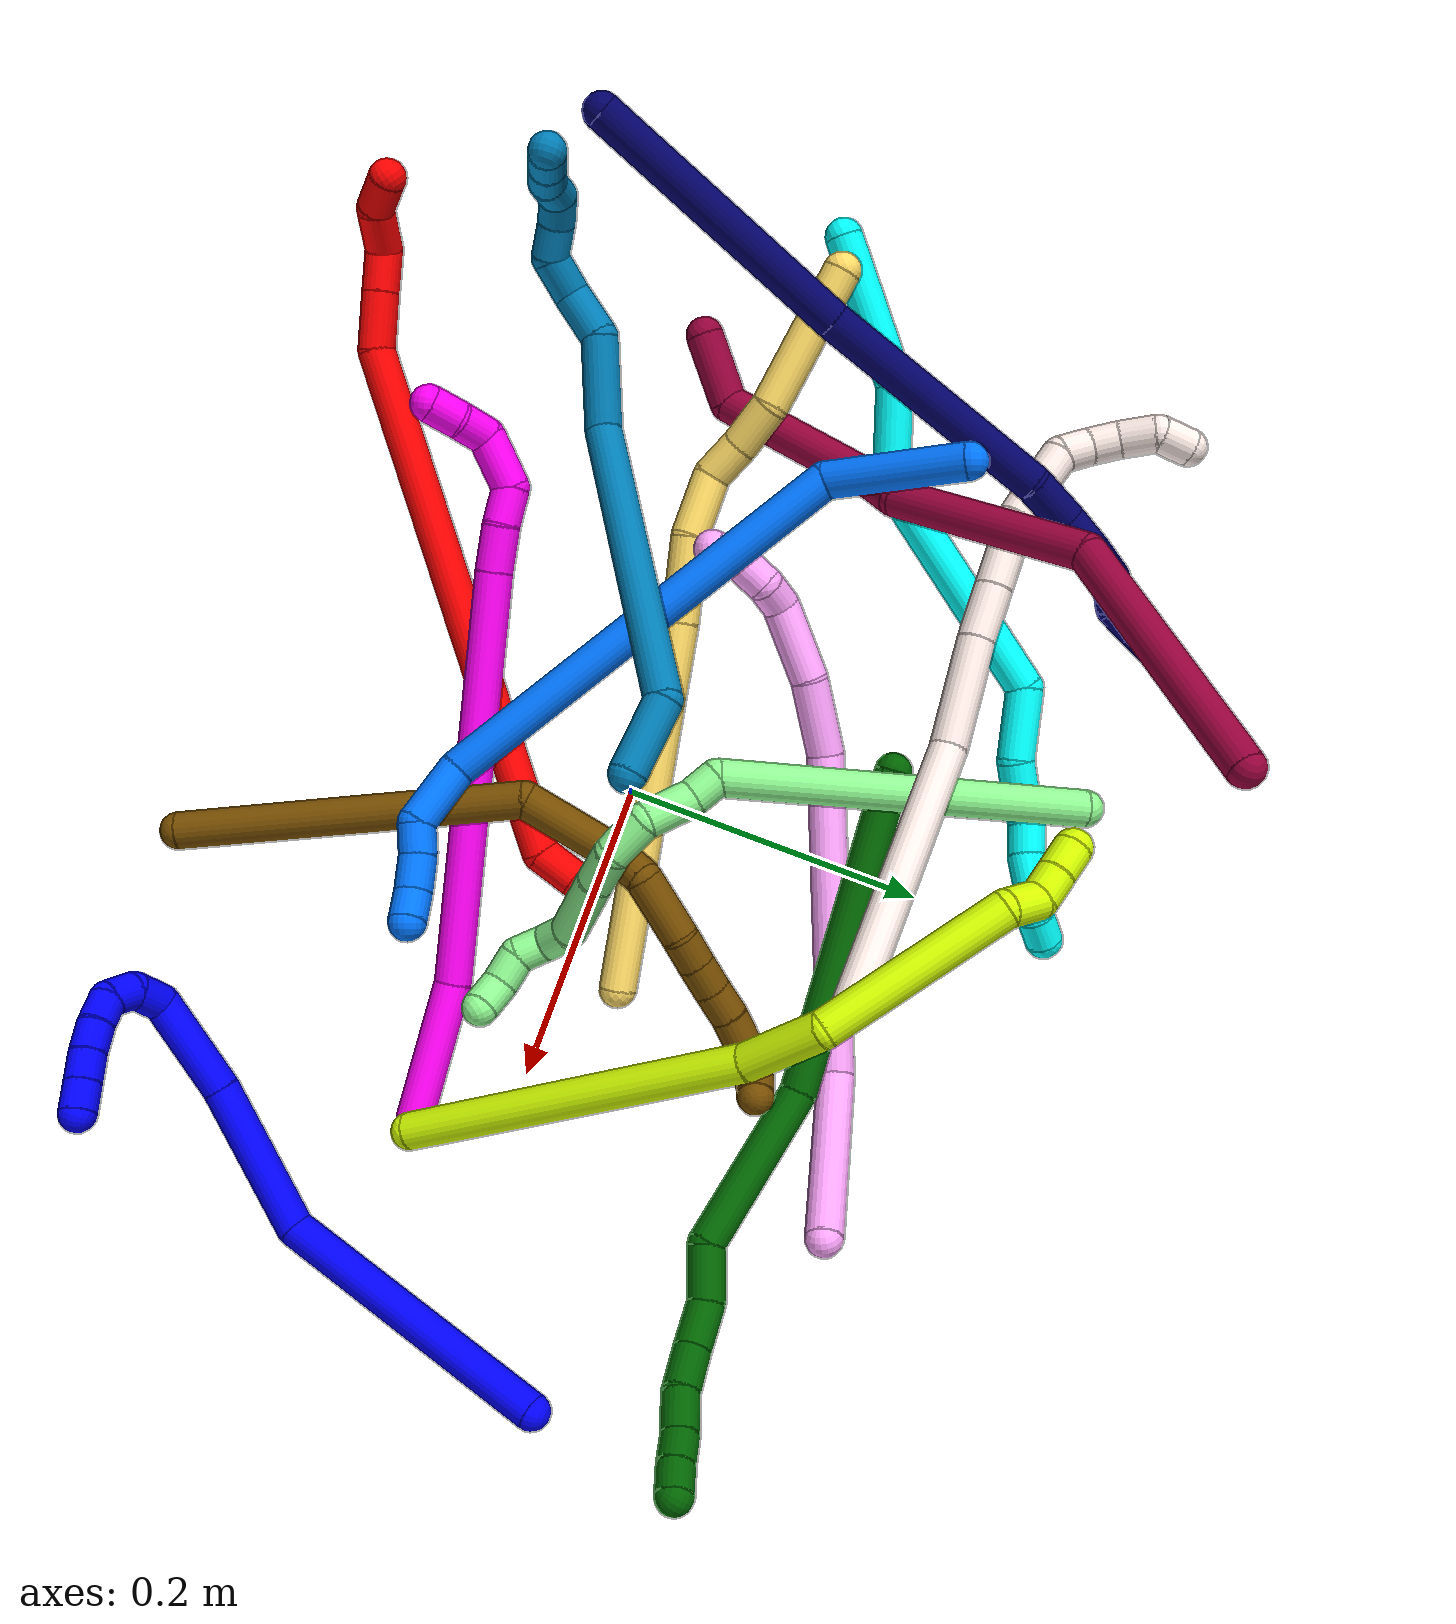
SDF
<sdf version="1.7">
 <world name="default">
  <plugin name="TubeGeneratorPlugin" filename="libtube_generator_plugin.so"/>
  <model name="photoneo_s_sensor">
   <static>1</static>
   <pose>0 0 2 1.57079 1.57079 3.14159</pose>
   <link name="link">
    <inertial><mass>0.1</mass></inertial>
    <sensor name="sensor" type="depth">
     <update_rate>30</update_rate>
     <camera>
      <horizontal_fov>1.22</horizontal_fov>
      <image><width>1920</width><height>1200</height><format>B8G8R8</format></image>
      <clip><near>0.1</near><far>4</far></clip>
      <depth_camera><output>points</output></depth_camera>
     </camera>
     <plugin name="camera_plugin" filename="libgazebo_ros_depth_camera.so">
      <baseline>0.2</baseline>
      <alwaysOn>1</alwaysOn>
      <updateRate>0.0</updateRate>
      <cameraName>camera_ir</cameraName>
      <imageTopicName>/camera/color/image_raw</imageTopicName>
      <cameraInfoTopicName>/camera/color/camera_info</cameraInfoTopicName>
      <depthImageTopicName>/camera/depth/image_raw</depthImageTopicName>
      <depthImageCameraInfoTopicName>/camera/depth/camera_info</depthImageCameraInfoTopicName>
      <pointCloudTopicName>/camera/depth/points</pointCloudTopicName>
      <frameName>fr_optical</frameName>
      <pointCloudCutoff>0.1</pointCloudCutoff>
      <pointCloudCutoffMax>2.0</pointCloudCutoffMax>
      <distortionK1>0</distortionK1>
      <distortionK2>0</distortionK2>
      <distortionK3>0</distortionK3>
      <distortionT1>0</distortionT1>
      <distortionT2>0</distortionT2>
      <CxPrime>0</CxPrime>
      <Cx>0</Cx>
      <Cy>0</Cy>
      <focalLength>0</focalLength>
      <hackBaseline>0</hackBaseline>
     </plugin>
    </sensor>
   </link>
  </model>
  <gravity>0 0 -9.8</gravity>
  <magnetic_field>6e-06 2.3e-05 -4.2e-05</magnetic_field>
  <atmosphere type="adiabatic"/>
  <physics name="default_physics" default="0" type="ode">
   <max_step_size>0.003</max_step_size>
   <real_time_factor>1</real_time_factor>
   <real_time_update_rate>1000</real_time_update_rate>
   <max_contacts>10000</max_contacts>
   <ode>
    <solver>
     <type>quick</type>
     <iters>100</iters>
     <sor>1.3</sor>
     <use_dynamic_moi_rescaling>0</use_dynamic_moi_rescaling>
    </solver>
    <constraints>
     <contact_max_correcting_vel>0</contact_max_correcting_vel>
     <contact_surface_layer>0.001</contact_surface_layer>
     <cfm>0</cfm>
     <erp>0.2</erp>
    </constraints>
   </ode>
  </physics>
  <scene><ambient>0.4 0.4 0.4 1</ambient><background>0.7 0.7 0.7 1</background><shadows>0</shadows></scene>
  <audio><device>default</device></audio>
  <spherical_coordinates>
   <surface_model>EARTH_WGS84</surface_model>
   <latitude_deg>0</latitude_deg>
   <longitude_deg>0</longitude_deg>
   <elevation>0</elevation>
   <heading_deg>0</heading_deg>
  </spherical_coordinates>
  <model name="bin">
   <static>1</static>
   <link name="bottom">
    <collision name="collision-bottom">
     <pose>0 0 -0.01 0 -0 0</pose>
     <geometry><box><size>0.8 0.6 0.02</size></box></geometry>
     <surface>
      <friction><ode><mu>100</mu><mu2>100</mu2></ode></friction>
      <contact><collide_bitmask>65535</collide_bitmask></contact>
     </surface>
    </collision>
   </link>
   <link name="west_wall">
    <collision name="collision-west_wall">
     <pose>-0.41 0 0.1 0 -0 0</pose>
     <geometry><box><size>0.02 0.6 0.2</size></box></geometry>
     <surface>
      <friction><ode><mu>100</mu><mu2>100</mu2></ode></friction>
      <contact><collide_bitmask>65535</collide_bitmask></contact>
     </surface>
    </collision>
   </link>
   <link name="east_wall">
    <collision name="collision-east_wall">
     <pose>0.41 0 0.1 0 -0 0</pose>
     <geometry><box><size>0.02 0.6 0.2</size></box></geometry>
     <surface>
      <friction><ode><mu>100</mu><mu2>100</mu2></ode></friction>
      <contact><collide_bitmask>65535</collide_bitmask></contact>
     </surface>
    </collision>
   </link>
   <link name="south_wall">
    <collision name="collision-south_wall">
     <pose>0 -0.31 0.1 0 -0 0</pose>
     <geometry><box><size>0.8 0.02 0.2</size></box></geometry>
     <surface>
      <friction><ode><mu>100</mu><mu2>100</mu2></ode></friction>
      <contact><collide_bitmask>65535</collide_bitmask></contact>
     </surface>
    </collision>
   </link>
   <link name="north_wall">
    <collision name="collision-north_wall">
     <pose>0 0.31 0.1 0 -0 0</pose>
     <geometry><box><size>0.8 0.02 0.2</size></box></geometry>
     <surface>
      <friction><ode><mu>100</mu><mu2>100</mu2></ode></friction>
      <contact><collide_bitmask>65535</collide_bitmask></contact>
     </surface>
    </collision>
   </link>
  </model>
  <model name="1">
   <static>0</static>
   <link name="1">
    <collision name="collision-cylinder-e_1_1_4">
     <pose>0.02632 -0.001243 0.097842 0.012704 0.262762 0.001679</pose>
     <geometry><cylinder><radius>0.0125</radius><length>0.202656</length></cylinder></geometry>
     <surface>
      <friction><ode><mu>1.16</mu><mu2>1.16</mu2><slip1>0</slip1><slip2>0</slip2></ode></friction>
      <contact><ode><kp>1e+06</kp><kd>1</kd><max_vel>0</max_vel><min_depth>0.001</min_depth></ode></contact>
     </surface>
    </collision>
    <visual name="visual-cylinder-e_1_1_4">
     <pose>0.02632 -0.001243 0.097842 0.012704 0.262762 0.001679</pose>
     <geometry><cylinder><radius>0.0125</radius><length>0.202656</length></cylinder></geometry>
     <material><ambient>0 0 1 1</ambient></material>
    </visual>
    <collision name="collision-cylinder-e_2_4_5">
     <pose>0.075457 -0.030783 0.233237 0.64576 0.451789 0.153486</pose>
     <geometry><cylinder><radius>0.0125</radius><length>0.104529</length></cylinder></geometry>
     <surface>
      <friction><ode><mu>1.16</mu><mu2>1.16</mu2><slip1>0</slip1><slip2>0</slip2></ode></friction>
      <contact><ode><kp>1e+06</kp><kd>1</kd><max_vel>0</max_vel><min_depth>0.001</min_depth></ode></contact>
     </surface>
    </collision>
    <visual name="visual-cylinder-e_2_4_5">
     <pose>0.075457 -0.030783 0.233237 0.64576 0.451789 0.153486</pose>
     <geometry><cylinder><radius>0.0125</radius><length>0.104529</length></cylinder></geometry>
     <material><ambient>0 0 1 1</ambient></material>
    </visual>
    <collision name="collision-cylinder-e_3_5_6">
     <pose>0.10944 -0.078076 0.297087 0.625548 0.331478 0.108083</pose>
     <geometry><cylinder><radius>0.0125</radius><length>0.068616</length></cylinder></geometry>
     <surface>
      <friction><ode><mu>1.16</mu><mu2>1.16</mu2><slip1>0</slip1><slip2>0</slip2></ode></friction>
      <contact><ode><kp>1e+06</kp><kd>1</kd><max_vel>0</max_vel><min_depth>0.001</min_depth></ode></contact>
     </surface>
    </collision>
    <visual name="visual-cylinder-e_3_5_6">
     <pose>0.10944 -0.078076 0.297087 0.625548 0.331478 0.108083</pose>
     <geometry><cylinder><radius>0.0125</radius><length>0.068616</length></cylinder></geometry>
     <material><ambient>0 0 1 1</ambient></material>
    </visual>
    <collision name="collision-cylinder-e_4_6_7">
     <pose>0.116403 -0.106094 0.329824 0.950914 -0.362294 -0.188038</pose>
     <geometry><cylinder><radius>0.0125</radius><length>0.023709</length></cylinder></geometry>
     <surface>
      <friction><ode><mu>1.16</mu><mu2>1.16</mu2><slip1>0</slip1><slip2>0</slip2></ode></friction>
      <contact><ode><kp>1e+06</kp><kd>1</kd><max_vel>0</max_vel><min_depth>0.001</min_depth></ode></contact>
     </surface>
    </collision>
    <visual name="visual-cylinder-e_4_6_7">
     <pose>0.116403 -0.106094 0.329824 0.950914 -0.362294 -0.188038</pose>
     <geometry><cylinder><radius>0.0125</radius><length>0.023709</length></cylinder></geometry>
     <material><ambient>0 0 1 1</ambient></material>
    </visual>
    <collision name="collision-cylinder-e_5_7_8">
     <pose>0.103779 -0.118727 0.34045 0.71173 -0.990024 -0.396048</pose>
     <geometry><cylinder><radius>0.0125</radius><length>0.020149</length></cylinder></geometry>
     <surface>
      <friction><ode><mu>1.16</mu><mu2>1.16</mu2><slip1>0</slip1><slip2>0</slip2></ode></friction>
      <contact><ode><kp>1e+06</kp><kd>1</kd><max_vel>0</max_vel><min_depth>0.001</min_depth></ode></contact>
     </surface>
    </collision>
    <visual name="visual-cylinder-e_5_7_8">
     <pose>0.103779 -0.118727 0.34045 0.71173 -0.990024 -0.396048</pose>
     <geometry><cylinder><radius>0.0125</radius><length>0.020149</length></cylinder></geometry>
     <material><ambient>0 0 1 1</ambient></material>
    </visual>
    <collision name="collision-cylinder-e_6_8_9">
     <pose>0.085358 -0.122084 0.34304 -2.98418 -1.41058 2.95684</pose>
     <geometry><cylinder><radius>0.0125</radius><length>0.020256</length></cylinder></geometry>
     <surface>
      <friction><ode><mu>1.16</mu><mu2>1.16</mu2><slip1>0</slip1><slip2>0</slip2></ode></friction>
      <contact><ode><kp>1e+06</kp><kd>1</kd><max_vel>0</max_vel><min_depth>0.001</min_depth></ode></contact>
     </surface>
    </collision>
    <visual name="visual-cylinder-e_6_8_9">
     <pose>0.085358 -0.122084 0.34304 -2.98418 -1.41058 2.95684</pose>
     <geometry><cylinder><radius>0.0125</radius><length>0.020256</length></cylinder></geometry>
     <material><ambient>0 0 1 1</ambient></material>
    </visual>
    <collision name="collision-cylinder-e_7_9_10">
     <pose>0.065816 -0.12032 0.338831 -2.61749 -1.26456 2.43968</pose>
     <geometry><cylinder><radius>0.0125</radius><length>0.020017</length></cylinder></geometry>
     <surface>
      <friction><ode><mu>1.16</mu><mu2>1.16</mu2><slip1>0</slip1><slip2>0</slip2></ode></friction>
      <contact><ode><kp>1e+06</kp><kd>1</kd><max_vel>0</max_vel><min_depth>0.001</min_depth></ode></contact>
     </surface>
    </collision>
    <visual name="visual-cylinder-e_7_9_10">
     <pose>0.065816 -0.12032 0.338831 -2.61749 -1.26456 2.43968</pose>
     <geometry><cylinder><radius>0.0125</radius><length>0.020017</length></cylinder></geometry>
     <material><ambient>0 0 1 1</ambient></material>
    </visual>
    <collision name="collision-cylinder-e_8_10_11">
     <pose>0.04708 -0.116732 0.332797 -2.59589 -1.16005 2.33432</pose>
     <geometry><cylinder><radius>0.0125</radius><length>0.020055</length></cylinder></geometry>
     <surface>
      <friction><ode><mu>1.16</mu><mu2>1.16</mu2><slip1>0</slip1><slip2>0</slip2></ode></friction>
      <contact><ode><kp>1e+06</kp><kd>1</kd><max_vel>0</max_vel><min_depth>0.001</min_depth></ode></contact>
     </surface>
    </collision>
    <visual name="visual-cylinder-e_8_10_11">
     <pose>0.04708 -0.116732 0.332797 -2.59589 -1.16005 2.33432</pose>
     <geometry><cylinder><radius>0.0125</radius><length>0.020055</length></cylinder></geometry>
     <material><ambient>0 0 1 1</ambient></material>
    </visual>
    <collision name="collision-cylinder-e_9_11_2">
     <pose>0.028726 -0.112475 0.325989 -2.56977 -1.1567 2.29537</pose>
     <geometry><cylinder><radius>0.0125</radius><length>0.020012</length></cylinder></geometry>
     <surface>
      <friction><ode><mu>1.16</mu><mu2>1.16</mu2><slip1>0</slip1><slip2>0</slip2></ode></friction>
      <contact><ode><kp>1e+06</kp><kd>1</kd><max_vel>0</max_vel><min_depth>0.001</min_depth></ode></contact>
     </surface>
    </collision>
    <visual name="visual-cylinder-e_9_11_2">
     <pose>0.028726 -0.112475 0.325989 -2.56977 -1.1567 2.29537</pose>
     <geometry><cylinder><radius>0.0125</radius><length>0.020012</length></cylinder></geometry>
     <material><ambient>0 0 1 1</ambient></material>
    </visual>
    <collision name="collision-sphere-2">
     <pose>0.019565 -0.110296 0.322603 0 -0 0</pose>
     <geometry><sphere><radius>0.0125</radius></sphere></geometry>
     <surface>
      <friction><ode><mu>1.16</mu><mu2>1.16</mu2><slip1>0</slip1><slip2>0</slip2></ode></friction>
      <contact><ode><kp>1e+06</kp><kd>1</kd><max_vel>0</max_vel><min_depth>0.001</min_depth></ode></contact>
     </surface>
    </collision>
    <visual name="visual-sphere-2">
     <pose>0.019565 -0.110296 0.322603 0 -0 0</pose>
     <geometry><sphere><radius>0.0125</radius></sphere></geometry>
     <material><ambient>0 0 1 1</ambient></material>
    </visual>
    <collision name="collision-sphere-11">
     <pose>0.037886 -0.114654 0.329374 0 -0 0</pose>
     <geometry><sphere><radius>0.0125</radius></sphere></geometry>
     <surface>
      <friction><ode><mu>1.16</mu><mu2>1.16</mu2><slip1>0</slip1><slip2>0</slip2></ode></friction>
      <contact><ode><kp>1e+06</kp><kd>1</kd><max_vel>0</max_vel><min_depth>0.001</min_depth></ode></contact>
     </surface>
    </collision>
    <visual name="visual-sphere-11">
     <pose>0.037886 -0.114654 0.329374 0 -0 0</pose>
     <geometry><sphere><radius>0.0125</radius></sphere></geometry>
     <material><ambient>0 0 1 1</ambient></material>
    </visual>
    <collision name="collision-sphere-10">
     <pose>0.056273 -0.11881 0.336219 0 -0 0</pose>
     <geometry><sphere><radius>0.0125</radius></sphere></geometry>
     <surface>
      <friction><ode><mu>1.16</mu><mu2>1.16</mu2><slip1>0</slip1><slip2>0</slip2></ode></friction>
      <contact><ode><kp>1e+06</kp><kd>1</kd><max_vel>0</max_vel><min_depth>0.001</min_depth></ode></contact>
     </surface>
    </collision>
    <visual name="visual-sphere-10">
     <pose>0.056273 -0.11881 0.336219 0 -0 0</pose>
     <geometry><sphere><radius>0.0125</radius></sphere></geometry>
     <material><ambient>0 0 1 1</ambient></material>
    </visual>
    <collision name="collision-sphere-9">
     <pose>0.075359 -0.12183 0.341444 0 -0 0</pose>
     <geometry><sphere><radius>0.0125</radius></sphere></geometry>
     <surface>
      <friction><ode><mu>1.16</mu><mu2>1.16</mu2><slip1>0</slip1><slip2>0</slip2></ode></friction>
      <contact><ode><kp>1e+06</kp><kd>1</kd><max_vel>0</max_vel><min_depth>0.001</min_depth></ode></contact>
     </surface>
    </collision>
    <visual name="visual-sphere-9">
     <pose>0.075359 -0.12183 0.341444 0 -0 0</pose>
     <geometry><sphere><radius>0.0125</radius></sphere></geometry>
     <material><ambient>0 0 1 1</ambient></material>
    </visual>
    <collision name="collision-sphere-4">
     <pose>0.05264 -0.002486 0.195684 0 -0 0</pose>
     <geometry><sphere><radius>0.0125</radius></sphere></geometry>
     <surface>
      <friction><ode><mu>1.16</mu><mu2>1.16</mu2><slip1>0</slip1><slip2>0</slip2></ode></friction>
      <contact><ode><kp>1e+06</kp><kd>1</kd><max_vel>0</max_vel><min_depth>0.001</min_depth></ode></contact>
     </surface>
    </collision>
    <visual name="visual-sphere-4">
     <pose>0.05264 -0.002486 0.195684 0 -0 0</pose>
     <geometry><sphere><radius>0.0125</radius></sphere></geometry>
     <material><ambient>0 0 1 1</ambient></material>
    </visual>
    <collision name="collision-sphere-1">
     <geometry><sphere><radius>0.0125</radius></sphere></geometry>
     <surface>
      <friction><ode><mu>1.16</mu><mu2>1.16</mu2><slip1>0</slip1><slip2>0</slip2></ode></friction>
      <contact><ode><kp>1e+06</kp><kd>1</kd><max_vel>0</max_vel><min_depth>0.001</min_depth></ode></contact>
     </surface>
    </collision>
    <visual name="visual-sphere-1">
     <geometry><sphere><radius>0.0125</radius></sphere></geometry>
     <material><ambient>0 0 1 1</ambient></material>
    </visual>
    <collision name="collision-sphere-8">
     <pose>0.095356 -0.122337 0.344635 0 -0 0</pose>
     <geometry><sphere><radius>0.0125</radius></sphere></geometry>
     <surface>
      <friction><ode><mu>1.16</mu><mu2>1.16</mu2><slip1>0</slip1><slip2>0</slip2></ode></friction>
      <contact><ode><kp>1e+06</kp><kd>1</kd><max_vel>0</max_vel><min_depth>0.001</min_depth></ode></contact>
     </surface>
    </collision>
    <visual name="visual-sphere-8">
     <pose>0.095356 -0.122337 0.344635 0 -0 0</pose>
     <geometry><sphere><radius>0.0125</radius></sphere></geometry>
     <material><ambient>0 0 1 1</ambient></material>
    </visual>
    <collision name="collision-sphere-5">
     <pose>0.098274 -0.059081 0.270789 0 -0 0</pose>
     <geometry><sphere><radius>0.0125</radius></sphere></geometry>
     <surface>
      <friction><ode><mu>1.16</mu><mu2>1.16</mu2><slip1>0</slip1><slip2>0</slip2></ode></friction>
      <contact><ode><kp>1e+06</kp><kd>1</kd><max_vel>0</max_vel><min_depth>0.001</min_depth></ode></contact>
     </surface>
    </collision>
    <visual name="visual-sphere-5">
     <pose>0.098274 -0.059081 0.270789 0 -0 0</pose>
     <geometry><sphere><radius>0.0125</radius></sphere></geometry>
     <material><ambient>0 0 1 1</ambient></material>
    </visual>
    <collision name="collision-sphere-6">
     <pose>0.120605 -0.097071 0.323384 0 -0 0</pose>
     <geometry><sphere><radius>0.0125</radius></sphere></geometry>
     <surface>
      <friction><ode><mu>1.16</mu><mu2>1.16</mu2><slip1>0</slip1><slip2>0</slip2></ode></friction>
      <contact><ode><kp>1e+06</kp><kd>1</kd><max_vel>0</max_vel><min_depth>0.001</min_depth></ode></contact>
     </surface>
    </collision>
    <visual name="visual-sphere-6">
     <pose>0.120605 -0.097071 0.323384 0 -0 0</pose>
     <geometry><sphere><radius>0.0125</radius></sphere></geometry>
     <material><ambient>0 0 1 1</ambient></material>
    </visual>
    <collision name="collision-sphere-7">
     <pose>0.112202 -0.115116 0.336264 0 -0 0</pose>
     <geometry><sphere><radius>0.0125</radius></sphere></geometry>
     <surface>
      <friction><ode><mu>1.16</mu><mu2>1.16</mu2><slip1>0</slip1><slip2>0</slip2></ode></friction>
      <contact><ode><kp>1e+06</kp><kd>1</kd><max_vel>0</max_vel><min_depth>0.001</min_depth></ode></contact>
     </surface>
    </collision>
    <visual name="visual-sphere-7">
     <pose>0.112202 -0.115116 0.336264 0 -0 0</pose>
     <geometry><sphere><radius>0.0125</radius></sphere></geometry>
     <material><ambient>0 0 1 1</ambient></material>
    </visual>
    <inertial>
     <pose>0.060294 -0.046416 0.212404 0 -0 0</pose>
     <mass>0.5</mass>
     <inertia>
      <ixx>0.000815</ixx>
      <ixy>0</ixy>
      <ixz>0</ixz>
      <iyy>0.000826</iyy>
      <iyz>0</iyz>
      <izz>-0.000123</izz>
     </inertia>
    </inertial>
   </link>
   <pose>0.387569 0.078339 0.082628 -1.8395 0.634901 2.99693</pose>
  </model>
  <model name="2">
   <static>0</static>
   <link name="2">
    <collision name="collision-cylinder-e_1_1_4">
     <pose>0.003187 -0.005518 0.012371 0.419567 0.231085 0.049412</pose>
     <geometry><cylinder><radius>0.0125</radius><length>0.027832</length></cylinder></geometry>
     <surface>
      <friction><ode><mu>1.16</mu><mu2>1.16</mu2><slip1>0</slip1><slip2>0</slip2></ode></friction>
      <contact><ode><kp>1e+06</kp><kd>1</kd><max_vel>0</max_vel><min_depth>0.001</min_depth></ode></contact>
     </surface>
    </collision>
    <visual name="visual-cylinder-e_1_1_4">
     <pose>0.003187 -0.005518 0.012371 0.419567 0.231085 0.049412</pose>
     <geometry><cylinder><radius>0.0125</radius><length>0.027832</length></cylinder></geometry>
     <material><ambient>1 0 0 1</ambient></material>
    </visual>
    <collision name="collision-cylinder-e_2_4_5">
     <pose>-0.052837 -0.045194 0.185352 0.209551 -0.346088 -0.036758</pose>
     <geometry><cylinder><radius>0.0125</radius><length>0.349103</length></cylinder></geometry>
     <surface>
      <friction><ode><mu>1.16</mu><mu2>1.16</mu2><slip1>0</slip1><slip2>0</slip2></ode></friction>
      <contact><ode><kp>1e+06</kp><kd>1</kd><max_vel>0</max_vel><min_depth>0.001</min_depth></ode></contact>
     </surface>
    </collision>
    <visual name="visual-cylinder-e_2_4_5">
     <pose>-0.052837 -0.045194 0.185352 0.209551 -0.346088 -0.036758</pose>
     <geometry><cylinder><radius>0.0125</radius><length>0.349103</length></cylinder></geometry>
     <material><ambient>1 0 0 1</ambient></material>
    </visual>
    <collision name="collision-cylinder-e_3_5_6">
     <pose>-0.124274 -0.079063 0.360555 -0.019701 -0.697224 0.007161</pose>
     <geometry><cylinder><radius>0.0125</radius><length>0.03808</length></cylinder></geometry>
     <surface>
      <friction><ode><mu>1.16</mu><mu2>1.16</mu2><slip1>0</slip1><slip2>0</slip2></ode></friction>
      <contact><ode><kp>1e+06</kp><kd>1</kd><max_vel>0</max_vel><min_depth>0.001</min_depth></ode></contact>
     </surface>
    </collision>
    <visual name="visual-cylinder-e_3_5_6">
     <pose>-0.124274 -0.079063 0.360555 -0.019701 -0.697224 0.007161</pose>
     <geometry><cylinder><radius>0.0125</radius><length>0.03808</length></cylinder></geometry>
     <material><ambient>1 0 0 1</ambient></material>
    </visual>
    <collision name="collision-cylinder-e_4_6_7">
     <pose>-0.145666 -0.078719 0.385687 -0.005376 -0.715922 0.002011</pose>
     <geometry><cylinder><radius>0.0125</radius><length>0.027936</length></cylinder></geometry>
     <surface>
      <friction><ode><mu>1.16</mu><mu2>1.16</mu2><slip1>0</slip1><slip2>0</slip2></ode></friction>
      <contact><ode><kp>1e+06</kp><kd>1</kd><max_vel>0</max_vel><min_depth>0.001</min_depth></ode></contact>
     </surface>
    </collision>
    <visual name="visual-cylinder-e_4_6_7">
     <pose>-0.145666 -0.078719 0.385687 -0.005376 -0.715922 0.002011</pose>
     <geometry><cylinder><radius>0.0125</radius><length>0.027936</length></cylinder></geometry>
     <material><ambient>1 0 0 1</ambient></material>
    </visual>
    <collision name="collision-cylinder-e_5_7_8">
     <pose>-0.157589 -0.069385 0.408809 -0.635322 -0.17445 0.057489</pose>
     <geometry><cylinder><radius>0.0125</radius><length>0.03175</length></cylinder></geometry>
     <surface>
      <friction><ode><mu>1.16</mu><mu2>1.16</mu2><slip1>0</slip1><slip2>0</slip2></ode></friction>
      <contact><ode><kp>1e+06</kp><kd>1</kd><max_vel>0</max_vel><min_depth>0.001</min_depth></ode></contact>
     </surface>
    </collision>
    <visual name="visual-cylinder-e_5_7_8">
     <pose>-0.157589 -0.069385 0.408809 -0.635322 -0.17445 0.057489</pose>
     <geometry><cylinder><radius>0.0125</radius><length>0.03175</length></cylinder></geometry>
     <material><ambient>1 0 0 1</ambient></material>
    </visual>
    <collision name="collision-cylinder-e_6_8_2">
     <pose>-0.166575 -0.050784 0.427248 -1.01003 -0.515039 0.289164</pose>
     <geometry><cylinder><radius>0.0125</radius><length>0.0253</length></cylinder></geometry>
     <surface>
      <friction><ode><mu>1.16</mu><mu2>1.16</mu2><slip1>0</slip1><slip2>0</slip2></ode></friction>
      <contact><ode><kp>1e+06</kp><kd>1</kd><max_vel>0</max_vel><min_depth>0.001</min_depth></ode></contact>
     </surface>
    </collision>
    <visual name="visual-cylinder-e_6_8_2">
     <pose>-0.166575 -0.050784 0.427248 -1.01003 -0.515039 0.289164</pose>
     <geometry><cylinder><radius>0.0125</radius><length>0.0253</length></cylinder></geometry>
     <material><ambient>1 0 0 1</ambient></material>
    </visual>
    <collision name="collision-sphere-2">
     <pose>-0.172806 -0.041461 0.433103 0 -0 0</pose>
     <geometry><sphere><radius>0.0125</radius></sphere></geometry>
     <surface>
      <friction><ode><mu>1.16</mu><mu2>1.16</mu2><slip1>0</slip1><slip2>0</slip2></ode></friction>
      <contact><ode><kp>1e+06</kp><kd>1</kd><max_vel>0</max_vel><min_depth>0.001</min_depth></ode></contact>
     </surface>
    </collision>
    <visual name="visual-sphere-2">
     <pose>-0.172806 -0.041461 0.433103 0 -0 0</pose>
     <geometry><sphere><radius>0.0125</radius></sphere></geometry>
     <material><ambient>1 0 0 1</ambient></material>
    </visual>
    <collision name="collision-sphere-4">
     <pose>0.006374 -0.011036 0.024742 0 -0 0</pose>
     <geometry><sphere><radius>0.0125</radius></sphere></geometry>
     <surface>
      <friction><ode><mu>1.16</mu><mu2>1.16</mu2><slip1>0</slip1><slip2>0</slip2></ode></friction>
      <contact><ode><kp>1e+06</kp><kd>1</kd><max_vel>0</max_vel><min_depth>0.001</min_depth></ode></contact>
     </surface>
    </collision>
    <visual name="visual-sphere-4">
     <pose>0.006374 -0.011036 0.024742 0 -0 0</pose>
     <geometry><sphere><radius>0.0125</radius></sphere></geometry>
     <material><ambient>1 0 0 1</ambient></material>
    </visual>
    <collision name="collision-sphere-1">
     <geometry><sphere><radius>0.0125</radius></sphere></geometry>
     <surface>
      <friction><ode><mu>1.16</mu><mu2>1.16</mu2><slip1>0</slip1><slip2>0</slip2></ode></friction>
      <contact><ode><kp>1e+06</kp><kd>1</kd><max_vel>0</max_vel><min_depth>0.001</min_depth></ode></contact>
     </surface>
    </collision>
    <visual name="visual-sphere-1">
     <geometry><sphere><radius>0.0125</radius></sphere></geometry>
     <material><ambient>1 0 0 1</ambient></material>
    </visual>
    <collision name="collision-sphere-8">
     <pose>-0.160344 -0.060107 0.421393 0 -0 0</pose>
     <geometry><sphere><radius>0.0125</radius></sphere></geometry>
     <surface>
      <friction><ode><mu>1.16</mu><mu2>1.16</mu2><slip1>0</slip1><slip2>0</slip2></ode></friction>
      <contact><ode><kp>1e+06</kp><kd>1</kd><max_vel>0</max_vel><min_depth>0.001</min_depth></ode></contact>
     </surface>
    </collision>
    <visual name="visual-sphere-8">
     <pose>-0.160344 -0.060107 0.421393 0 -0 0</pose>
     <geometry><sphere><radius>0.0125</radius></sphere></geometry>
     <material><ambient>1 0 0 1</ambient></material>
    </visual>
    <collision name="collision-sphere-5">
     <pose>-0.112048 -0.079351 0.345961 0 -0 0</pose>
     <geometry><sphere><radius>0.0125</radius></sphere></geometry>
     <surface>
      <friction><ode><mu>1.16</mu><mu2>1.16</mu2><slip1>0</slip1><slip2>0</slip2></ode></friction>
      <contact><ode><kp>1e+06</kp><kd>1</kd><max_vel>0</max_vel><min_depth>0.001</min_depth></ode></contact>
     </surface>
    </collision>
    <visual name="visual-sphere-5">
     <pose>-0.112048 -0.079351 0.345961 0 -0 0</pose>
     <geometry><sphere><radius>0.0125</radius></sphere></geometry>
     <material><ambient>1 0 0 1</ambient></material>
    </visual>
    <collision name="collision-sphere-6">
     <pose>-0.136499 -0.078776 0.375149 0 -0 0</pose>
     <geometry><sphere><radius>0.0125</radius></sphere></geometry>
     <surface>
      <friction><ode><mu>1.16</mu><mu2>1.16</mu2><slip1>0</slip1><slip2>0</slip2></ode></friction>
      <contact><ode><kp>1e+06</kp><kd>1</kd><max_vel>0</max_vel><min_depth>0.001</min_depth></ode></contact>
     </surface>
    </collision>
    <visual name="visual-sphere-6">
     <pose>-0.136499 -0.078776 0.375149 0 -0 0</pose>
     <geometry><sphere><radius>0.0125</radius></sphere></geometry>
     <material><ambient>1 0 0 1</ambient></material>
    </visual>
    <collision name="collision-sphere-7">
     <pose>-0.154834 -0.078663 0.396226 0 -0 0</pose>
     <geometry><sphere><radius>0.0125</radius></sphere></geometry>
     <surface>
      <friction><ode><mu>1.16</mu><mu2>1.16</mu2><slip1>0</slip1><slip2>0</slip2></ode></friction>
      <contact><ode><kp>1e+06</kp><kd>1</kd><max_vel>0</max_vel><min_depth>0.001</min_depth></ode></contact>
     </surface>
    </collision>
    <visual name="visual-sphere-7">
     <pose>-0.154834 -0.078663 0.396226 0 -0 0</pose>
     <geometry><sphere><radius>0.0125</radius></sphere></geometry>
     <material><ambient>1 0 0 1</ambient></material>
    </visual>
    <inertial>
     <pose>-0.072753 -0.049257 0.226689 0 -0 0</pose>
     <mass>0.5</mass>
     <inertia>
      <ixx>0.003226</ixx>
      <ixy>0</ixy>
      <ixz>0</ixz>
      <iyy>0.003379</iyy>
      <iyz>0</iyz>
      <izz>0.001942</izz>
     </inertia>
    </inertial>
   </link>
   <pose>0.067008 -0.015448 0.013324 1.27621 -0.231324 -0.541096</pose>
  </model>
  <model name="3">
   <static>0</static>
   <link name="3">
    <collision name="collision-cylinder-e_1_1_4">
     <pose>0.042333 0.025758 -0.011848 -2.00193 0.980668 -1.38924</pose>
     <geometry><cylinder><radius>0.0125</radius><length>0.101901</length></cylinder></geometry>
     <surface>
      <friction><ode><mu>1.16</mu><mu2>1.16</mu2><slip1>0</slip1><slip2>0</slip2></ode></friction>
      <contact><ode><kp>1e+06</kp><kd>1</kd><max_vel>0</max_vel><min_depth>0.001</min_depth></ode></contact>
     </surface>
    </collision>
    <visual name="visual-cylinder-e_1_1_4">
     <pose>0.042333 0.025758 -0.011848 -2.00193 0.980668 -1.38924</pose>
     <geometry><cylinder><radius>0.0125</radius><length>0.101901</length></cylinder></geometry>
     <material><ambient>0.003922 1 0.996078 1</ambient></material>
    </visual>
    <collision name="collision-cylinder-e_2_4_5">
     <pose>0.107834 0.063638 -0.041607 -2.54659 0.819769 -1.91258</pose>
     <geometry><cylinder><radius>0.0125</radius><length>0.063387</length></cylinder></geometry>
     <surface>
      <friction><ode><mu>1.16</mu><mu2>1.16</mu2><slip1>0</slip1><slip2>0</slip2></ode></friction>
      <contact><ode><kp>1e+06</kp><kd>1</kd><max_vel>0</max_vel><min_depth>0.001</min_depth></ode></contact>
     </surface>
    </collision>
    <visual name="visual-cylinder-e_2_4_5">
     <pose>0.107834 0.063638 -0.041607 -2.54659 0.819769 -1.91258</pose>
     <geometry><cylinder><radius>0.0125</radius><length>0.063387</length></cylinder></geometry>
     <material><ambient>0.003922 1 0.996078 1</ambient></material>
    </visual>
    <collision name="collision-cylinder-e_3_5_6">
     <pose>0.198473 0.120155 -0.058838 -1.5555 0.988785 -0.976056</pose>
     <geometry><cylinder><radius>0.0125</radius><length>0.16154</length></cylinder></geometry>
     <surface>
      <friction><ode><mu>1.16</mu><mu2>1.16</mu2><slip1>0</slip1><slip2>0</slip2></ode></friction>
      <contact><ode><kp>1e+06</kp><kd>1</kd><max_vel>0</max_vel><min_depth>0.001</min_depth></ode></contact>
     </surface>
    </collision>
    <visual name="visual-cylinder-e_3_5_6">
     <pose>0.198473 0.120155 -0.058838 -1.5555 0.988785 -0.976056</pose>
     <geometry><cylinder><radius>0.0125</radius><length>0.16154</length></cylinder></geometry>
     <material><ambient>0.003922 1 0.996078 1</ambient></material>
    </visual>
    <collision name="collision-cylinder-e_4_6_7">
     <pose>0.28475 0.169671 -0.072346 -2.79515 0.894785 -2.44226</pose>
     <geometry><cylinder><radius>0.0125</radius><length>0.048213</length></cylinder></geometry>
     <surface>
      <friction><ode><mu>1.16</mu><mu2>1.16</mu2><slip1>0</slip1><slip2>0</slip2></ode></friction>
      <contact><ode><kp>1e+06</kp><kd>1</kd><max_vel>0</max_vel><min_depth>0.001</min_depth></ode></contact>
     </surface>
    </collision>
    <visual name="visual-cylinder-e_4_6_7">
     <pose>0.28475 0.169671 -0.072346 -2.79515 0.894785 -2.44226</pose>
     <geometry><cylinder><radius>0.0125</radius><length>0.048213</length></cylinder></geometry>
     <material><ambient>0.003922 1 0.996078 1</ambient></material>
    </visual>
    <collision name="collision-cylinder-e_5_7_8">
     <pose>0.311958 0.180943 -0.091447 -2.24481 0.818007 -1.46674</pose>
     <geometry><cylinder><radius>0.0125</radius><length>0.02303</length></cylinder></geometry>
     <surface>
      <friction><ode><mu>1.16</mu><mu2>1.16</mu2><slip1>0</slip1><slip2>0</slip2></ode></friction>
      <contact><ode><kp>1e+06</kp><kd>1</kd><max_vel>0</max_vel><min_depth>0.001</min_depth></ode></contact>
     </surface>
    </collision>
    <visual name="visual-cylinder-e_5_7_8">
     <pose>0.311958 0.180943 -0.091447 -2.24481 0.818007 -1.46674</pose>
     <geometry><cylinder><radius>0.0125</radius><length>0.02303</length></cylinder></geometry>
     <material><ambient>0.003922 1 0.996078 1</ambient></material>
    </visual>
    <collision name="collision-cylinder-e_6_8_9">
     <pose>0.329828 0.189669 -0.099156 -2.39747 1.18903 -2.09466</pose>
     <geometry><cylinder><radius>0.0125</radius><length>0.020401</length></cylinder></geometry>
     <surface>
      <friction><ode><mu>1.16</mu><mu2>1.16</mu2><slip1>0</slip1><slip2>0</slip2></ode></friction>
      <contact><ode><kp>1e+06</kp><kd>1</kd><max_vel>0</max_vel><min_depth>0.001</min_depth></ode></contact>
     </surface>
    </collision>
    <visual name="visual-cylinder-e_6_8_9">
     <pose>0.329828 0.189669 -0.099156 -2.39747 1.18903 -2.09466</pose>
     <geometry><cylinder><radius>0.0125</radius><length>0.020401</length></cylinder></geometry>
     <material><ambient>0.003922 1 0.996078 1</ambient></material>
    </visual>
    <collision name="collision-cylinder-e_7_9_10">
     <pose>0.348067 0.194165 -0.106887 -2.77015 1.02763 -2.49886</pose>
     <geometry><cylinder><radius>0.0125</radius><length>0.020496</length></cylinder></geometry>
     <surface>
      <friction><ode><mu>1.16</mu><mu2>1.16</mu2><slip1>0</slip1><slip2>0</slip2></ode></friction>
      <contact><ode><kp>1e+06</kp><kd>1</kd><max_vel>0</max_vel><min_depth>0.001</min_depth></ode></contact>
     </surface>
    </collision>
    <visual name="visual-cylinder-e_7_9_10">
     <pose>0.348067 0.194165 -0.106887 -2.77015 1.02763 -2.49886</pose>
     <geometry><cylinder><radius>0.0125</radius><length>0.020496</length></cylinder></geometry>
     <material><ambient>0.003922 1 0.996078 1</ambient></material>
    </visual>
    <collision name="collision-cylinder-e_8_10_11">
     <pose>0.36657 0.197355 -0.114208 -2.65295 1.3 -2.50781</pose>
     <geometry><cylinder><radius>0.0125</radius><length>0.020196</length></cylinder></geometry>
     <surface>
      <friction><ode><mu>1.16</mu><mu2>1.16</mu2><slip1>0</slip1><slip2>0</slip2></ode></friction>
      <contact><ode><kp>1e+06</kp><kd>1</kd><max_vel>0</max_vel><min_depth>0.001</min_depth></ode></contact>
     </surface>
    </collision>
    <visual name="visual-cylinder-e_8_10_11">
     <pose>0.36657 0.197355 -0.114208 -2.65295 1.3 -2.50781</pose>
     <geometry><cylinder><radius>0.0125</radius><length>0.020196</length></cylinder></geometry>
     <material><ambient>0.003922 1 0.996078 1</ambient></material>
    </visual>
    <collision name="collision-cylinder-e_9_11_12">
     <pose>0.384651 0.202723 -0.121052 -2.39816 0.943234 -1.83631</pose>
     <geometry><cylinder><radius>0.0125</radius><length>0.020632</length></cylinder></geometry>
     <surface>
      <friction><ode><mu>1.16</mu><mu2>1.16</mu2><slip1>0</slip1><slip2>0</slip2></ode></friction>
      <contact><ode><kp>1e+06</kp><kd>1</kd><max_vel>0</max_vel><min_depth>0.001</min_depth></ode></contact>
     </surface>
    </collision>
    <visual name="visual-cylinder-e_9_11_12">
     <pose>0.384651 0.202723 -0.121052 -2.39816 0.943234 -1.83631</pose>
     <geometry><cylinder><radius>0.0125</radius><length>0.020632</length></cylinder></geometry>
     <material><ambient>0.003922 1 0.996078 1</ambient></material>
    </visual>
    <collision name="collision-cylinder-e_10_12_2">
     <pose>0.398204 0.214875 -0.128696 -1.94745 0.541083 -0.774674</pose>
     <geometry><cylinder><radius>0.0125</radius><length>0.020204</length></cylinder></geometry>
     <surface>
      <friction><ode><mu>1.16</mu><mu2>1.16</mu2><slip1>0</slip1><slip2>0</slip2></ode></friction>
      <contact><ode><kp>1e+06</kp><kd>1</kd><max_vel>0</max_vel><min_depth>0.001</min_depth></ode></contact>
     </surface>
    </collision>
    <visual name="visual-cylinder-e_10_12_2">
     <pose>0.398204 0.214875 -0.128696 -1.94745 0.541083 -0.774674</pose>
     <geometry><cylinder><radius>0.0125</radius><length>0.020204</length></cylinder></geometry>
     <material><ambient>0.003922 1 0.996078 1</ambient></material>
    </visual>
    <collision name="collision-sphere-2">
     <pose>0.403408 0.222927 -0.131881 0 -0 0</pose>
     <geometry><sphere><radius>0.0125</radius></sphere></geometry>
     <surface>
      <friction><ode><mu>1.16</mu><mu2>1.16</mu2><slip1>0</slip1><slip2>0</slip2></ode></friction>
      <contact><ode><kp>1e+06</kp><kd>1</kd><max_vel>0</max_vel><min_depth>0.001</min_depth></ode></contact>
     </surface>
    </collision>
    <visual name="visual-sphere-2">
     <pose>0.403408 0.222927 -0.131881 0 -0 0</pose>
     <geometry><sphere><radius>0.0125</radius></sphere></geometry>
     <material><ambient>0.003922 1 0.996078 1</ambient></material>
    </visual>
    <collision name="collision-sphere-12">
     <pose>0.393001 0.206823 -0.125511 0 -0 0</pose>
     <geometry><sphere><radius>0.0125</radius></sphere></geometry>
     <surface>
      <friction><ode><mu>1.16</mu><mu2>1.16</mu2><slip1>0</slip1><slip2>0</slip2></ode></friction>
      <contact><ode><kp>1e+06</kp><kd>1</kd><max_vel>0</max_vel><min_depth>0.001</min_depth></ode></contact>
     </surface>
    </collision>
    <visual name="visual-sphere-12">
     <pose>0.393001 0.206823 -0.125511 0 -0 0</pose>
     <geometry><sphere><radius>0.0125</radius></sphere></geometry>
     <material><ambient>0.003922 1 0.996078 1</ambient></material>
    </visual>
    <collision name="collision-sphere-11">
     <pose>0.3763 0.198624 -0.116593 0 -0 0</pose>
     <geometry><sphere><radius>0.0125</radius></sphere></geometry>
     <surface>
      <friction><ode><mu>1.16</mu><mu2>1.16</mu2><slip1>0</slip1><slip2>0</slip2></ode></friction>
      <contact><ode><kp>1e+06</kp><kd>1</kd><max_vel>0</max_vel><min_depth>0.001</min_depth></ode></contact>
     </surface>
    </collision>
    <visual name="visual-sphere-11">
     <pose>0.3763 0.198624 -0.116593 0 -0 0</pose>
     <geometry><sphere><radius>0.0125</radius></sphere></geometry>
     <material><ambient>0.003922 1 0.996078 1</ambient></material>
    </visual>
    <collision name="collision-sphere-10">
     <pose>0.35684 0.196087 -0.111823 0 -0 0</pose>
     <geometry><sphere><radius>0.0125</radius></sphere></geometry>
     <surface>
      <friction><ode><mu>1.16</mu><mu2>1.16</mu2><slip1>0</slip1><slip2>0</slip2></ode></friction>
      <contact><ode><kp>1e+06</kp><kd>1</kd><max_vel>0</max_vel><min_depth>0.001</min_depth></ode></contact>
     </surface>
    </collision>
    <visual name="visual-sphere-10">
     <pose>0.35684 0.196087 -0.111823 0 -0 0</pose>
     <geometry><sphere><radius>0.0125</radius></sphere></geometry>
     <material><ambient>0.003922 1 0.996078 1</ambient></material>
    </visual>
    <collision name="collision-sphere-9">
     <pose>0.339295 0.192243 -0.101952 0 -0 0</pose>
     <geometry><sphere><radius>0.0125</radius></sphere></geometry>
     <surface>
      <friction><ode><mu>1.16</mu><mu2>1.16</mu2><slip1>0</slip1><slip2>0</slip2></ode></friction>
      <contact><ode><kp>1e+06</kp><kd>1</kd><max_vel>0</max_vel><min_depth>0.001</min_depth></ode></contact>
     </surface>
    </collision>
    <visual name="visual-sphere-9">
     <pose>0.339295 0.192243 -0.101952 0 -0 0</pose>
     <geometry><sphere><radius>0.0125</radius></sphere></geometry>
     <material><ambient>0.003922 1 0.996078 1</ambient></material>
    </visual>
    <collision name="collision-sphere-4">
     <pose>0.084666 0.051516 -0.023697 0 -0 0</pose>
     <geometry><sphere><radius>0.0125</radius></sphere></geometry>
     <surface>
      <friction><ode><mu>1.16</mu><mu2>1.16</mu2><slip1>0</slip1><slip2>0</slip2></ode></friction>
      <contact><ode><kp>1e+06</kp><kd>1</kd><max_vel>0</max_vel><min_depth>0.001</min_depth></ode></contact>
     </surface>
    </collision>
    <visual name="visual-sphere-4">
     <pose>0.084666 0.051516 -0.023697 0 -0 0</pose>
     <geometry><sphere><radius>0.0125</radius></sphere></geometry>
     <material><ambient>0.003922 1 0.996078 1</ambient></material>
    </visual>
    <collision name="collision-sphere-1">
     <geometry><sphere><radius>0.0125</radius></sphere></geometry>
     <surface>
      <friction><ode><mu>1.16</mu><mu2>1.16</mu2><slip1>0</slip1><slip2>0</slip2></ode></friction>
      <contact><ode><kp>1e+06</kp><kd>1</kd><max_vel>0</max_vel><min_depth>0.001</min_depth></ode></contact>
     </surface>
    </collision>
    <visual name="visual-sphere-1">
     <geometry><sphere><radius>0.0125</radius></sphere></geometry>
     <material><ambient>0.003922 1 0.996078 1</ambient></material>
    </visual>
    <collision name="collision-sphere-8">
     <pose>0.320362 0.187094 -0.09636 0 -0 0</pose>
     <geometry><sphere><radius>0.0125</radius></sphere></geometry>
     <surface>
      <friction><ode><mu>1.16</mu><mu2>1.16</mu2><slip1>0</slip1><slip2>0</slip2></ode></friction>
      <contact><ode><kp>1e+06</kp><kd>1</kd><max_vel>0</max_vel><min_depth>0.001</min_depth></ode></contact>
     </surface>
    </collision>
    <visual name="visual-sphere-8">
     <pose>0.320362 0.187094 -0.09636 0 -0 0</pose>
     <geometry><sphere><radius>0.0125</radius></sphere></geometry>
     <material><ambient>0.003922 1 0.996078 1</ambient></material>
    </visual>
    <collision name="collision-sphere-5">
     <pose>0.131001 0.07576 -0.059518 0 -0 0</pose>
     <geometry><sphere><radius>0.0125</radius></sphere></geometry>
     <surface>
      <friction><ode><mu>1.16</mu><mu2>1.16</mu2><slip1>0</slip1><slip2>0</slip2></ode></friction>
      <contact><ode><kp>1e+06</kp><kd>1</kd><max_vel>0</max_vel><min_depth>0.001</min_depth></ode></contact>
     </surface>
    </collision>
    <visual name="visual-sphere-5">
     <pose>0.131001 0.07576 -0.059518 0 -0 0</pose>
     <geometry><sphere><radius>0.0125</radius></sphere></geometry>
     <material><ambient>0.003922 1 0.996078 1</ambient></material>
    </visual>
    <collision name="collision-sphere-6">
     <pose>0.265945 0.164549 -0.058159 0 -0 0</pose>
     <geometry><sphere><radius>0.0125</radius></sphere></geometry>
     <surface>
      <friction><ode><mu>1.16</mu><mu2>1.16</mu2><slip1>0</slip1><slip2>0</slip2></ode></friction>
      <contact><ode><kp>1e+06</kp><kd>1</kd><max_vel>0</max_vel><min_depth>0.001</min_depth></ode></contact>
     </surface>
    </collision>
    <visual name="visual-sphere-6">
     <pose>0.265945 0.164549 -0.058159 0 -0 0</pose>
     <geometry><sphere><radius>0.0125</radius></sphere></geometry>
     <material><ambient>0.003922 1 0.996078 1</ambient></material>
    </visual>
    <collision name="collision-sphere-7">
     <pose>0.303555 0.174792 -0.086533 0 -0 0</pose>
     <geometry><sphere><radius>0.0125</radius></sphere></geometry>
     <surface>
      <friction><ode><mu>1.16</mu><mu2>1.16</mu2><slip1>0</slip1><slip2>0</slip2></ode></friction>
      <contact><ode><kp>1e+06</kp><kd>1</kd><max_vel>0</max_vel><min_depth>0.001</min_depth></ode></contact>
     </surface>
    </collision>
    <visual name="visual-sphere-7">
     <pose>0.303555 0.174792 -0.086533 0 -0 0</pose>
     <geometry><sphere><radius>0.0125</radius></sphere></geometry>
     <material><ambient>0.003922 1 0.996078 1</ambient></material>
    </visual>
    <inertial>
     <pose>0.202742 0.117549 -0.061123 0 -0 0</pose>
     <mass>0.5</mass>
     <inertia>
      <ixx>-9.8e-05</ixx>
      <ixy>0</ixy>
      <ixz>0</ixz>
      <iyy>0.000124</iyy>
      <iyz>0</iyz>
      <izz>-0.000677</izz>
     </inertia>
    </inertial>
   </link>
   <pose>-0.388512 0.002714 0.027466 -1.09396 -0.540575 0.670016</pose>
  </model>
  <model name="4">
   <static>0</static>
   <link name="4">
    <collision name="collision-cylinder-e_1_1_4">
     <pose>0.00105 -0.056448 -0.022982 1.95744 0.017222 0.025606</pose>
     <geometry><cylinder><radius>0.0125</radius><length>0.121912</length></cylinder></geometry>
     <surface>
      <friction><ode><mu>1.16</mu><mu2>1.16</mu2><slip1>0</slip1><slip2>0</slip2></ode></friction>
      <contact><ode><kp>1e+06</kp><kd>1</kd><max_vel>0</max_vel><min_depth>0.001</min_depth></ode></contact>
     </surface>
    </collision>
    <visual name="visual-cylinder-e_1_1_4">
     <pose>0.00105 -0.056448 -0.022982 1.95744 0.017222 0.025606</pose>
     <geometry><cylinder><radius>0.0125</radius><length>0.121912</length></cylinder></geometry>
     <material><ambient>1 0.65098 0.996078 1</ambient></material>
    </visual>
    <collision name="collision-cylinder-e_2_4_5">
     <pose>0.008107 -0.159903 -0.141013 2.68231 0.056593 0.240986</pose>
     <geometry><cylinder><radius>0.0125</radius><length>0.212416</length></cylinder></geometry>
     <surface>
      <friction><ode><mu>1.16</mu><mu2>1.16</mu2><slip1>0</slip1><slip2>0</slip2></ode></friction>
      <contact><ode><kp>1e+06</kp><kd>1</kd><max_vel>0</max_vel><min_depth>0.001</min_depth></ode></contact>
     </surface>
    </collision>
    <visual name="visual-cylinder-e_2_4_5">
     <pose>0.008107 -0.159903 -0.141013 2.68231 0.056593 0.240986</pose>
     <geometry><cylinder><radius>0.0125</radius><length>0.212416</length></cylinder></geometry>
     <material><ambient>1 0.65098 0.996078 1</ambient></material>
    </visual>
    <collision name="collision-cylinder-e_3_5_6">
     <pose>0.012183 -0.211211 -0.261368 2.97326 -0.075107 -0.837935</pose>
     <geometry><cylinder><radius>0.0125</radius><length>0.051482</length></cylinder></geometry>
     <surface>
      <friction><ode><mu>1.16</mu><mu2>1.16</mu2><slip1>0</slip1><slip2>0</slip2></ode></friction>
      <contact><ode><kp>1e+06</kp><kd>1</kd><max_vel>0</max_vel><min_depth>0.001</min_depth></ode></contact>
     </surface>
    </collision>
    <visual name="visual-cylinder-e_3_5_6">
     <pose>0.012183 -0.211211 -0.261368 2.97326 -0.075107 -0.837935</pose>
     <geometry><cylinder><radius>0.0125</radius><length>0.051482</length></cylinder></geometry>
     <material><ambient>1 0.65098 0.996078 1</ambient></material>
    </visual>
    <collision name="collision-cylinder-e_4_6_7">
     <pose>0.003752 -0.222615 -0.310847 2.85577 -0.252455 -1.44548</pose>
     <geometry><cylinder><radius>0.0125</radius><length>0.052041</length></cylinder></geometry>
     <surface>
      <friction><ode><mu>1.16</mu><mu2>1.16</mu2><slip1>0</slip1><slip2>0</slip2></ode></friction>
      <contact><ode><kp>1e+06</kp><kd>1</kd><max_vel>0</max_vel><min_depth>0.001</min_depth></ode></contact>
     </surface>
    </collision>
    <visual name="visual-cylinder-e_4_6_7">
     <pose>0.003752 -0.222615 -0.310847 2.85577 -0.252455 -1.44548</pose>
     <geometry><cylinder><radius>0.0125</radius><length>0.052041</length></cylinder></geometry>
     <material><ambient>1 0.65098 0.996078 1</ambient></material>
    </visual>
    <collision name="collision-cylinder-e_5_7_8">
     <pose>-0.005951 -0.226192 -0.344075 -2.77013 -0.31849 1.4145</pose>
     <geometry><cylinder><radius>0.0125</radius><length>0.020463</length></cylinder></geometry>
     <surface>
      <friction><ode><mu>1.16</mu><mu2>1.16</mu2><slip1>0</slip1><slip2>0</slip2></ode></friction>
      <contact><ode><kp>1e+06</kp><kd>1</kd><max_vel>0</max_vel><min_depth>0.001</min_depth></ode></contact>
     </surface>
    </collision>
    <visual name="visual-cylinder-e_5_7_8">
     <pose>-0.005951 -0.226192 -0.344075 -2.77013 -0.31849 1.4145</pose>
     <geometry><cylinder><radius>0.0125</radius><length>0.020463</length></cylinder></geometry>
     <material><ambient>1 0.65098 0.996078 1</ambient></material>
    </visual>
    <collision name="collision-cylinder-e_6_8_9">
     <pose>-0.015984 -0.22381 -0.361226 3.00102 -0.695777 -2.75809</pose>
     <geometry><cylinder><radius>0.0125</radius><length>0.021307</length></cylinder></geometry>
     <surface>
      <friction><ode><mu>1.16</mu><mu2>1.16</mu2><slip1>0</slip1><slip2>0</slip2></ode></friction>
      <contact><ode><kp>1e+06</kp><kd>1</kd><max_vel>0</max_vel><min_depth>0.001</min_depth></ode></contact>
     </surface>
    </collision>
    <visual name="visual-cylinder-e_6_8_9">
     <pose>-0.015984 -0.22381 -0.361226 3.00102 -0.695777 -2.75809</pose>
     <geometry><cylinder><radius>0.0125</radius><length>0.021307</length></cylinder></geometry>
     <material><ambient>1 0.65098 0.996078 1</ambient></material>
    </visual>
    <collision name="collision-cylinder-e_7_9_2">
     <pose>-0.030814 -0.223884 -0.375539 -2.97089 -0.903178 2.79237</pose>
     <geometry><cylinder><radius>0.0125</radius><length>0.020379</length></cylinder></geometry>
     <surface>
      <friction><ode><mu>1.16</mu><mu2>1.16</mu2><slip1>0</slip1><slip2>0</slip2></ode></friction>
      <contact><ode><kp>1e+06</kp><kd>1</kd><max_vel>0</max_vel><min_depth>0.001</min_depth></ode></contact>
     </surface>
    </collision>
    <visual name="visual-cylinder-e_7_9_2">
     <pose>-0.030814 -0.223884 -0.375539 -2.97089 -0.903178 2.79237</pose>
     <geometry><cylinder><radius>0.0125</radius><length>0.020379</length></cylinder></geometry>
     <material><ambient>1 0.65098 0.996078 1</ambient></material>
    </visual>
    <collision name="collision-sphere-2">
     <pose>-0.038816 -0.222813 -0.381756 0 -0 0</pose>
     <geometry><sphere><radius>0.0125</radius></sphere></geometry>
     <surface>
      <friction><ode><mu>1.16</mu><mu2>1.16</mu2><slip1>0</slip1><slip2>0</slip2></ode></friction>
      <contact><ode><kp>1e+06</kp><kd>1</kd><max_vel>0</max_vel><min_depth>0.001</min_depth></ode></contact>
     </surface>
    </collision>
    <visual name="visual-sphere-2">
     <pose>-0.038816 -0.222813 -0.381756 0 -0 0</pose>
     <geometry><sphere><radius>0.0125</radius></sphere></geometry>
     <material><ambient>1 0.65098 0.996078 1</ambient></material>
    </visual>
    <collision name="collision-sphere-9">
     <pose>-0.022812 -0.224956 -0.369322 0 -0 0</pose>
     <geometry><sphere><radius>0.0125</radius></sphere></geometry>
     <surface>
      <friction><ode><mu>1.16</mu><mu2>1.16</mu2><slip1>0</slip1><slip2>0</slip2></ode></friction>
      <contact><ode><kp>1e+06</kp><kd>1</kd><max_vel>0</max_vel><min_depth>0.001</min_depth></ode></contact>
     </surface>
    </collision>
    <visual name="visual-sphere-9">
     <pose>-0.022812 -0.224956 -0.369322 0 -0 0</pose>
     <geometry><sphere><radius>0.0125</radius></sphere></geometry>
     <material><ambient>1 0.65098 0.996078 1</ambient></material>
    </visual>
    <collision name="collision-sphere-4">
     <pose>0.0021 -0.112896 -0.045964 0 -0 0</pose>
     <geometry><sphere><radius>0.0125</radius></sphere></geometry>
     <surface>
      <friction><ode><mu>1.16</mu><mu2>1.16</mu2><slip1>0</slip1><slip2>0</slip2></ode></friction>
      <contact><ode><kp>1e+06</kp><kd>1</kd><max_vel>0</max_vel><min_depth>0.001</min_depth></ode></contact>
     </surface>
    </collision>
    <visual name="visual-sphere-4">
     <pose>0.0021 -0.112896 -0.045964 0 -0 0</pose>
     <geometry><sphere><radius>0.0125</radius></sphere></geometry>
     <material><ambient>1 0.65098 0.996078 1</ambient></material>
    </visual>
    <collision name="collision-sphere-1">
     <geometry><sphere><radius>0.0125</radius></sphere></geometry>
     <surface>
      <friction><ode><mu>1.16</mu><mu2>1.16</mu2><slip1>0</slip1><slip2>0</slip2></ode></friction>
      <contact><ode><kp>1e+06</kp><kd>1</kd><max_vel>0</max_vel><min_depth>0.001</min_depth></ode></contact>
     </surface>
    </collision>
    <visual name="visual-sphere-1">
     <geometry><sphere><radius>0.0125</radius></sphere></geometry>
     <material><ambient>1 0.65098 0.996078 1</ambient></material>
    </visual>
    <collision name="collision-sphere-8">
     <pose>-0.009155 -0.222665 -0.353129 0 -0 0</pose>
     <geometry><sphere><radius>0.0125</radius></sphere></geometry>
     <surface>
      <friction><ode><mu>1.16</mu><mu2>1.16</mu2><slip1>0</slip1><slip2>0</slip2></ode></friction>
      <contact><ode><kp>1e+06</kp><kd>1</kd><max_vel>0</max_vel><min_depth>0.001</min_depth></ode></contact>
     </surface>
    </collision>
    <visual name="visual-sphere-8">
     <pose>-0.009155 -0.222665 -0.353129 0 -0 0</pose>
     <geometry><sphere><radius>0.0125</radius></sphere></geometry>
     <material><ambient>1 0.65098 0.996078 1</ambient></material>
    </visual>
    <collision name="collision-sphere-5">
     <pose>0.014114 -0.20691 -0.236062 0 -0 0</pose>
     <geometry><sphere><radius>0.0125</radius></sphere></geometry>
     <surface>
      <friction><ode><mu>1.16</mu><mu2>1.16</mu2><slip1>0</slip1><slip2>0</slip2></ode></friction>
      <contact><ode><kp>1e+06</kp><kd>1</kd><max_vel>0</max_vel><min_depth>0.001</min_depth></ode></contact>
     </surface>
    </collision>
    <visual name="visual-sphere-5">
     <pose>0.014114 -0.20691 -0.236062 0 -0 0</pose>
     <geometry><sphere><radius>0.0125</radius></sphere></geometry>
     <material><ambient>1 0.65098 0.996078 1</ambient></material>
    </visual>
    <collision name="collision-sphere-6">
     <pose>0.010251 -0.215511 -0.286674 0 -0 0</pose>
     <geometry><sphere><radius>0.0125</radius></sphere></geometry>
     <surface>
      <friction><ode><mu>1.16</mu><mu2>1.16</mu2><slip1>0</slip1><slip2>0</slip2></ode></friction>
      <contact><ode><kp>1e+06</kp><kd>1</kd><max_vel>0</max_vel><min_depth>0.001</min_depth></ode></contact>
     </surface>
    </collision>
    <visual name="visual-sphere-6">
     <pose>0.010251 -0.215511 -0.286674 0 -0 0</pose>
     <geometry><sphere><radius>0.0125</radius></sphere></geometry>
     <material><ambient>1 0.65098 0.996078 1</ambient></material>
    </visual>
    <collision name="collision-sphere-7">
     <pose>-0.002748 -0.229719 -0.335021 0 -0 0</pose>
     <geometry><sphere><radius>0.0125</radius></sphere></geometry>
     <surface>
      <friction><ode><mu>1.16</mu><mu2>1.16</mu2><slip1>0</slip1><slip2>0</slip2></ode></friction>
      <contact><ode><kp>1e+06</kp><kd>1</kd><max_vel>0</max_vel><min_depth>0.001</min_depth></ode></contact>
     </surface>
    </collision>
    <visual name="visual-sphere-7">
     <pose>-0.002748 -0.229719 -0.335021 0 -0 0</pose>
     <geometry><sphere><radius>0.0125</radius></sphere></geometry>
     <material><ambient>1 0.65098 0.996078 1</ambient></material>
    </visual>
    <inertial>
     <pose>0.003164 -0.154532 -0.169557 0 -0 0</pose>
     <mass>0.5</mass>
     <inertia>
      <ixx>0.001118</ixx>
      <ixy>0</ixy>
      <ixz>0</ixz>
      <iyy>-0.000606</iyy>
      <iyz>0</iyz>
      <izz>0.000436</izz>
     </inertia>
    </inertial>
   </link>
   <pose>0.219476 0.211693 0.089743 2.02727 -0.240385 2.01735</pose>
  </model>
  <model name="5">
   <static>0</static>
   <link name="5">
    <collision name="collision-cylinder-e_1_1_4">
     <pose>-0.097866 -0.015475 -0.071579 2.92867 -0.928383 -2.72102</pose>
     <geometry><cylinder><radius>0.0125</radius><length>0.244465</length></cylinder></geometry>
     <surface>
      <friction><ode><mu>1.16</mu><mu2>1.16</mu2><slip1>0</slip1><slip2>0</slip2></ode></friction>
      <contact><ode><kp>1e+06</kp><kd>1</kd><max_vel>0</max_vel><min_depth>0.001</min_depth></ode></contact>
     </surface>
    </collision>
    <visual name="visual-cylinder-e_1_1_4">
     <pose>-0.097866 -0.015475 -0.071579 2.92867 -0.928383 -2.72102</pose>
     <geometry><cylinder><radius>0.0125</radius><length>0.244465</length></cylinder></geometry>
     <material><ambient>1 0.858824 0.4 1</ambient></material>
    </visual>
    <collision name="collision-cylinder-e_2_4_5">
     <pose>-0.219232 -0.033285 -0.158934 2.99472 -0.974598 -2.86571</pose>
     <geometry><cylinder><radius>0.0125</radius><length>0.056803</length></cylinder></geometry>
     <surface>
      <friction><ode><mu>1.16</mu><mu2>1.16</mu2><slip1>0</slip1><slip2>0</slip2></ode></friction>
      <contact><ode><kp>1e+06</kp><kd>1</kd><max_vel>0</max_vel><min_depth>0.001</min_depth></ode></contact>
     </surface>
    </collision>
    <visual name="visual-cylinder-e_2_4_5">
     <pose>-0.219232 -0.033285 -0.158934 2.99472 -0.974598 -2.86571</pose>
     <geometry><cylinder><radius>0.0125</radius><length>0.056803</length></cylinder></geometry>
     <material><ambient>1 0.858824 0.4 1</ambient></material>
    </visual>
    <collision name="collision-cylinder-e_3_5_6">
     <pose>-0.257382 -0.041712 -0.18845 2.72419 -0.77252 -2.18137</pose>
     <geometry><cylinder><radius>0.0125</radius><length>0.041976</length></cylinder></geometry>
     <surface>
      <friction><ode><mu>1.16</mu><mu2>1.16</mu2><slip1>0</slip1><slip2>0</slip2></ode></friction>
      <contact><ode><kp>1e+06</kp><kd>1</kd><max_vel>0</max_vel><min_depth>0.001</min_depth></ode></contact>
     </surface>
    </collision>
    <visual name="visual-cylinder-e_3_5_6">
     <pose>-0.257382 -0.041712 -0.18845 2.72419 -0.77252 -2.18137</pose>
     <geometry><cylinder><radius>0.0125</radius><length>0.041976</length></cylinder></geometry>
     <material><ambient>1 0.858824 0.4 1</ambient></material>
    </visual>
    <collision name="collision-cylinder-e_4_6_7">
     <pose>-0.275966 -0.049418 -0.215084 3.01715 -0.29409 -2.34525</pose>
     <geometry><cylinder><radius>0.0125</radius><length>0.027157</length></cylinder></geometry>
     <surface>
      <friction><ode><mu>1.16</mu><mu2>1.16</mu2><slip1>0</slip1><slip2>0</slip2></ode></friction>
      <contact><ode><kp>1e+06</kp><kd>1</kd><max_vel>0</max_vel><min_depth>0.001</min_depth></ode></contact>
     </surface>
    </collision>
    <visual name="visual-cylinder-e_4_6_7">
     <pose>-0.275966 -0.049418 -0.215084 3.01715 -0.29409 -2.34525</pose>
     <geometry><cylinder><radius>0.0125</radius><length>0.027157</length></cylinder></geometry>
     <material><ambient>1 0.858824 0.4 1</ambient></material>
    </visual>
    <collision name="collision-cylinder-e_5_7_8">
     <pose>-0.285618 -0.051029 -0.243476 -3.14146 -0.353365 3.14084</pose>
     <geometry><cylinder><radius>0.0125</radius><length>0.033035</length></cylinder></geometry>
     <surface>
      <friction><ode><mu>1.16</mu><mu2>1.16</mu2><slip1>0</slip1><slip2>0</slip2></ode></friction>
      <contact><ode><kp>1e+06</kp><kd>1</kd><max_vel>0</max_vel><min_depth>0.001</min_depth></ode></contact>
     </surface>
    </collision>
    <visual name="visual-cylinder-e_5_7_8">
     <pose>-0.285618 -0.051029 -0.243476 -3.14146 -0.353365 3.14084</pose>
     <geometry><cylinder><radius>0.0125</radius><length>0.033035</length></cylinder></geometry>
     <material><ambient>1 0.858824 0.4 1</ambient></material>
    </visual>
    <collision name="collision-cylinder-e_6_8_2">
     <pose>-0.318741 -0.061438 -0.297336 2.87658 -0.603626 -2.33255</pose>
     <geometry><cylinder><radius>0.0125</radius><length>0.096566</length></cylinder></geometry>
     <surface>
      <friction><ode><mu>1.16</mu><mu2>1.16</mu2><slip1>0</slip1><slip2>0</slip2></ode></friction>
      <contact><ode><kp>1e+06</kp><kd>1</kd><max_vel>0</max_vel><min_depth>0.001</min_depth></ode></contact>
     </surface>
    </collision>
    <visual name="visual-cylinder-e_6_8_2">
     <pose>-0.318741 -0.061438 -0.297336 2.87658 -0.603626 -2.33255</pose>
     <geometry><cylinder><radius>0.0125</radius><length>0.096566</length></cylinder></geometry>
     <material><ambient>1 0.858824 0.4 1</ambient></material>
    </visual>
    <collision name="collision-sphere-2">
     <pose>-0.346148 -0.07185 -0.335699 0 -0 0</pose>
     <geometry><sphere><radius>0.0125</radius></sphere></geometry>
     <surface>
      <friction><ode><mu>1.16</mu><mu2>1.16</mu2><slip1>0</slip1><slip2>0</slip2></ode></friction>
      <contact><ode><kp>1e+06</kp><kd>1</kd><max_vel>0</max_vel><min_depth>0.001</min_depth></ode></contact>
     </surface>
    </collision>
    <visual name="visual-sphere-2">
     <pose>-0.346148 -0.07185 -0.335699 0 -0 0</pose>
     <geometry><sphere><radius>0.0125</radius></sphere></geometry>
     <material><ambient>1 0.858824 0.4 1</ambient></material>
    </visual>
    <collision name="collision-sphere-4">
     <pose>-0.195731 -0.030951 -0.143158 0 -0 0</pose>
     <geometry><sphere><radius>0.0125</radius></sphere></geometry>
     <surface>
      <friction><ode><mu>1.16</mu><mu2>1.16</mu2><slip1>0</slip1><slip2>0</slip2></ode></friction>
      <contact><ode><kp>1e+06</kp><kd>1</kd><max_vel>0</max_vel><min_depth>0.001</min_depth></ode></contact>
     </surface>
    </collision>
    <visual name="visual-sphere-4">
     <pose>-0.195731 -0.030951 -0.143158 0 -0 0</pose>
     <geometry><sphere><radius>0.0125</radius></sphere></geometry>
     <material><ambient>1 0.858824 0.4 1</ambient></material>
    </visual>
    <collision name="collision-sphere-1">
     <geometry><sphere><radius>0.0125</radius></sphere></geometry>
     <surface>
      <friction><ode><mu>1.16</mu><mu2>1.16</mu2><slip1>0</slip1><slip2>0</slip2></ode></friction>
      <contact><ode><kp>1e+06</kp><kd>1</kd><max_vel>0</max_vel><min_depth>0.001</min_depth></ode></contact>
     </surface>
    </collision>
    <visual name="visual-sphere-1">
     <geometry><sphere><radius>0.0125</radius></sphere></geometry>
     <material><ambient>1 0.858824 0.4 1</ambient></material>
    </visual>
    <collision name="collision-sphere-8">
     <pose>-0.291334 -0.051027 -0.258973 0 -0 0</pose>
     <geometry><sphere><radius>0.0125</radius></sphere></geometry>
     <surface>
      <friction><ode><mu>1.16</mu><mu2>1.16</mu2><slip1>0</slip1><slip2>0</slip2></ode></friction>
      <contact><ode><kp>1e+06</kp><kd>1</kd><max_vel>0</max_vel><min_depth>0.001</min_depth></ode></contact>
     </surface>
    </collision>
    <visual name="visual-sphere-8">
     <pose>-0.291334 -0.051027 -0.258973 0 -0 0</pose>
     <geometry><sphere><radius>0.0125</radius></sphere></geometry>
     <material><ambient>1 0.858824 0.4 1</ambient></material>
    </visual>
    <collision name="collision-sphere-5">
     <pose>-0.242734 -0.035618 -0.17471 0 -0 0</pose>
     <geometry><sphere><radius>0.0125</radius></sphere></geometry>
     <surface>
      <friction><ode><mu>1.16</mu><mu2>1.16</mu2><slip1>0</slip1><slip2>0</slip2></ode></friction>
      <contact><ode><kp>1e+06</kp><kd>1</kd><max_vel>0</max_vel><min_depth>0.001</min_depth></ode></contact>
     </surface>
    </collision>
    <visual name="visual-sphere-5">
     <pose>-0.242734 -0.035618 -0.17471 0 -0 0</pose>
     <geometry><sphere><radius>0.0125</radius></sphere></geometry>
     <material><ambient>1 0.858824 0.4 1</ambient></material>
    </visual>
    <collision name="collision-sphere-6">
     <pose>-0.27203 -0.047805 -0.20219 0 -0 0</pose>
     <geometry><sphere><radius>0.0125</radius></sphere></geometry>
     <surface>
      <friction><ode><mu>1.16</mu><mu2>1.16</mu2><slip1>0</slip1><slip2>0</slip2></ode></friction>
      <contact><ode><kp>1e+06</kp><kd>1</kd><max_vel>0</max_vel><min_depth>0.001</min_depth></ode></contact>
     </surface>
    </collision>
    <visual name="visual-sphere-6">
     <pose>-0.27203 -0.047805 -0.20219 0 -0 0</pose>
     <geometry><sphere><radius>0.0125</radius></sphere></geometry>
     <material><ambient>1 0.858824 0.4 1</ambient></material>
    </visual>
    <collision name="collision-sphere-7">
     <pose>-0.279902 -0.051031 -0.227979 0 -0 0</pose>
     <geometry><sphere><radius>0.0125</radius></sphere></geometry>
     <surface>
      <friction><ode><mu>1.16</mu><mu2>1.16</mu2><slip1>0</slip1><slip2>0</slip2></ode></friction>
      <contact><ode><kp>1e+06</kp><kd>1</kd><max_vel>0</max_vel><min_depth>0.001</min_depth></ode></contact>
     </surface>
    </collision>
    <visual name="visual-sphere-7">
     <pose>-0.279902 -0.051031 -0.227979 0 -0 0</pose>
     <geometry><sphere><radius>0.0125</radius></sphere></geometry>
     <material><ambient>1 0.858824 0.4 1</ambient></material>
    </visual>
    <inertial>
     <pose>-0.189781 -0.032771 -0.154067 0 -0 0</pose>
     <mass>0.5</mass>
     <inertia>
      <ixx>-0.001118</ixx>
      <ixy>0</ixy>
      <ixz>0</ixz>
      <iyy>0.000908</iyy>
      <iyz>0</iyz>
      <izz>0.0012</izz>
     </inertia>
    </inertial>
   </link>
   <pose>0.125078 0.036876 0.012423 2.04957 -0.119639 0.80749</pose>
  </model>
  <model name="6">
   <static>0</static>
   <link name="6">
    <collision name="collision-cylinder-e_1_1_4">
     <pose>0.105768 0.010625 0.023665 -0.421993 1.33028 -0.332894</pose>
     <geometry><cylinder><radius>0.0125</radius><length>0.217805</length></cylinder></geometry>
     <surface>
      <friction><ode><mu>1.16</mu><mu2>1.16</mu2><slip1>0</slip1><slip2>0</slip2></ode></friction>
      <contact><ode><kp>1e+06</kp><kd>1</kd><max_vel>0</max_vel><min_depth>0.001</min_depth></ode></contact>
     </surface>
    </collision>
    <visual name="visual-cylinder-e_1_1_4">
     <pose>0.105768 0.010625 0.023665 -0.421993 1.33028 -0.332894</pose>
     <geometry><cylinder><radius>0.0125</radius><length>0.217805</length></cylinder></geometry>
     <material><ambient>0 0.392157 0.003922 1</ambient></material>
    </visual>
    <collision name="collision-cylinder-e_2_4_5">
     <pose>0.268173 0.018616 0.039592 2.81357 1.42748 2.76396</pose>
     <geometry><cylinder><radius>0.0125</radius><length>0.114448</length></cylinder></geometry>
     <surface>
      <friction><ode><mu>1.16</mu><mu2>1.16</mu2><slip1>0</slip1><slip2>0</slip2></ode></friction>
      <contact><ode><kp>1e+06</kp><kd>1</kd><max_vel>0</max_vel><min_depth>0.001</min_depth></ode></contact>
     </surface>
    </collision>
    <visual name="visual-cylinder-e_2_4_5">
     <pose>0.268173 0.018616 0.039592 2.81357 1.42748 2.76396</pose>
     <geometry><cylinder><radius>0.0125</radius><length>0.114448</length></cylinder></geometry>
     <material><ambient>0 0.392157 0.003922 1</ambient></material>
    </visual>
    <collision name="collision-cylinder-e_3_5_6">
     <pose>0.341027 0.013223 0.039268 0.356381 1.11696 0.224123</pose>
     <geometry><cylinder><radius>0.0125</radius><length>0.036086</length></cylinder></geometry>
     <surface>
      <friction><ode><mu>1.16</mu><mu2>1.16</mu2><slip1>0</slip1><slip2>0</slip2></ode></friction>
      <contact><ode><kp>1e+06</kp><kd>1</kd><max_vel>0</max_vel><min_depth>0.001</min_depth></ode></contact>
     </surface>
    </collision>
    <visual name="visual-cylinder-e_3_5_6">
     <pose>0.341027 0.013223 0.039268 0.356381 1.11696 0.224123</pose>
     <geometry><cylinder><radius>0.0125</radius><length>0.036086</length></cylinder></geometry>
     <material><ambient>0 0.392157 0.003922 1</ambient></material>
    </visual>
    <collision name="collision-cylinder-e_4_6_7">
     <pose>0.372571 0.006294 0.047186 1.4505 1.30335 1.18914</pose>
     <geometry><cylinder><radius>0.0125</radius><length>0.031786</length></cylinder></geometry>
     <surface>
      <friction><ode><mu>1.16</mu><mu2>1.16</mu2><slip1>0</slip1><slip2>0</slip2></ode></friction>
      <contact><ode><kp>1e+06</kp><kd>1</kd><max_vel>0</max_vel><min_depth>0.001</min_depth></ode></contact>
     </surface>
    </collision>
    <visual name="visual-cylinder-e_4_6_7">
     <pose>0.372571 0.006294 0.047186 1.4505 1.30335 1.18914</pose>
     <geometry><cylinder><radius>0.0125</radius><length>0.031786</length></cylinder></geometry>
     <material><ambient>0 0.392157 0.003922 1</ambient></material>
    </visual>
    <collision name="collision-cylinder-e_5_7_8">
     <pose>0.401057 -0.006326 0.04627 1.73727 0.99354 1.13977</pose>
     <geometry><cylinder><radius>0.0125</radius><length>0.031405</length></cylinder></geometry>
     <surface>
      <friction><ode><mu>1.16</mu><mu2>1.16</mu2><slip1>0</slip1><slip2>0</slip2></ode></friction>
      <contact><ode><kp>1e+06</kp><kd>1</kd><max_vel>0</max_vel><min_depth>0.001</min_depth></ode></contact>
     </surface>
    </collision>
    <visual name="visual-cylinder-e_5_7_8">
     <pose>0.401057 -0.006326 0.04627 1.73727 0.99354 1.13977</pose>
     <geometry><cylinder><radius>0.0125</radius><length>0.031405</length></cylinder></geometry>
     <material><ambient>0 0.392157 0.003922 1</ambient></material>
    </visual>
    <collision name="collision-cylinder-e_6_8_9">
     <pose>0.42537 -0.022602 0.046878 1.31713 0.943673 0.752128</pose>
     <geometry><cylinder><radius>0.0125</radius><length>0.027551</length></cylinder></geometry>
     <surface>
      <friction><ode><mu>1.16</mu><mu2>1.16</mu2><slip1>0</slip1><slip2>0</slip2></ode></friction>
      <contact><ode><kp>1e+06</kp><kd>1</kd><max_vel>0</max_vel><min_depth>0.001</min_depth></ode></contact>
     </surface>
    </collision>
    <visual name="visual-cylinder-e_6_8_9">
     <pose>0.42537 -0.022602 0.046878 1.31713 0.943673 0.752128</pose>
     <geometry><cylinder><radius>0.0125</radius><length>0.027551</length></cylinder></geometry>
     <material><ambient>0 0.392157 0.003922 1</ambient></material>
    </visual>
    <collision name="collision-cylinder-e_7_9_10">
     <pose>0.444754 -0.036342 0.048895 1.57274 0.94769 0.949268</pose>
     <geometry><cylinder><radius>0.0125</radius><length>0.020271</length></cylinder></geometry>
     <surface>
      <friction><ode><mu>1.16</mu><mu2>1.16</mu2><slip1>0</slip1><slip2>0</slip2></ode></friction>
      <contact><ode><kp>1e+06</kp><kd>1</kd><max_vel>0</max_vel><min_depth>0.001</min_depth></ode></contact>
     </surface>
    </collision>
    <visual name="visual-cylinder-e_7_9_10">
     <pose>0.444754 -0.036342 0.048895 1.57274 0.94769 0.949268</pose>
     <geometry><cylinder><radius>0.0125</radius><length>0.020271</length></cylinder></geometry>
     <material><ambient>0 0.392157 0.003922 1</ambient></material>
    </visual>
    <collision name="collision-cylinder-e_8_10_2">
     <pose>0.461122 -0.048564 0.04965 1.44998 0.907783 0.815933</pose>
     <geometry><cylinder><radius>0.0125</radius><length>0.020649</length></cylinder></geometry>
     <surface>
      <friction><ode><mu>1.16</mu><mu2>1.16</mu2><slip1>0</slip1><slip2>0</slip2></ode></friction>
      <contact><ode><kp>1e+06</kp><kd>1</kd><max_vel>0</max_vel><min_depth>0.001</min_depth></ode></contact>
     </surface>
    </collision>
    <visual name="visual-cylinder-e_8_10_2">
     <pose>0.461122 -0.048564 0.04965 1.44998 0.907783 0.815933</pose>
     <geometry><cylinder><radius>0.0125</radius><length>0.020649</length></cylinder></geometry>
     <material><ambient>0 0.392157 0.003922 1</ambient></material>
    </visual>
    <collision name="collision-sphere-2">
     <pose>0.469259 -0.054873 0.050416 0 -0 0</pose>
     <geometry><sphere><radius>0.0125</radius></sphere></geometry>
     <surface>
      <friction><ode><mu>1.16</mu><mu2>1.16</mu2><slip1>0</slip1><slip2>0</slip2></ode></friction>
      <contact><ode><kp>1e+06</kp><kd>1</kd><max_vel>0</max_vel><min_depth>0.001</min_depth></ode></contact>
     </surface>
    </collision>
    <visual name="visual-sphere-2">
     <pose>0.469259 -0.054873 0.050416 0 -0 0</pose>
     <geometry><sphere><radius>0.0125</radius></sphere></geometry>
     <material><ambient>0 0.392157 0.003922 1</ambient></material>
    </visual>
    <collision name="collision-sphere-10">
     <pose>0.452985 -0.042256 0.048884 0 -0 0</pose>
     <geometry><sphere><radius>0.0125</radius></sphere></geometry>
     <surface>
      <friction><ode><mu>1.16</mu><mu2>1.16</mu2><slip1>0</slip1><slip2>0</slip2></ode></friction>
      <contact><ode><kp>1e+06</kp><kd>1</kd><max_vel>0</max_vel><min_depth>0.001</min_depth></ode></contact>
     </surface>
    </collision>
    <visual name="visual-sphere-10">
     <pose>0.452985 -0.042256 0.048884 0 -0 0</pose>
     <geometry><sphere><radius>0.0125</radius></sphere></geometry>
     <material><ambient>0 0.392157 0.003922 1</ambient></material>
    </visual>
    <collision name="collision-sphere-9">
     <pose>0.436524 -0.030427 0.048907 0 -0 0</pose>
     <geometry><sphere><radius>0.0125</radius></sphere></geometry>
     <surface>
      <friction><ode><mu>1.16</mu><mu2>1.16</mu2><slip1>0</slip1><slip2>0</slip2></ode></friction>
      <contact><ode><kp>1e+06</kp><kd>1</kd><max_vel>0</max_vel><min_depth>0.001</min_depth></ode></contact>
     </surface>
    </collision>
    <visual name="visual-sphere-9">
     <pose>0.436524 -0.030427 0.048907 0 -0 0</pose>
     <geometry><sphere><radius>0.0125</radius></sphere></geometry>
     <material><ambient>0 0.392157 0.003922 1</ambient></material>
    </visual>
    <collision name="collision-sphere-4">
     <pose>0.211536 0.02125 0.04733 0 -0 0</pose>
     <geometry><sphere><radius>0.0125</radius></sphere></geometry>
     <surface>
      <friction><ode><mu>1.16</mu><mu2>1.16</mu2><slip1>0</slip1><slip2>0</slip2></ode></friction>
      <contact><ode><kp>1e+06</kp><kd>1</kd><max_vel>0</max_vel><min_depth>0.001</min_depth></ode></contact>
     </surface>
    </collision>
    <visual name="visual-sphere-4">
     <pose>0.211536 0.02125 0.04733 0 -0 0</pose>
     <geometry><sphere><radius>0.0125</radius></sphere></geometry>
     <material><ambient>0 0.392157 0.003922 1</ambient></material>
    </visual>
    <collision name="collision-sphere-1">
     <geometry><sphere><radius>0.0125</radius></sphere></geometry>
     <surface>
      <friction><ode><mu>1.16</mu><mu2>1.16</mu2><slip1>0</slip1><slip2>0</slip2></ode></friction>
      <contact><ode><kp>1e+06</kp><kd>1</kd><max_vel>0</max_vel><min_depth>0.001</min_depth></ode></contact>
     </surface>
    </collision>
    <visual name="visual-sphere-1">
     <geometry><sphere><radius>0.0125</radius></sphere></geometry>
     <material><ambient>0 0.392157 0.003922 1</ambient></material>
    </visual>
    <collision name="collision-sphere-8">
     <pose>0.414215 -0.014777 0.04485 0 -0 0</pose>
     <geometry><sphere><radius>0.0125</radius></sphere></geometry>
     <surface>
      <friction><ode><mu>1.16</mu><mu2>1.16</mu2><slip1>0</slip1><slip2>0</slip2></ode></friction>
      <contact><ode><kp>1e+06</kp><kd>1</kd><max_vel>0</max_vel><min_depth>0.001</min_depth></ode></contact>
     </surface>
    </collision>
    <visual name="visual-sphere-8">
     <pose>0.414215 -0.014777 0.04485 0 -0 0</pose>
     <geometry><sphere><radius>0.0125</radius></sphere></geometry>
     <material><ambient>0 0.392157 0.003922 1</ambient></material>
    </visual>
    <collision name="collision-sphere-5">
     <pose>0.324811 0.015983 0.031855 0 -0 0</pose>
     <geometry><sphere><radius>0.0125</radius></sphere></geometry>
     <surface>
      <friction><ode><mu>1.16</mu><mu2>1.16</mu2><slip1>0</slip1><slip2>0</slip2></ode></friction>
      <contact><ode><kp>1e+06</kp><kd>1</kd><max_vel>0</max_vel><min_depth>0.001</min_depth></ode></contact>
     </surface>
    </collision>
    <visual name="visual-sphere-5">
     <pose>0.324811 0.015983 0.031855 0 -0 0</pose>
     <geometry><sphere><radius>0.0125</radius></sphere></geometry>
     <material><ambient>0 0.392157 0.003922 1</ambient></material>
    </visual>
    <collision name="collision-sphere-6">
     <pose>0.357243 0.010464 0.046682 0 -0 0</pose>
     <geometry><sphere><radius>0.0125</radius></sphere></geometry>
     <surface>
      <friction><ode><mu>1.16</mu><mu2>1.16</mu2><slip1>0</slip1><slip2>0</slip2></ode></friction>
      <contact><ode><kp>1e+06</kp><kd>1</kd><max_vel>0</max_vel><min_depth>0.001</min_depth></ode></contact>
     </surface>
    </collision>
    <visual name="visual-sphere-6">
     <pose>0.357243 0.010464 0.046682 0 -0 0</pose>
     <geometry><sphere><radius>0.0125</radius></sphere></geometry>
     <material><ambient>0 0.392157 0.003922 1</ambient></material>
    </visual>
    <collision name="collision-sphere-7">
     <pose>0.387899 0.002124 0.04769 0 -0 0</pose>
     <geometry><sphere><radius>0.0125</radius></sphere></geometry>
     <surface>
      <friction><ode><mu>1.16</mu><mu2>1.16</mu2><slip1>0</slip1><slip2>0</slip2></ode></friction>
      <contact><ode><kp>1e+06</kp><kd>1</kd><max_vel>0</max_vel><min_depth>0.001</min_depth></ode></contact>
     </surface>
    </collision>
    <visual name="visual-sphere-7">
     <pose>0.387899 0.002124 0.04769 0 -0 0</pose>
     <geometry><sphere><radius>0.0125</radius></sphere></geometry>
     <material><ambient>0 0.392157 0.003922 1</ambient></material>
    </visual>
    <inertial>
     <pose>0.241458 0.005122 0.034727 0 -0 0</pose>
     <mass>0.5</mass>
     <inertia>
      <ixx>0.000166</ixx>
      <ixy>0</ixy>
      <ixz>0</ixz>
      <iyy>0.000948</iyy>
      <iyz>0</iyz>
      <izz>-0.001057</izz>
     </inertia>
    </inertial>
   </link>
   <pose>-0.07239 0.155148 0.031288 -1.90957 -0.207132 -0.106997</pose>
  </model>
  <model name="7">
   <static>0</static>
   <link name="7">
    <collision name="collision-cylinder-e_1_1_4">
     <pose>0.028088 0.015694 -0.090987 -2.97079 0.295311 -2.09706</pose>
     <geometry><cylinder><radius>0.0125</radius><length>0.193017</length></cylinder></geometry>
     <surface>
      <friction><ode><mu>1.16</mu><mu2>1.16</mu2><slip1>0</slip1><slip2>0</slip2></ode></friction>
      <contact><ode><kp>1e+06</kp><kd>1</kd><max_vel>0</max_vel><min_depth>0.001</min_depth></ode></contact>
     </surface>
    </collision>
    <visual name="visual-cylinder-e_1_1_4">
     <pose>0.028088 0.015694 -0.090987 -2.97079 0.295311 -2.09706</pose>
     <geometry><cylinder><radius>0.0125</radius><length>0.193017</length></cylinder></geometry>
     <material><ambient>0.003922 0 0.403922 1</ambient></material>
    </visual>
    <collision name="collision-cylinder-e_2_4_5">
     <pose>0.073966 0.04663 -0.260919 -2.95086 0.217761 -1.70386</pose>
     <geometry><cylinder><radius>0.0125</radius><length>0.164694</length></cylinder></geometry>
     <surface>
      <friction><ode><mu>1.16</mu><mu2>1.16</mu2><slip1>0</slip1><slip2>0</slip2></ode></friction>
      <contact><ode><kp>1e+06</kp><kd>1</kd><max_vel>0</max_vel><min_depth>0.001</min_depth></ode></contact>
     </surface>
    </collision>
    <visual name="visual-cylinder-e_2_4_5">
     <pose>0.073966 0.04663 -0.260919 -2.95086 0.217761 -1.70386</pose>
     <geometry><cylinder><radius>0.0125</radius><length>0.164694</length></cylinder></geometry>
     <material><ambient>0.003922 0 0.403922 1</ambient></material>
    </visual>
    <collision name="collision-cylinder-e_3_5_6">
     <pose>0.099298 0.063039 -0.355159 -3.06547 0.456931 -2.81694</pose>
     <geometry><cylinder><radius>0.0125</radius><length>0.034187</length></cylinder></geometry>
     <surface>
      <friction><ode><mu>1.16</mu><mu2>1.16</mu2><slip1>0</slip1><slip2>0</slip2></ode></friction>
      <contact><ode><kp>1e+06</kp><kd>1</kd><max_vel>0</max_vel><min_depth>0.001</min_depth></ode></contact>
     </surface>
    </collision>
    <visual name="visual-cylinder-e_3_5_6">
     <pose>0.099298 0.063039 -0.355159 -3.06547 0.456931 -2.81694</pose>
     <geometry><cylinder><radius>0.0125</radius><length>0.034187</length></cylinder></geometry>
     <material><ambient>0.003922 0 0.403922 1</ambient></material>
    </visual>
    <collision name="collision-cylinder-e_4_6_7">
     <pose>0.110976 0.068734 -0.381718 -2.7594 0.328356 -1.41635</pose>
     <geometry><cylinder><radius>0.0125</radius><length>0.025649</length></cylinder></geometry>
     <surface>
      <friction><ode><mu>1.16</mu><mu2>1.16</mu2><slip1>0</slip1><slip2>0</slip2></ode></friction>
      <contact><ode><kp>1e+06</kp><kd>1</kd><max_vel>0</max_vel><min_depth>0.001</min_depth></ode></contact>
     </surface>
    </collision>
    <visual name="visual-cylinder-e_4_6_7">
     <pose>0.110976 0.068734 -0.381718 -2.7594 0.328356 -1.41635</pose>
     <geometry><cylinder><radius>0.0125</radius><length>0.025649</length></cylinder></geometry>
     <material><ambient>0.003922 0 0.403922 1</ambient></material>
    </visual>
    <collision name="collision-cylinder-e_5_7_8">
     <pose>0.118517 0.078406 -0.402117 -2.62868 0.314042 -1.08635</pose>
     <geometry><cylinder><radius>0.0125</radius><length>0.022047</length></cylinder></geometry>
     <surface>
      <friction><ode><mu>1.16</mu><mu2>1.16</mu2><slip1>0</slip1><slip2>0</slip2></ode></friction>
      <contact><ode><kp>1e+06</kp><kd>1</kd><max_vel>0</max_vel><min_depth>0.001</min_depth></ode></contact>
     </surface>
    </collision>
    <visual name="visual-cylinder-e_5_7_8">
     <pose>0.118517 0.078406 -0.402117 -2.62868 0.314042 -1.08635</pose>
     <geometry><cylinder><radius>0.0125</radius><length>0.022047</length></cylinder></geometry>
     <material><ambient>0.003922 0 0.403922 1</ambient></material>
    </visual>
    <collision name="collision-cylinder-e_6_8_9">
     <pose>0.129629 0.087146 -0.416623 -2.55175 0.873008 -1.9872</pose>
     <geometry><cylinder><radius>0.0125</radius><length>0.020115</length></cylinder></geometry>
     <surface>
      <friction><ode><mu>1.16</mu><mu2>1.16</mu2><slip1>0</slip1><slip2>0</slip2></ode></friction>
      <contact><ode><kp>1e+06</kp><kd>1</kd><max_vel>0</max_vel><min_depth>0.001</min_depth></ode></contact>
     </surface>
    </collision>
    <visual name="visual-cylinder-e_6_8_9">
     <pose>0.129629 0.087146 -0.416623 -2.55175 0.873008 -1.9872</pose>
     <geometry><cylinder><radius>0.0125</radius><length>0.020115</length></cylinder></geometry>
     <material><ambient>0.003922 0 0.403922 1</ambient></material>
    </visual>
    <collision name="collision-cylinder-e_7_9_10">
     <pose>0.1392 0.094687 -0.431034 -2.72994 0.186754 -0.843287</pose>
     <geometry><cylinder><radius>0.0125</radius><length>0.020078</length></cylinder></geometry>
     <surface>
      <friction><ode><mu>1.16</mu><mu2>1.16</mu2><slip1>0</slip1><slip2>0</slip2></ode></friction>
      <contact><ode><kp>1e+06</kp><kd>1</kd><max_vel>0</max_vel><min_depth>0.001</min_depth></ode></contact>
     </surface>
    </collision>
    <visual name="visual-cylinder-e_7_9_10">
     <pose>0.1392 0.094687 -0.431034 -2.72994 0.186754 -0.843287</pose>
     <geometry><cylinder><radius>0.0125</radius><length>0.020078</length></cylinder></geometry>
     <material><ambient>0.003922 0 0.403922 1</ambient></material>
    </visual>
    <collision name="collision-cylinder-e_8_10_2">
     <pose>0.143714 0.101567 -0.449375 -2.83613 0.265373 -1.42865</pose>
     <geometry><cylinder><radius>0.0125</radius><length>0.020211</length></cylinder></geometry>
     <surface>
      <friction><ode><mu>1.16</mu><mu2>1.16</mu2><slip1>0</slip1><slip2>0</slip2></ode></friction>
      <contact><ode><kp>1e+06</kp><kd>1</kd><max_vel>0</max_vel><min_depth>0.001</min_depth></ode></contact>
     </surface>
    </collision>
    <visual name="visual-cylinder-e_8_10_2">
     <pose>0.143714 0.101567 -0.449375 -2.83613 0.265373 -1.42865</pose>
     <geometry><cylinder><radius>0.0125</radius><length>0.020211</length></cylinder></geometry>
     <material><ambient>0.003922 0 0.403922 1</ambient></material>
    </visual>
    <collision name="collision-sphere-2">
     <pose>0.146364 0.1045 -0.458675 0 -0 0</pose>
     <geometry><sphere><radius>0.0125</radius></sphere></geometry>
     <surface>
      <friction><ode><mu>1.16</mu><mu2>1.16</mu2><slip1>0</slip1><slip2>0</slip2></ode></friction>
      <contact><ode><kp>1e+06</kp><kd>1</kd><max_vel>0</max_vel><min_depth>0.001</min_depth></ode></contact>
     </surface>
    </collision>
    <visual name="visual-sphere-2">
     <pose>0.146364 0.1045 -0.458675 0 -0 0</pose>
     <geometry><sphere><radius>0.0125</radius></sphere></geometry>
     <material><ambient>0.003922 0 0.403922 1</ambient></material>
    </visual>
    <collision name="collision-sphere-10">
     <pose>0.141064 0.098634 -0.440074 0 -0 0</pose>
     <geometry><sphere><radius>0.0125</radius></sphere></geometry>
     <surface>
      <friction><ode><mu>1.16</mu><mu2>1.16</mu2><slip1>0</slip1><slip2>0</slip2></ode></friction>
      <contact><ode><kp>1e+06</kp><kd>1</kd><max_vel>0</max_vel><min_depth>0.001</min_depth></ode></contact>
     </surface>
    </collision>
    <visual name="visual-sphere-10">
     <pose>0.141064 0.098634 -0.440074 0 -0 0</pose>
     <geometry><sphere><radius>0.0125</radius></sphere></geometry>
     <material><ambient>0.003922 0 0.403922 1</ambient></material>
    </visual>
    <collision name="collision-sphere-9">
     <pose>0.137336 0.09074 -0.421993 0 -0 0</pose>
     <geometry><sphere><radius>0.0125</radius></sphere></geometry>
     <surface>
      <friction><ode><mu>1.16</mu><mu2>1.16</mu2><slip1>0</slip1><slip2>0</slip2></ode></friction>
      <contact><ode><kp>1e+06</kp><kd>1</kd><max_vel>0</max_vel><min_depth>0.001</min_depth></ode></contact>
     </surface>
    </collision>
    <visual name="visual-sphere-9">
     <pose>0.137336 0.09074 -0.421993 0 -0 0</pose>
     <geometry><sphere><radius>0.0125</radius></sphere></geometry>
     <material><ambient>0.003922 0 0.403922 1</ambient></material>
    </visual>
    <collision name="collision-sphere-4">
     <pose>0.056175 0.031388 -0.181975 0 -0 0</pose>
     <geometry><sphere><radius>0.0125</radius></sphere></geometry>
     <surface>
      <friction><ode><mu>1.16</mu><mu2>1.16</mu2><slip1>0</slip1><slip2>0</slip2></ode></friction>
      <contact><ode><kp>1e+06</kp><kd>1</kd><max_vel>0</max_vel><min_depth>0.001</min_depth></ode></contact>
     </surface>
    </collision>
    <visual name="visual-sphere-4">
     <pose>0.056175 0.031388 -0.181975 0 -0 0</pose>
     <geometry><sphere><radius>0.0125</radius></sphere></geometry>
     <material><ambient>0.003922 0 0.403922 1</ambient></material>
    </visual>
    <collision name="collision-sphere-1">
     <geometry><sphere><radius>0.0125</radius></sphere></geometry>
     <surface>
      <friction><ode><mu>1.16</mu><mu2>1.16</mu2><slip1>0</slip1><slip2>0</slip2></ode></friction>
      <contact><ode><kp>1e+06</kp><kd>1</kd><max_vel>0</max_vel><min_depth>0.001</min_depth></ode></contact>
     </surface>
    </collision>
    <visual name="visual-sphere-1">
     <geometry><sphere><radius>0.0125</radius></sphere></geometry>
     <material><ambient>0.003922 0 0.403922 1</ambient></material>
    </visual>
    <collision name="collision-sphere-8">
     <pose>0.121922 0.083551 -0.411253 0 -0 0</pose>
     <geometry><sphere><radius>0.0125</radius></sphere></geometry>
     <surface>
      <friction><ode><mu>1.16</mu><mu2>1.16</mu2><slip1>0</slip1><slip2>0</slip2></ode></friction>
      <contact><ode><kp>1e+06</kp><kd>1</kd><max_vel>0</max_vel><min_depth>0.001</min_depth></ode></contact>
     </surface>
    </collision>
    <visual name="visual-sphere-8">
     <pose>0.121922 0.083551 -0.411253 0 -0 0</pose>
     <geometry><sphere><radius>0.0125</radius></sphere></geometry>
     <material><ambient>0.003922 0 0.403922 1</ambient></material>
    </visual>
    <collision name="collision-sphere-5">
     <pose>0.091757 0.061873 -0.339864 0 -0 0</pose>
     <geometry><sphere><radius>0.0125</radius></sphere></geometry>
     <surface>
      <friction><ode><mu>1.16</mu><mu2>1.16</mu2><slip1>0</slip1><slip2>0</slip2></ode></friction>
      <contact><ode><kp>1e+06</kp><kd>1</kd><max_vel>0</max_vel><min_depth>0.001</min_depth></ode></contact>
     </surface>
    </collision>
    <visual name="visual-sphere-5">
     <pose>0.091757 0.061873 -0.339864 0 -0 0</pose>
     <geometry><sphere><radius>0.0125</radius></sphere></geometry>
     <material><ambient>0.003922 0 0.403922 1</ambient></material>
    </visual>
    <collision name="collision-sphere-6">
     <pose>0.10684 0.064206 -0.370455 0 -0 0</pose>
     <geometry><sphere><radius>0.0125</radius></sphere></geometry>
     <surface>
      <friction><ode><mu>1.16</mu><mu2>1.16</mu2><slip1>0</slip1><slip2>0</slip2></ode></friction>
      <contact><ode><kp>1e+06</kp><kd>1</kd><max_vel>0</max_vel><min_depth>0.001</min_depth></ode></contact>
     </surface>
    </collision>
    <visual name="visual-sphere-6">
     <pose>0.10684 0.064206 -0.370455 0 -0 0</pose>
     <geometry><sphere><radius>0.0125</radius></sphere></geometry>
     <material><ambient>0.003922 0 0.403922 1</ambient></material>
    </visual>
    <collision name="collision-sphere-7">
     <pose>0.115111 0.073261 -0.392982 0 -0 0</pose>
     <geometry><sphere><radius>0.0125</radius></sphere></geometry>
     <surface>
      <friction><ode><mu>1.16</mu><mu2>1.16</mu2><slip1>0</slip1><slip2>0</slip2></ode></friction>
      <contact><ode><kp>1e+06</kp><kd>1</kd><max_vel>0</max_vel><min_depth>0.001</min_depth></ode></contact>
     </surface>
    </collision>
    <visual name="visual-sphere-7">
     <pose>0.115111 0.073261 -0.392982 0 -0 0</pose>
     <geometry><sphere><radius>0.0125</radius></sphere></geometry>
     <material><ambient>0.003922 0 0.403922 1</ambient></material>
    </visual>
    <inertial>
     <pose>0.069529 0.044125 -0.234899 0 -0 0</pose>
     <mass>0.5</mass>
     <inertia>
      <ixx>-0.001208</ixx>
      <ixy>0</ixy>
      <ixz>0</ixz>
      <iyy>-0.000474</iyy>
      <iyz>0</iyz>
      <izz>-0.000472</izz>
     </inertia>
    </inertial>
   </link>
   <pose>-0.386539 -0.163291 0.116138 1.44461 0.829173 -0.106425</pose>
  </model>
  <model name="8">
   <static>0</static>
   <link name="8">
    <collision name="collision-cylinder-e_1_1_4">
     <pose>0.024283 -0.083923 0.000241 1.56792 0.281657 0.280858</pose>
     <geometry><cylinder><radius>0.0125</radius><length>0.174732</length></cylinder></geometry>
     <surface>
      <friction><ode><mu>1.16</mu><mu2>1.16</mu2><slip1>0</slip1><slip2>0</slip2></ode></friction>
      <contact><ode><kp>1e+06</kp><kd>1</kd><max_vel>0</max_vel><min_depth>0.001</min_depth></ode></contact>
     </surface>
    </collision>
    <visual name="visual-cylinder-e_1_1_4">
     <pose>0.024283 -0.083923 0.000241 1.56792 0.281657 0.280858</pose>
     <geometry><cylinder><radius>0.0125</radius><length>0.174732</length></cylinder></geometry>
     <material><ambient>0.584314 0 0.227451 1</ambient></material>
    </visual>
    <collision name="collision-cylinder-e_2_4_5">
     <pose>0.037176 -0.229739 0.026014 1.17956 -0.168519 -0.112927</pose>
     <geometry><cylinder><radius>0.0125</radius><length>0.135828</length></cylinder></geometry>
     <surface>
      <friction><ode><mu>1.16</mu><mu2>1.16</mu2><slip1>0</slip1><slip2>0</slip2></ode></friction>
      <contact><ode><kp>1e+06</kp><kd>1</kd><max_vel>0</max_vel><min_depth>0.001</min_depth></ode></contact>
     </surface>
    </collision>
    <visual name="visual-cylinder-e_2_4_5">
     <pose>0.037176 -0.229739 0.026014 1.17956 -0.168519 -0.112927</pose>
     <geometry><cylinder><radius>0.0125</radius><length>0.135828</length></cylinder></geometry>
     <material><ambient>0.584314 0 0.227451 1</ambient></material>
    </visual>
    <collision name="collision-cylinder-e_3_5_6">
     <pose>0.029177 -0.30301 0.055749 1.21683 0.272642 0.190519</pose>
     <geometry><cylinder><radius>0.0125</radius><length>0.025191</length></cylinder></geometry>
     <surface>
      <friction><ode><mu>1.16</mu><mu2>1.16</mu2><slip1>0</slip1><slip2>0</slip2></ode></friction>
      <contact><ode><kp>1e+06</kp><kd>1</kd><max_vel>0</max_vel><min_depth>0.001</min_depth></ode></contact>
     </surface>
    </collision>
    <visual name="visual-cylinder-e_3_5_6">
     <pose>0.029177 -0.30301 0.055749 1.21683 0.272642 0.190519</pose>
     <geometry><cylinder><radius>0.0125</radius><length>0.025191</length></cylinder></geometry>
     <material><ambient>0.584314 0 0.227451 1</ambient></material>
    </visual>
    <collision name="collision-cylinder-e_4_6_7">
     <pose>0.02665 -0.35234 0.066227 1.40699 -0.152661 -0.12957</pose>
     <geometry><cylinder><radius>0.0125</radius><length>0.077839</length></cylinder></geometry>
     <surface>
      <friction><ode><mu>1.16</mu><mu2>1.16</mu2><slip1>0</slip1><slip2>0</slip2></ode></friction>
      <contact><ode><kp>1e+06</kp><kd>1</kd><max_vel>0</max_vel><min_depth>0.001</min_depth></ode></contact>
     </surface>
    </collision>
    <visual name="visual-cylinder-e_4_6_7">
     <pose>0.02665 -0.35234 0.066227 1.40699 -0.152661 -0.12957</pose>
     <geometry><cylinder><radius>0.0125</radius><length>0.077839</length></cylinder></geometry>
     <material><ambient>0.584314 0 0.227451 1</ambient></material>
    </visual>
    <collision name="collision-cylinder-e_5_7_8">
     <pose>0.01708 -0.409077 0.075041 1.4363 -0.190308 -0.16641</pose>
     <geometry><cylinder><radius>0.0125</radius><length>0.03861</length></cylinder></geometry>
     <surface>
      <friction><ode><mu>1.16</mu><mu2>1.16</mu2><slip1>0</slip1><slip2>0</slip2></ode></friction>
      <contact><ode><kp>1e+06</kp><kd>1</kd><max_vel>0</max_vel><min_depth>0.001</min_depth></ode></contact>
     </surface>
    </collision>
    <visual name="visual-cylinder-e_5_7_8">
     <pose>0.01708 -0.409077 0.075041 1.4363 -0.190308 -0.16641</pose>
     <geometry><cylinder><radius>0.0125</radius><length>0.03861</length></cylinder></geometry>
     <material><ambient>0.584314 0 0.227451 1</ambient></material>
    </visual>
    <collision name="collision-cylinder-e_6_8_2">
     <pose>0.016495 -0.448086 0.065221 2.11946 0.128702 0.228827</pose>
     <geometry><cylinder><radius>0.0125</radius><length>0.047801</length></cylinder></geometry>
     <surface>
      <friction><ode><mu>1.16</mu><mu2>1.16</mu2><slip1>0</slip1><slip2>0</slip2></ode></friction>
      <contact><ode><kp>1e+06</kp><kd>1</kd><max_vel>0</max_vel><min_depth>0.001</min_depth></ode></contact>
     </surface>
    </collision>
    <visual name="visual-cylinder-e_6_8_2">
     <pose>0.016495 -0.448086 0.065221 2.11946 0.128702 0.228827</pose>
     <geometry><cylinder><radius>0.0125</radius><length>0.047801</length></cylinder></geometry>
     <material><ambient>0.584314 0 0.227451 1</ambient></material>
    </visual>
    <collision name="collision-sphere-2">
     <pose>0.019563 -0.46831 0.052859 0 -0 0</pose>
     <geometry><sphere><radius>0.0125</radius></sphere></geometry>
     <surface>
      <friction><ode><mu>1.16</mu><mu2>1.16</mu2><slip1>0</slip1><slip2>0</slip2></ode></friction>
      <contact><ode><kp>1e+06</kp><kd>1</kd><max_vel>0</max_vel><min_depth>0.001</min_depth></ode></contact>
     </surface>
    </collision>
    <visual name="visual-sphere-2">
     <pose>0.019563 -0.46831 0.052859 0 -0 0</pose>
     <geometry><sphere><radius>0.0125</radius></sphere></geometry>
     <material><ambient>0.584314 0 0.227451 1</ambient></material>
    </visual>
    <collision name="collision-sphere-4">
     <pose>0.048566 -0.167846 0.000483 0 -0 0</pose>
     <geometry><sphere><radius>0.0125</radius></sphere></geometry>
     <surface>
      <friction><ode><mu>1.16</mu><mu2>1.16</mu2><slip1>0</slip1><slip2>0</slip2></ode></friction>
      <contact><ode><kp>1e+06</kp><kd>1</kd><max_vel>0</max_vel><min_depth>0.001</min_depth></ode></contact>
     </surface>
    </collision>
    <visual name="visual-sphere-4">
     <pose>0.048566 -0.167846 0.000483 0 -0 0</pose>
     <geometry><sphere><radius>0.0125</radius></sphere></geometry>
     <material><ambient>0.584314 0 0.227451 1</ambient></material>
    </visual>
    <collision name="collision-sphere-1">
     <geometry><sphere><radius>0.0125</radius></sphere></geometry>
     <surface>
      <friction><ode><mu>1.16</mu><mu2>1.16</mu2><slip1>0</slip1><slip2>0</slip2></ode></friction>
      <contact><ode><kp>1e+06</kp><kd>1</kd><max_vel>0</max_vel><min_depth>0.001</min_depth></ode></contact>
     </surface>
    </collision>
    <visual name="visual-sphere-1">
     <geometry><sphere><radius>0.0125</radius></sphere></geometry>
     <material><ambient>0.584314 0 0.227451 1</ambient></material>
    </visual>
    <collision name="collision-sphere-8">
     <pose>0.013428 -0.427862 0.077583 0 -0 0</pose>
     <geometry><sphere><radius>0.0125</radius></sphere></geometry>
     <surface>
      <friction><ode><mu>1.16</mu><mu2>1.16</mu2><slip1>0</slip1><slip2>0</slip2></ode></friction>
      <contact><ode><kp>1e+06</kp><kd>1</kd><max_vel>0</max_vel><min_depth>0.001</min_depth></ode></contact>
     </surface>
    </collision>
    <visual name="visual-sphere-8">
     <pose>0.013428 -0.427862 0.077583 0 -0 0</pose>
     <geometry><sphere><radius>0.0125</radius></sphere></geometry>
     <material><ambient>0.584314 0 0.227451 1</ambient></material>
    </visual>
    <collision name="collision-sphere-5">
     <pose>0.025785 -0.291631 0.051544 0 -0 0</pose>
     <geometry><sphere><radius>0.0125</radius></sphere></geometry>
     <surface>
      <friction><ode><mu>1.16</mu><mu2>1.16</mu2><slip1>0</slip1><slip2>0</slip2></ode></friction>
      <contact><ode><kp>1e+06</kp><kd>1</kd><max_vel>0</max_vel><min_depth>0.001</min_depth></ode></contact>
     </surface>
    </collision>
    <visual name="visual-sphere-5">
     <pose>0.025785 -0.291631 0.051544 0 -0 0</pose>
     <geometry><sphere><radius>0.0125</radius></sphere></geometry>
     <material><ambient>0.584314 0 0.227451 1</ambient></material>
    </visual>
    <collision name="collision-sphere-6">
     <pose>0.032568 -0.314388 0.059954 0 -0 0</pose>
     <geometry><sphere><radius>0.0125</radius></sphere></geometry>
     <surface>
      <friction><ode><mu>1.16</mu><mu2>1.16</mu2><slip1>0</slip1><slip2>0</slip2></ode></friction>
      <contact><ode><kp>1e+06</kp><kd>1</kd><max_vel>0</max_vel><min_depth>0.001</min_depth></ode></contact>
     </surface>
    </collision>
    <visual name="visual-sphere-6">
     <pose>0.032568 -0.314388 0.059954 0 -0 0</pose>
     <geometry><sphere><radius>0.0125</radius></sphere></geometry>
     <material><ambient>0.584314 0 0.227451 1</ambient></material>
    </visual>
    <collision name="collision-sphere-7">
     <pose>0.020731 -0.390292 0.0725 0 -0 0</pose>
     <geometry><sphere><radius>0.0125</radius></sphere></geometry>
     <surface>
      <friction><ode><mu>1.16</mu><mu2>1.16</mu2><slip1>0</slip1><slip2>0</slip2></ode></friction>
      <contact><ode><kp>1e+06</kp><kd>1</kd><max_vel>0</max_vel><min_depth>0.001</min_depth></ode></contact>
     </surface>
    </collision>
    <visual name="visual-sphere-7">
     <pose>0.020731 -0.390292 0.0725 0 -0 0</pose>
     <geometry><sphere><radius>0.0125</radius></sphere></geometry>
     <material><ambient>0.584314 0 0.227451 1</ambient></material>
    </visual>
    <inertial>
     <pose>0.0271 -0.236282 0.0323 0 -0 0</pose>
     <mass>0.5</mass>
     <inertia>
      <ixx>0.000781</ixx>
      <ixy>0</ixy>
      <ixz>0</ixz>
      <iyy>0.000181</iyy>
      <iyz>0</iyz>
      <izz>0.000608</izz>
     </inertia>
    </inertial>
   </link>
   <pose>-0.135516 0.322832 0.23222 2.68343 0.603059 2.42528</pose>
  </model>
  <model name="9">
   <static>0</static>
   <link name="9">
    <collision name="collision-cylinder-e_1_1_4">
     <pose>0.006272 0.000179 -0.024623 -3.13431 0.249395 -3.08351</pose>
     <geometry><cylinder><radius>0.0125</radius><length>0.05082</length></cylinder></geometry>
     <surface>
      <friction><ode><mu>1.16</mu><mu2>1.16</mu2><slip1>0</slip1><slip2>0</slip2></ode></friction>
      <contact><ode><kp>1e+06</kp><kd>1</kd><max_vel>0</max_vel><min_depth>0.001</min_depth></ode></contact>
     </surface>
    </collision>
    <visual name="visual-cylinder-e_1_1_4">
     <pose>0.006272 0.000179 -0.024623 -3.13431 0.249395 -3.08351</pose>
     <geometry><cylinder><radius>0.0125</radius><length>0.05082</length></cylinder></geometry>
     <material><ambient>0 0.490196 0.709804 1</ambient></material>
    </visual>
    <collision name="collision-cylinder-e_2_4_5">
     <pose>0.027188 -0.067736 -0.132568 2.45642 0.135261 0.375365</pose>
     <geometry><cylinder><radius>0.0125</radius><length>0.217198</length></cylinder></geometry>
     <surface>
      <friction><ode><mu>1.16</mu><mu2>1.16</mu2><slip1>0</slip1><slip2>0</slip2></ode></friction>
      <contact><ode><kp>1e+06</kp><kd>1</kd><max_vel>0</max_vel><min_depth>0.001</min_depth></ode></contact>
     </surface>
    </collision>
    <visual name="visual-cylinder-e_2_4_5">
     <pose>0.027188 -0.067736 -0.132568 2.45642 0.135261 0.375365</pose>
     <geometry><cylinder><radius>0.0125</radius><length>0.217198</length></cylinder></geometry>
     <material><ambient>0 0.490196 0.709804 1</ambient></material>
    </visual>
    <collision name="collision-cylinder-e_3_5_6">
     <pose>0.034475 -0.142906 -0.245063 2.90364 -0.240336 -1.58086</pose>
     <geometry><cylinder><radius>0.0125</radius><length>0.061816</length></cylinder></geometry>
     <surface>
      <friction><ode><mu>1.16</mu><mu2>1.16</mu2><slip1>0</slip1><slip2>0</slip2></ode></friction>
      <contact><ode><kp>1e+06</kp><kd>1</kd><max_vel>0</max_vel><min_depth>0.001</min_depth></ode></contact>
     </surface>
    </collision>
    <visual name="visual-cylinder-e_3_5_6">
     <pose>0.034475 -0.142906 -0.245063 2.90364 -0.240336 -1.58086</pose>
     <geometry><cylinder><radius>0.0125</radius><length>0.061816</length></cylinder></geometry>
     <material><ambient>0 0.490196 0.709804 1</ambient></material>
    </visual>
    <collision name="collision-cylinder-e_4_6_7">
     <pose>0.022084 -0.162634 -0.285832 2.31264 -0.285326 -0.63114</pose>
     <geometry><cylinder><radius>0.0125</radius><length>0.035769</length></cylinder></geometry>
     <surface>
      <friction><ode><mu>1.16</mu><mu2>1.16</mu2><slip1>0</slip1><slip2>0</slip2></ode></friction>
      <contact><ode><kp>1e+06</kp><kd>1</kd><max_vel>0</max_vel><min_depth>0.001</min_depth></ode></contact>
     </surface>
    </collision>
    <visual name="visual-cylinder-e_4_6_7">
     <pose>0.022084 -0.162634 -0.285832 2.31264 -0.285326 -0.63114</pose>
     <geometry><cylinder><radius>0.0125</radius><length>0.035769</length></cylinder></geometry>
     <material><ambient>0 0.490196 0.709804 1</ambient></material>
    </visual>
    <collision name="collision-cylinder-e_5_7_8">
     <pose>0.006029 -0.179106 -0.305647 2.70656 -0.882513 -2.26626</pose>
     <geometry><cylinder><radius>0.0125</radius><length>0.02854</length></cylinder></geometry>
     <surface>
      <friction><ode><mu>1.16</mu><mu2>1.16</mu2><slip1>0</slip1><slip2>0</slip2></ode></friction>
      <contact><ode><kp>1e+06</kp><kd>1</kd><max_vel>0</max_vel><min_depth>0.001</min_depth></ode></contact>
     </surface>
    </collision>
    <visual name="visual-cylinder-e_5_7_8">
     <pose>0.006029 -0.179106 -0.305647 2.70656 -0.882513 -2.26626</pose>
     <geometry><cylinder><radius>0.0125</radius><length>0.02854</length></cylinder></geometry>
     <material><ambient>0 0.490196 0.709804 1</ambient></material>
    </visual>
    <collision name="collision-cylinder-e_6_8_9">
     <pose>-0.009934 -0.17984 -0.323982 -2.84554 -0.43717 1.95918</pose>
     <geometry><cylinder><radius>0.0125</radius><length>0.023346</length></cylinder></geometry>
     <surface>
      <friction><ode><mu>1.16</mu><mu2>1.16</mu2><slip1>0</slip1><slip2>0</slip2></ode></friction>
      <contact><ode><kp>1e+06</kp><kd>1</kd><max_vel>0</max_vel><min_depth>0.001</min_depth></ode></contact>
     </surface>
    </collision>
    <visual name="visual-cylinder-e_6_8_9">
     <pose>-0.009934 -0.17984 -0.323982 -2.84554 -0.43717 1.95918</pose>
     <geometry><cylinder><radius>0.0125</radius><length>0.023346</length></cylinder></geometry>
     <material><ambient>0 0.490196 0.709804 1</ambient></material>
    </visual>
    <collision name="collision-cylinder-e_7_9_10">
     <pose>-0.021586 -0.173032 -0.340671 -2.62628 -0.726248 1.92888</pose>
     <geometry><cylinder><radius>0.0125</radius><length>0.020207</length></cylinder></geometry>
     <surface>
      <friction><ode><mu>1.16</mu><mu2>1.16</mu2><slip1>0</slip1><slip2>0</slip2></ode></friction>
      <contact><ode><kp>1e+06</kp><kd>1</kd><max_vel>0</max_vel><min_depth>0.001</min_depth></ode></contact>
     </surface>
    </collision>
    <visual name="visual-cylinder-e_7_9_10">
     <pose>-0.021586 -0.173032 -0.340671 -2.62628 -0.726248 1.92888</pose>
     <geometry><cylinder><radius>0.0125</radius><length>0.020207</length></cylinder></geometry>
     <material><ambient>0 0.490196 0.709804 1</ambient></material>
    </visual>
    <collision name="collision-cylinder-e_8_10_11">
     <pose>-0.038442 -0.165867 -0.34777 -1.72248 -1.24021 1.38733</pose>
     <geometry><cylinder><radius>0.0125</radius><length>0.021455</length></cylinder></geometry>
     <surface>
      <friction><ode><mu>1.16</mu><mu2>1.16</mu2><slip1>0</slip1><slip2>0</slip2></ode></friction>
      <contact><ode><kp>1e+06</kp><kd>1</kd><max_vel>0</max_vel><min_depth>0.001</min_depth></ode></contact>
     </surface>
    </collision>
    <visual name="visual-cylinder-e_8_10_11">
     <pose>-0.038442 -0.165867 -0.34777 -1.72248 -1.24021 1.38733</pose>
     <geometry><cylinder><radius>0.0125</radius><length>0.021455</length></cylinder></geometry>
     <material><ambient>0 0.490196 0.709804 1</ambient></material>
    </visual>
    <collision name="collision-cylinder-e_9_11_12">
     <pose>-0.056516 -0.156309 -0.35015 -1.86505 -0.892347 1.14541</pose>
     <geometry><cylinder><radius>0.0125</radius><length>0.020366</length></cylinder></geometry>
     <surface>
      <friction><ode><mu>1.16</mu><mu2>1.16</mu2><slip1>0</slip1><slip2>0</slip2></ode></friction>
      <contact><ode><kp>1e+06</kp><kd>1</kd><max_vel>0</max_vel><min_depth>0.001</min_depth></ode></contact>
     </surface>
    </collision>
    <visual name="visual-cylinder-e_9_11_12">
     <pose>-0.056516 -0.156309 -0.35015 -1.86505 -0.892347 1.14541</pose>
     <geometry><cylinder><radius>0.0125</radius><length>0.020366</length></cylinder></geometry>
     <material><ambient>0 0.490196 0.709804 1</ambient></material>
    </visual>
    <collision name="collision-cylinder-e_10_12_2">
     <pose>-0.072516 -0.144175 -0.353879 -1.87291 -0.907794 1.17101</pose>
     <geometry><cylinder><radius>0.0125</radius><length>0.020483</length></cylinder></geometry>
     <surface>
      <friction><ode><mu>1.16</mu><mu2>1.16</mu2><slip1>0</slip1><slip2>0</slip2></ode></friction>
      <contact><ode><kp>1e+06</kp><kd>1</kd><max_vel>0</max_vel><min_depth>0.001</min_depth></ode></contact>
     </surface>
    </collision>
    <visual name="visual-cylinder-e_10_12_2">
     <pose>-0.072516 -0.144175 -0.353879 -1.87291 -0.907794 1.17101</pose>
     <geometry><cylinder><radius>0.0125</radius><length>0.020483</length></cylinder></geometry>
     <material><ambient>0 0.490196 0.709804 1</ambient></material>
    </visual>
    <collision name="collision-sphere-2">
     <pose>-0.080588 -0.138157 -0.355754 0 -0 0</pose>
     <geometry><sphere><radius>0.0125</radius></sphere></geometry>
     <surface>
      <friction><ode><mu>1.16</mu><mu2>1.16</mu2><slip1>0</slip1><slip2>0</slip2></ode></friction>
      <contact><ode><kp>1e+06</kp><kd>1</kd><max_vel>0</max_vel><min_depth>0.001</min_depth></ode></contact>
     </surface>
    </collision>
    <visual name="visual-sphere-2">
     <pose>-0.080588 -0.138157 -0.355754 0 -0 0</pose>
     <geometry><sphere><radius>0.0125</radius></sphere></geometry>
     <material><ambient>0 0.490196 0.709804 1</ambient></material>
    </visual>
    <collision name="collision-sphere-12">
     <pose>-0.064444 -0.150193 -0.352003 0 -0 0</pose>
     <geometry><sphere><radius>0.0125</radius></sphere></geometry>
     <surface>
      <friction><ode><mu>1.16</mu><mu2>1.16</mu2><slip1>0</slip1><slip2>0</slip2></ode></friction>
      <contact><ode><kp>1e+06</kp><kd>1</kd><max_vel>0</max_vel><min_depth>0.001</min_depth></ode></contact>
     </surface>
    </collision>
    <visual name="visual-sphere-12">
     <pose>-0.064444 -0.150193 -0.352003 0 -0 0</pose>
     <geometry><sphere><radius>0.0125</radius></sphere></geometry>
     <material><ambient>0 0.490196 0.709804 1</ambient></material>
    </visual>
    <collision name="collision-sphere-11">
     <pose>-0.048589 -0.162425 -0.348296 0 -0 0</pose>
     <geometry><sphere><radius>0.0125</radius></sphere></geometry>
     <surface>
      <friction><ode><mu>1.16</mu><mu2>1.16</mu2><slip1>0</slip1><slip2>0</slip2></ode></friction>
      <contact><ode><kp>1e+06</kp><kd>1</kd><max_vel>0</max_vel><min_depth>0.001</min_depth></ode></contact>
     </surface>
    </collision>
    <visual name="visual-sphere-11">
     <pose>-0.048589 -0.162425 -0.348296 0 -0 0</pose>
     <geometry><sphere><radius>0.0125</radius></sphere></geometry>
     <material><ambient>0 0.490196 0.709804 1</ambient></material>
    </visual>
    <collision name="collision-sphere-10">
     <pose>-0.028295 -0.16931 -0.347244 0 -0 0</pose>
     <geometry><sphere><radius>0.0125</radius></sphere></geometry>
     <surface>
      <friction><ode><mu>1.16</mu><mu2>1.16</mu2><slip1>0</slip1><slip2>0</slip2></ode></friction>
      <contact><ode><kp>1e+06</kp><kd>1</kd><max_vel>0</max_vel><min_depth>0.001</min_depth></ode></contact>
     </surface>
    </collision>
    <visual name="visual-sphere-10">
     <pose>-0.028295 -0.16931 -0.347244 0 -0 0</pose>
     <geometry><sphere><radius>0.0125</radius></sphere></geometry>
     <material><ambient>0 0.490196 0.709804 1</ambient></material>
    </visual>
    <collision name="collision-sphere-9">
     <pose>-0.014876 -0.176755 -0.334098 0 -0 0</pose>
     <geometry><sphere><radius>0.0125</radius></sphere></geometry>
     <surface>
      <friction><ode><mu>1.16</mu><mu2>1.16</mu2><slip1>0</slip1><slip2>0</slip2></ode></friction>
      <contact><ode><kp>1e+06</kp><kd>1</kd><max_vel>0</max_vel><min_depth>0.001</min_depth></ode></contact>
     </surface>
    </collision>
    <visual name="visual-sphere-9">
     <pose>-0.014876 -0.176755 -0.334098 0 -0 0</pose>
     <geometry><sphere><radius>0.0125</radius></sphere></geometry>
     <material><ambient>0 0.490196 0.709804 1</ambient></material>
    </visual>
    <collision name="collision-sphere-4">
     <pose>0.012543 0.000359 -0.049246 0 -0 0</pose>
     <geometry><sphere><radius>0.0125</radius></sphere></geometry>
     <surface>
      <friction><ode><mu>1.16</mu><mu2>1.16</mu2><slip1>0</slip1><slip2>0</slip2></ode></friction>
      <contact><ode><kp>1e+06</kp><kd>1</kd><max_vel>0</max_vel><min_depth>0.001</min_depth></ode></contact>
     </surface>
    </collision>
    <visual name="visual-sphere-4">
     <pose>0.012543 0.000359 -0.049246 0 -0 0</pose>
     <geometry><sphere><radius>0.0125</radius></sphere></geometry>
     <material><ambient>0 0.490196 0.709804 1</ambient></material>
    </visual>
    <collision name="collision-sphere-1">
     <geometry><sphere><radius>0.0125</radius></sphere></geometry>
     <surface>
      <friction><ode><mu>1.16</mu><mu2>1.16</mu2><slip1>0</slip1><slip2>0</slip2></ode></friction>
      <contact><ode><kp>1e+06</kp><kd>1</kd><max_vel>0</max_vel><min_depth>0.001</min_depth></ode></contact>
     </surface>
    </collision>
    <visual name="visual-sphere-1">
     <geometry><sphere><radius>0.0125</radius></sphere></geometry>
     <material><ambient>0 0.490196 0.709804 1</ambient></material>
    </visual>
    <collision name="collision-sphere-8">
     <pose>-0.004992 -0.182926 -0.313867 0 -0 0</pose>
     <geometry><sphere><radius>0.0125</radius></sphere></geometry>
     <surface>
      <friction><ode><mu>1.16</mu><mu2>1.16</mu2><slip1>0</slip1><slip2>0</slip2></ode></friction>
      <contact><ode><kp>1e+06</kp><kd>1</kd><max_vel>0</max_vel><min_depth>0.001</min_depth></ode></contact>
     </surface>
    </collision>
    <visual name="visual-sphere-8">
     <pose>-0.004992 -0.182926 -0.313867 0 -0 0</pose>
     <geometry><sphere><radius>0.0125</radius></sphere></geometry>
     <material><ambient>0 0.490196 0.709804 1</ambient></material>
    </visual>
    <collision name="collision-sphere-5">
     <pose>0.041832 -0.13583 -0.215889 0 -0 0</pose>
     <geometry><sphere><radius>0.0125</radius></sphere></geometry>
     <surface>
      <friction><ode><mu>1.16</mu><mu2>1.16</mu2><slip1>0</slip1><slip2>0</slip2></ode></friction>
      <contact><ode><kp>1e+06</kp><kd>1</kd><max_vel>0</max_vel><min_depth>0.001</min_depth></ode></contact>
     </surface>
    </collision>
    <visual name="visual-sphere-5">
     <pose>0.041832 -0.13583 -0.215889 0 -0 0</pose>
     <geometry><sphere><radius>0.0125</radius></sphere></geometry>
     <material><ambient>0 0.490196 0.709804 1</ambient></material>
    </visual>
    <collision name="collision-sphere-6">
     <pose>0.027118 -0.149982 -0.274237 0 -0 0</pose>
     <geometry><sphere><radius>0.0125</radius></sphere></geometry>
     <surface>
      <friction><ode><mu>1.16</mu><mu2>1.16</mu2><slip1>0</slip1><slip2>0</slip2></ode></friction>
      <contact><ode><kp>1e+06</kp><kd>1</kd><max_vel>0</max_vel><min_depth>0.001</min_depth></ode></contact>
     </surface>
    </collision>
    <visual name="visual-sphere-6">
     <pose>0.027118 -0.149982 -0.274237 0 -0 0</pose>
     <geometry><sphere><radius>0.0125</radius></sphere></geometry>
     <material><ambient>0 0.490196 0.709804 1</ambient></material>
    </visual>
    <collision name="collision-sphere-7">
     <pose>0.01705 -0.175286 -0.297427 0 -0 0</pose>
     <geometry><sphere><radius>0.0125</radius></sphere></geometry>
     <surface>
      <friction><ode><mu>1.16</mu><mu2>1.16</mu2><slip1>0</slip1><slip2>0</slip2></ode></friction>
      <contact><ode><kp>1e+06</kp><kd>1</kd><max_vel>0</max_vel><min_depth>0.001</min_depth></ode></contact>
     </surface>
    </collision>
    <visual name="visual-sphere-7">
     <pose>0.01705 -0.175286 -0.297427 0 -0 0</pose>
     <geometry><sphere><radius>0.0125</radius></sphere></geometry>
     <material><ambient>0 0.490196 0.709804 1</ambient></material>
    </visual>
    <inertial>
     <pose>0.010375 -0.103712 -0.200859 0 -0 0</pose>
     <mass>0.5</mass>
     <inertia>
      <ixx>0.00107</ixx>
      <ixy>0</ixy>
      <ixz>0</ixz>
      <iyy>-0.000294</iyy>
      <iyz>0</iyz>
      <izz>0.000414</izz>
     </inertia>
    </inertial>
   </link>
   <pose>-0.009911 -0.004838 0.144814 1.51077 0.906493 1.59128</pose>
  </model>
  <model name="10">
   <static>0</static>
   <link name="10">
    <collision name="collision-cylinder-e_1_1_4">
     <pose>-0.04623 -0.003221 0.003033 0.815415 -1.47538 -0.748128</pose>
     <geometry><cylinder><radius>0.0125</radius><length>0.092882</length></cylinder></geometry>
     <surface>
      <friction><ode><mu>1.16</mu><mu2>1.16</mu2><slip1>0</slip1><slip2>0</slip2></ode></friction>
      <contact><ode><kp>1e+06</kp><kd>1</kd><max_vel>0</max_vel><min_depth>0.001</min_depth></ode></contact>
     </surface>
    </collision>
    <visual name="visual-cylinder-e_1_1_4">
     <pose>-0.04623 -0.003221 0.003033 0.815415 -1.47538 -0.748128</pose>
     <geometry><cylinder><radius>0.0125</radius><length>0.092882</length></cylinder></geometry>
     <material><ambient>1 0 0.964706 1</ambient></material>
    </visual>
    <collision name="collision-cylinder-e_2_4_5">
     <pose>-0.223061 -0.044155 0.003793 1.63101 -1.2892 -1.34753</pose>
     <geometry><cylinder><radius>0.0125</radius><length>0.271912</length></cylinder></geometry>
     <surface>
      <friction><ode><mu>1.16</mu><mu2>1.16</mu2><slip1>0</slip1><slip2>0</slip2></ode></friction>
      <contact><ode><kp>1e+06</kp><kd>1</kd><max_vel>0</max_vel><min_depth>0.001</min_depth></ode></contact>
     </surface>
    </collision>
    <visual name="visual-cylinder-e_2_4_5">
     <pose>-0.223061 -0.044155 0.003793 1.63101 -1.2892 -1.34753</pose>
     <geometry><cylinder><radius>0.0125</radius><length>0.271912</length></cylinder></geometry>
     <material><ambient>1 0 0.964706 1</ambient></material>
    </visual>
    <collision name="collision-cylinder-e_3_5_6">
     <pose>-0.368104 -0.085945 0.002155 1.41609 -1.29244 -1.14677</pose>
     <geometry><cylinder><radius>0.0125</radius><length>0.030041</length></cylinder></geometry>
     <surface>
      <friction><ode><mu>1.16</mu><mu2>1.16</mu2><slip1>0</slip1><slip2>0</slip2></ode></friction>
      <contact><ode><kp>1e+06</kp><kd>1</kd><max_vel>0</max_vel><min_depth>0.001</min_depth></ode></contact>
     </surface>
    </collision>
    <visual name="visual-cylinder-e_3_5_6">
     <pose>-0.368104 -0.085945 0.002155 1.41609 -1.29244 -1.14677</pose>
     <geometry><cylinder><radius>0.0125</radius><length>0.030041</length></cylinder></geometry>
     <material><ambient>1 0 0.964706 1</ambient></material>
    </visual>
    <collision name="collision-cylinder-e_4_6_7">
     <pose>-0.394839 -0.091197 0.003468 1.04783 -1.461 -0.95522</pose>
     <geometry><cylinder><radius>0.0125</radius><length>0.024733</length></cylinder></geometry>
     <surface>
      <friction><ode><mu>1.16</mu><mu2>1.16</mu2><slip1>0</slip1><slip2>0</slip2></ode></friction>
      <contact><ode><kp>1e+06</kp><kd>1</kd><max_vel>0</max_vel><min_depth>0.001</min_depth></ode></contact>
     </surface>
    </collision>
    <visual name="visual-cylinder-e_4_6_7">
     <pose>-0.394839 -0.091197 0.003468 1.04783 -1.461 -0.95522</pose>
     <geometry><cylinder><radius>0.0125</radius><length>0.024733</length></cylinder></geometry>
     <material><ambient>1 0 0.964706 1</ambient></material>
    </visual>
    <collision name="collision-cylinder-e_5_7_8">
     <pose>-0.420914 -0.100197 -0.004826 2.42425 -0.858352 -1.76892</pose>
     <geometry><cylinder><radius>0.0125</radius><length>0.036424</length></cylinder></geometry>
     <surface>
      <friction><ode><mu>1.16</mu><mu2>1.16</mu2><slip1>0</slip1><slip2>0</slip2></ode></friction>
      <contact><ode><kp>1e+06</kp><kd>1</kd><max_vel>0</max_vel><min_depth>0.001</min_depth></ode></contact>
     </surface>
    </collision>
    <visual name="visual-cylinder-e_5_7_8">
     <pose>-0.420914 -0.100197 -0.004826 2.42425 -0.858352 -1.76892</pose>
     <geometry><cylinder><radius>0.0125</radius><length>0.036424</length></cylinder></geometry>
     <material><ambient>1 0 0.964706 1</ambient></material>
    </visual>
    <collision name="collision-cylinder-e_6_8_9">
     <pose>-0.436163 -0.117509 -0.019585 2.1186 -0.131313 -0.233209</pose>
     <geometry><cylinder><radius>0.0125</radius><length>0.022417</length></cylinder></geometry>
     <surface>
      <friction><ode><mu>1.16</mu><mu2>1.16</mu2><slip1>0</slip1><slip2>0</slip2></ode></friction>
      <contact><ode><kp>1e+06</kp><kd>1</kd><max_vel>0</max_vel><min_depth>0.001</min_depth></ode></contact>
     </surface>
    </collision>
    <visual name="visual-cylinder-e_6_8_9">
     <pose>-0.436163 -0.117509 -0.019585 2.1186 -0.131313 -0.233209</pose>
     <geometry><cylinder><radius>0.0125</radius><length>0.022417</length></cylinder></geometry>
     <material><ambient>1 0 0.964706 1</ambient></material>
    </visual>
    <collision name="collision-cylinder-e_7_9_2">
     <pose>-0.439504 -0.134607 -0.032793 2.34351 -0.174416 -0.408894</pose>
     <geometry><cylinder><radius>0.0125</radius><length>0.02159</length></cylinder></geometry>
     <surface>
      <friction><ode><mu>1.16</mu><mu2>1.16</mu2><slip1>0</slip1><slip2>0</slip2></ode></friction>
      <contact><ode><kp>1e+06</kp><kd>1</kd><max_vel>0</max_vel><min_depth>0.001</min_depth></ode></contact>
     </surface>
    </collision>
    <visual name="visual-cylinder-e_7_9_2">
     <pose>-0.439504 -0.134607 -0.032793 2.34351 -0.174416 -0.408894</pose>
     <geometry><cylinder><radius>0.0125</radius><length>0.02159</length></cylinder></geometry>
     <material><ambient>1 0 0.964706 1</ambient></material>
    </visual>
    <collision name="collision-sphere-2">
     <pose>-0.441378 -0.142219 -0.040215 0 -0 0</pose>
     <geometry><sphere><radius>0.0125</radius></sphere></geometry>
     <surface>
      <friction><ode><mu>1.16</mu><mu2>1.16</mu2><slip1>0</slip1><slip2>0</slip2></ode></friction>
      <contact><ode><kp>1e+06</kp><kd>1</kd><max_vel>0</max_vel><min_depth>0.001</min_depth></ode></contact>
     </surface>
    </collision>
    <visual name="visual-sphere-2">
     <pose>-0.441378 -0.142219 -0.040215 0 -0 0</pose>
     <geometry><sphere><radius>0.0125</radius></sphere></geometry>
     <material><ambient>1 0 0.964706 1</ambient></material>
    </visual>
    <collision name="collision-sphere-9">
     <pose>-0.437631 -0.126995 -0.025372 0 -0 0</pose>
     <geometry><sphere><radius>0.0125</radius></sphere></geometry>
     <surface>
      <friction><ode><mu>1.16</mu><mu2>1.16</mu2><slip1>0</slip1><slip2>0</slip2></ode></friction>
      <contact><ode><kp>1e+06</kp><kd>1</kd><max_vel>0</max_vel><min_depth>0.001</min_depth></ode></contact>
     </surface>
    </collision>
    <visual name="visual-sphere-9">
     <pose>-0.437631 -0.126995 -0.025372 0 -0 0</pose>
     <geometry><sphere><radius>0.0125</radius></sphere></geometry>
     <material><ambient>1 0 0.964706 1</ambient></material>
    </visual>
    <collision name="collision-sphere-4">
     <pose>-0.09246 -0.006442 0.006067 0 -0 0</pose>
     <geometry><sphere><radius>0.0125</radius></sphere></geometry>
     <surface>
      <friction><ode><mu>1.16</mu><mu2>1.16</mu2><slip1>0</slip1><slip2>0</slip2></ode></friction>
      <contact><ode><kp>1e+06</kp><kd>1</kd><max_vel>0</max_vel><min_depth>0.001</min_depth></ode></contact>
     </surface>
    </collision>
    <visual name="visual-sphere-4">
     <pose>-0.09246 -0.006442 0.006067 0 -0 0</pose>
     <geometry><sphere><radius>0.0125</radius></sphere></geometry>
     <material><ambient>1 0 0.964706 1</ambient></material>
    </visual>
    <collision name="collision-sphere-1">
     <geometry><sphere><radius>0.0125</radius></sphere></geometry>
     <surface>
      <friction><ode><mu>1.16</mu><mu2>1.16</mu2><slip1>0</slip1><slip2>0</slip2></ode></friction>
      <contact><ode><kp>1e+06</kp><kd>1</kd><max_vel>0</max_vel><min_depth>0.001</min_depth></ode></contact>
     </surface>
    </collision>
    <visual name="visual-sphere-1">
     <geometry><sphere><radius>0.0125</radius></sphere></geometry>
     <material><ambient>1 0 0.964706 1</ambient></material>
    </visual>
    <collision name="collision-sphere-8">
     <pose>-0.434696 -0.108023 -0.013797 0 -0 0</pose>
     <geometry><sphere><radius>0.0125</radius></sphere></geometry>
     <surface>
      <friction><ode><mu>1.16</mu><mu2>1.16</mu2><slip1>0</slip1><slip2>0</slip2></ode></friction>
      <contact><ode><kp>1e+06</kp><kd>1</kd><max_vel>0</max_vel><min_depth>0.001</min_depth></ode></contact>
     </surface>
    </collision>
    <visual name="visual-sphere-8">
     <pose>-0.434696 -0.108023 -0.013797 0 -0 0</pose>
     <geometry><sphere><radius>0.0125</radius></sphere></geometry>
     <material><ambient>1 0 0.964706 1</ambient></material>
    </visual>
    <collision name="collision-sphere-5">
     <pose>-0.353662 -0.081867 0.001519 0 -0 0</pose>
     <geometry><sphere><radius>0.0125</radius></sphere></geometry>
     <surface>
      <friction><ode><mu>1.16</mu><mu2>1.16</mu2><slip1>0</slip1><slip2>0</slip2></ode></friction>
      <contact><ode><kp>1e+06</kp><kd>1</kd><max_vel>0</max_vel><min_depth>0.001</min_depth></ode></contact>
     </surface>
    </collision>
    <visual name="visual-sphere-5">
     <pose>-0.353662 -0.081867 0.001519 0 -0 0</pose>
     <geometry><sphere><radius>0.0125</radius></sphere></geometry>
     <material><ambient>1 0 0.964706 1</ambient></material>
    </visual>
    <collision name="collision-sphere-6">
     <pose>-0.382547 -0.090023 0.002791 0 -0 0</pose>
     <geometry><sphere><radius>0.0125</radius></sphere></geometry>
     <surface>
      <friction><ode><mu>1.16</mu><mu2>1.16</mu2><slip1>0</slip1><slip2>0</slip2></ode></friction>
      <contact><ode><kp>1e+06</kp><kd>1</kd><max_vel>0</max_vel><min_depth>0.001</min_depth></ode></contact>
     </surface>
    </collision>
    <visual name="visual-sphere-6">
     <pose>-0.382547 -0.090023 0.002791 0 -0 0</pose>
     <geometry><sphere><radius>0.0125</radius></sphere></geometry>
     <material><ambient>1 0 0.964706 1</ambient></material>
    </visual>
    <collision name="collision-sphere-7">
     <pose>-0.407131 -0.092371 0.004145 0 -0 0</pose>
     <geometry><sphere><radius>0.0125</radius></sphere></geometry>
     <surface>
      <friction><ode><mu>1.16</mu><mu2>1.16</mu2><slip1>0</slip1><slip2>0</slip2></ode></friction>
      <contact><ode><kp>1e+06</kp><kd>1</kd><max_vel>0</max_vel><min_depth>0.001</min_depth></ode></contact>
     </surface>
    </collision>
    <visual name="visual-sphere-7">
     <pose>-0.407131 -0.092371 0.004145 0 -0 0</pose>
     <geometry><sphere><radius>0.0125</radius></sphere></geometry>
     <material><ambient>1 0 0.964706 1</ambient></material>
    </visual>
    <inertial>
     <pose>-0.240737 -0.052666 0.000281 0 -0 0</pose>
     <mass>0.5</mass>
     <inertia>
      <ixx>-0.00039</ixx>
      <ixy>0</ixy>
      <ixz>0</ixz>
      <iyy>0.001153</iyy>
      <iyz>0</iyz>
      <izz>0.002175</izz>
     </inertia>
    </inertial>
   </link>
   <pose>0.251628 -0.058437 0.014696 -1.13408 -0.122734 0.115239</pose>
  </model>
  <model name="11">
   <static>0</static>
   <link name="11">
    <collision name="collision-cylinder-e_1_1_4">
     <pose>-0.009444 0.04733 -0.08524 -2.63472 -0.096563 0.368873</pose>
     <geometry><cylinder><radius>0.0125</radius><length>0.195911</length></cylinder></geometry>
     <surface>
      <friction><ode><mu>1.16</mu><mu2>1.16</mu2><slip1>0</slip1><slip2>0</slip2></ode></friction>
      <contact><ode><kp>1e+06</kp><kd>1</kd><max_vel>0</max_vel><min_depth>0.001</min_depth></ode></contact>
     </surface>
    </collision>
    <visual name="visual-cylinder-e_1_1_4">
     <pose>-0.009444 0.04733 -0.08524 -2.63472 -0.096563 0.368873</pose>
     <geometry><cylinder><radius>0.0125</radius><length>0.195911</length></cylinder></geometry>
     <material><ambient>1 0.933333 0.909804 1</ambient></material>
    </visual>
    <collision name="collision-cylinder-e_2_4_5">
     <pose>-0.034273 0.113436 -0.19829 -2.54774 -0.429899 1.23951</pose>
     <geometry><cylinder><radius>0.0125</radius><length>0.073826</length></cylinder></geometry>
     <surface>
      <friction><ode><mu>1.16</mu><mu2>1.16</mu2><slip1>0</slip1><slip2>0</slip2></ode></friction>
      <contact><ode><kp>1e+06</kp><kd>1</kd><max_vel>0</max_vel><min_depth>0.001</min_depth></ode></contact>
     </surface>
    </collision>
    <visual name="visual-cylinder-e_2_4_5">
     <pose>-0.034273 0.113436 -0.19829 -2.54774 -0.429899 1.23951</pose>
     <geometry><cylinder><radius>0.0125</radius><length>0.073826</length></cylinder></geometry>
     <material><ambient>1 0.933333 0.909804 1</ambient></material>
    </visual>
    <collision name="collision-cylinder-e_3_5_6">
     <pose>-0.056364 0.142368 -0.239714 -2.50069 -0.376063 1.04114</pose>
     <geometry><cylinder><radius>0.0125</radius><length>0.036523</length></cylinder></geometry>
     <surface>
      <friction><ode><mu>1.16</mu><mu2>1.16</mu2><slip1>0</slip1><slip2>0</slip2></ode></friction>
      <contact><ode><kp>1e+06</kp><kd>1</kd><max_vel>0</max_vel><min_depth>0.001</min_depth></ode></contact>
     </surface>
    </collision>
    <visual name="visual-cylinder-e_3_5_6">
     <pose>-0.056364 0.142368 -0.239714 -2.50069 -0.376063 1.04114</pose>
     <geometry><cylinder><radius>0.0125</radius><length>0.036523</length></cylinder></geometry>
     <material><ambient>1 0.933333 0.909804 1</ambient></material>
    </visual>
    <collision name="collision-cylinder-e_4_6_7">
     <pose>-0.071927 0.166174 -0.272192 -2.51514 -0.363449 1.03211</pose>
     <geometry><cylinder><radius>0.0125</radius><length>0.049822</length></cylinder></geometry>
     <surface>
      <friction><ode><mu>1.16</mu><mu2>1.16</mu2><slip1>0</slip1><slip2>0</slip2></ode></friction>
      <contact><ode><kp>1e+06</kp><kd>1</kd><max_vel>0</max_vel><min_depth>0.001</min_depth></ode></contact>
     </surface>
    </collision>
    <visual name="visual-cylinder-e_4_6_7">
     <pose>-0.071927 0.166174 -0.272192 -2.51514 -0.363449 1.03211</pose>
     <geometry><cylinder><radius>0.0125</radius><length>0.049822</length></cylinder></geometry>
     <material><ambient>1 0.933333 0.909804 1</ambient></material>
    </visual>
    <collision name="collision-cylinder-e_5_7_8">
     <pose>-0.083157 0.190906 -0.301547 -2.32895 -0.154324 0.355592</pose>
     <geometry><cylinder><radius>0.0125</radius><length>0.030888</length></cylinder></geometry>
     <surface>
      <friction><ode><mu>1.16</mu><mu2>1.16</mu2><slip1>0</slip1><slip2>0</slip2></ode></friction>
      <contact><ode><kp>1e+06</kp><kd>1</kd><max_vel>0</max_vel><min_depth>0.001</min_depth></ode></contact>
     </surface>
    </collision>
    <visual name="visual-cylinder-e_5_7_8">
     <pose>-0.083157 0.190906 -0.301547 -2.32895 -0.154324 0.355592</pose>
     <geometry><cylinder><radius>0.0125</radius><length>0.030888</length></cylinder></geometry>
     <material><ambient>1 0.933333 0.909804 1</ambient></material>
    </visual>
    <collision name="collision-cylinder-e_6_8_9">
     <pose>-0.087029 0.210258 -0.319888 -2.32992 -0.130689 0.30226</pose>
     <geometry><cylinder><radius>0.0125</radius><length>0.023</length></cylinder></geometry>
     <surface>
      <friction><ode><mu>1.16</mu><mu2>1.16</mu2><slip1>0</slip1><slip2>0</slip2></ode></friction>
      <contact><ode><kp>1e+06</kp><kd>1</kd><max_vel>0</max_vel><min_depth>0.001</min_depth></ode></contact>
     </surface>
    </collision>
    <visual name="visual-cylinder-e_6_8_9">
     <pose>-0.087029 0.210258 -0.319888 -2.32992 -0.130689 0.30226</pose>
     <geometry><cylinder><radius>0.0125</radius><length>0.023</length></cylinder></geometry>
     <material><ambient>1 0.933333 0.909804 1</ambient></material>
    </visual>
    <collision name="collision-cylinder-e_7_9_10">
     <pose>-0.085016 0.227925 -0.33097 -1.90237 0.339703 -0.471902</pose>
     <geometry><cylinder><radius>0.0125</radius><length>0.02108</length></cylinder></geometry>
     <surface>
      <friction><ode><mu>1.16</mu><mu2>1.16</mu2><slip1>0</slip1><slip2>0</slip2></ode></friction>
      <contact><ode><kp>1e+06</kp><kd>1</kd><max_vel>0</max_vel><min_depth>0.001</min_depth></ode></contact>
     </surface>
    </collision>
    <visual name="visual-cylinder-e_7_9_10">
     <pose>-0.085016 0.227925 -0.33097 -1.90237 0.339703 -0.471902</pose>
     <geometry><cylinder><radius>0.0125</radius><length>0.02108</length></cylinder></geometry>
     <material><ambient>1 0.933333 0.909804 1</ambient></material>
    </visual>
    <collision name="collision-cylinder-e_8_10_11">
     <pose>-0.079362 0.247351 -0.334905 -1.64043 0.209886 -0.22491</pose>
     <geometry><cylinder><radius>0.0125</radius><length>0.020559</length></cylinder></geometry>
     <surface>
      <friction><ode><mu>1.16</mu><mu2>1.16</mu2><slip1>0</slip1><slip2>0</slip2></ode></friction>
      <contact><ode><kp>1e+06</kp><kd>1</kd><max_vel>0</max_vel><min_depth>0.001</min_depth></ode></contact>
     </surface>
    </collision>
    <visual name="visual-cylinder-e_8_10_11">
     <pose>-0.079362 0.247351 -0.334905 -1.64043 0.209886 -0.22491</pose>
     <geometry><cylinder><radius>0.0125</radius><length>0.020559</length></cylinder></geometry>
     <material><ambient>1 0.933333 0.909804 1</ambient></material>
    </visual>
    <collision name="collision-cylinder-e_9_11_12">
     <pose>-0.076102 0.269568 -0.333105 -1.36849 0.089684 -0.073172</pose>
     <geometry><cylinder><radius>0.0125</radius><length>0.024982</length></cylinder></geometry>
     <surface>
      <friction><ode><mu>1.16</mu><mu2>1.16</mu2><slip1>0</slip1><slip2>0</slip2></ode></friction>
      <contact><ode><kp>1e+06</kp><kd>1</kd><max_vel>0</max_vel><min_depth>0.001</min_depth></ode></contact>
     </surface>
    </collision>
    <visual name="visual-cylinder-e_9_11_12">
     <pose>-0.076102 0.269568 -0.333105 -1.36849 0.089684 -0.073172</pose>
     <geometry><cylinder><radius>0.0125</radius><length>0.024982</length></cylinder></geometry>
     <material><ambient>1 0.933333 0.909804 1</ambient></material>
    </visual>
    <collision name="collision-cylinder-e_10_12_2">
     <pose>-0.06615 0.28934 -0.329407 -1.41419 0.855189 -0.742673</pose>
     <geometry><cylinder><radius>0.0125</radius><length>0.023409</length></cylinder></geometry>
     <surface>
      <friction><ode><mu>1.16</mu><mu2>1.16</mu2><slip1>0</slip1><slip2>0</slip2></ode></friction>
      <contact><ode><kp>1e+06</kp><kd>1</kd><max_vel>0</max_vel><min_depth>0.001</min_depth></ode></contact>
     </surface>
    </collision>
    <visual name="visual-cylinder-e_10_12_2">
     <pose>-0.06615 0.28934 -0.329407 -1.41419 0.855189 -0.742673</pose>
     <geometry><cylinder><radius>0.0125</radius><length>0.023409</length></cylinder></geometry>
     <material><ambient>1 0.933333 0.909804 1</ambient></material>
    </visual>
    <collision name="collision-sphere-2">
     <pose>-0.057316 0.296925 -0.328209 0 -0 0</pose>
     <geometry><sphere><radius>0.0125</radius></sphere></geometry>
     <surface>
      <friction><ode><mu>1.16</mu><mu2>1.16</mu2><slip1>0</slip1><slip2>0</slip2></ode></friction>
      <contact><ode><kp>1e+06</kp><kd>1</kd><max_vel>0</max_vel><min_depth>0.001</min_depth></ode></contact>
     </surface>
    </collision>
    <visual name="visual-sphere-2">
     <pose>-0.057316 0.296925 -0.328209 0 -0 0</pose>
     <geometry><sphere><radius>0.0125</radius></sphere></geometry>
     <material><ambient>1 0.933333 0.909804 1</ambient></material>
    </visual>
    <collision name="collision-sphere-12">
     <pose>-0.074983 0.281755 -0.330605 0 -0 0</pose>
     <geometry><sphere><radius>0.0125</radius></sphere></geometry>
     <surface>
      <friction><ode><mu>1.16</mu><mu2>1.16</mu2><slip1>0</slip1><slip2>0</slip2></ode></friction>
      <contact><ode><kp>1e+06</kp><kd>1</kd><max_vel>0</max_vel><min_depth>0.001</min_depth></ode></contact>
     </surface>
    </collision>
    <visual name="visual-sphere-12">
     <pose>-0.074983 0.281755 -0.330605 0 -0 0</pose>
     <geometry><sphere><radius>0.0125</radius></sphere></geometry>
     <material><ambient>1 0.933333 0.909804 1</ambient></material>
    </visual>
    <collision name="collision-sphere-11">
     <pose>-0.077221 0.25738 -0.335604 0 -0 0</pose>
     <geometry><sphere><radius>0.0125</radius></sphere></geometry>
     <surface>
      <friction><ode><mu>1.16</mu><mu2>1.16</mu2><slip1>0</slip1><slip2>0</slip2></ode></friction>
      <contact><ode><kp>1e+06</kp><kd>1</kd><max_vel>0</max_vel><min_depth>0.001</min_depth></ode></contact>
     </surface>
    </collision>
    <visual name="visual-sphere-11">
     <pose>-0.077221 0.25738 -0.335604 0 -0 0</pose>
     <geometry><sphere><radius>0.0125</radius></sphere></geometry>
     <material><ambient>1 0.933333 0.909804 1</ambient></material>
    </visual>
    <collision name="collision-sphere-10">
     <pose>-0.081504 0.237322 -0.334205 0 -0 0</pose>
     <geometry><sphere><radius>0.0125</radius></sphere></geometry>
     <surface>
      <friction><ode><mu>1.16</mu><mu2>1.16</mu2><slip1>0</slip1><slip2>0</slip2></ode></friction>
      <contact><ode><kp>1e+06</kp><kd>1</kd><max_vel>0</max_vel><min_depth>0.001</min_depth></ode></contact>
     </surface>
    </collision>
    <visual name="visual-sphere-10">
     <pose>-0.081504 0.237322 -0.334205 0 -0 0</pose>
     <geometry><sphere><radius>0.0125</radius></sphere></geometry>
     <material><ambient>1 0.933333 0.909804 1</ambient></material>
    </visual>
    <collision name="collision-sphere-9">
     <pose>-0.088528 0.218529 -0.327735 0 -0 0</pose>
     <geometry><sphere><radius>0.0125</radius></sphere></geometry>
     <surface>
      <friction><ode><mu>1.16</mu><mu2>1.16</mu2><slip1>0</slip1><slip2>0</slip2></ode></friction>
      <contact><ode><kp>1e+06</kp><kd>1</kd><max_vel>0</max_vel><min_depth>0.001</min_depth></ode></contact>
     </surface>
    </collision>
    <visual name="visual-sphere-9">
     <pose>-0.088528 0.218529 -0.327735 0 -0 0</pose>
     <geometry><sphere><radius>0.0125</radius></sphere></geometry>
     <material><ambient>1 0.933333 0.909804 1</ambient></material>
    </visual>
    <collision name="collision-sphere-4">
     <pose>-0.018888 0.094661 -0.170481 0 -0 0</pose>
     <geometry><sphere><radius>0.0125</radius></sphere></geometry>
     <surface>
      <friction><ode><mu>1.16</mu><mu2>1.16</mu2><slip1>0</slip1><slip2>0</slip2></ode></friction>
      <contact><ode><kp>1e+06</kp><kd>1</kd><max_vel>0</max_vel><min_depth>0.001</min_depth></ode></contact>
     </surface>
    </collision>
    <visual name="visual-sphere-4">
     <pose>-0.018888 0.094661 -0.170481 0 -0 0</pose>
     <geometry><sphere><radius>0.0125</radius></sphere></geometry>
     <material><ambient>1 0.933333 0.909804 1</ambient></material>
    </visual>
    <collision name="collision-sphere-1">
     <geometry><sphere><radius>0.0125</radius></sphere></geometry>
     <surface>
      <friction><ode><mu>1.16</mu><mu2>1.16</mu2><slip1>0</slip1><slip2>0</slip2></ode></friction>
      <contact><ode><kp>1e+06</kp><kd>1</kd><max_vel>0</max_vel><min_depth>0.001</min_depth></ode></contact>
     </surface>
    </collision>
    <visual name="visual-sphere-1">
     <geometry><sphere><radius>0.0125</radius></sphere></geometry>
     <material><ambient>1 0.933333 0.909804 1</ambient></material>
    </visual>
    <collision name="collision-sphere-8">
     <pose>-0.085531 0.201986 -0.31204 0 -0 0</pose>
     <geometry><sphere><radius>0.0125</radius></sphere></geometry>
     <surface>
      <friction><ode><mu>1.16</mu><mu2>1.16</mu2><slip1>0</slip1><slip2>0</slip2></ode></friction>
      <contact><ode><kp>1e+06</kp><kd>1</kd><max_vel>0</max_vel><min_depth>0.001</min_depth></ode></contact>
     </surface>
    </collision>
    <visual name="visual-sphere-8">
     <pose>-0.085531 0.201986 -0.31204 0 -0 0</pose>
     <geometry><sphere><radius>0.0125</radius></sphere></geometry>
     <material><ambient>1 0.933333 0.909804 1</ambient></material>
    </visual>
    <collision name="collision-sphere-5">
     <pose>-0.049657 0.132212 -0.226099 0 -0 0</pose>
     <geometry><sphere><radius>0.0125</radius></sphere></geometry>
     <surface>
      <friction><ode><mu>1.16</mu><mu2>1.16</mu2><slip1>0</slip1><slip2>0</slip2></ode></friction>
      <contact><ode><kp>1e+06</kp><kd>1</kd><max_vel>0</max_vel><min_depth>0.001</min_depth></ode></contact>
     </surface>
    </collision>
    <visual name="visual-sphere-5">
     <pose>-0.049657 0.132212 -0.226099 0 -0 0</pose>
     <geometry><sphere><radius>0.0125</radius></sphere></geometry>
     <material><ambient>1 0.933333 0.909804 1</ambient></material>
    </visual>
    <collision name="collision-sphere-6">
     <pose>-0.063071 0.152523 -0.253329 0 -0 0</pose>
     <geometry><sphere><radius>0.0125</radius></sphere></geometry>
     <surface>
      <friction><ode><mu>1.16</mu><mu2>1.16</mu2><slip1>0</slip1><slip2>0</slip2></ode></friction>
      <contact><ode><kp>1e+06</kp><kd>1</kd><max_vel>0</max_vel><min_depth>0.001</min_depth></ode></contact>
     </surface>
    </collision>
    <visual name="visual-sphere-6">
     <pose>-0.063071 0.152523 -0.253329 0 -0 0</pose>
     <geometry><sphere><radius>0.0125</radius></sphere></geometry>
     <material><ambient>1 0.933333 0.909804 1</ambient></material>
    </visual>
    <collision name="collision-sphere-7">
     <pose>-0.080783 0.179825 -0.291054 0 -0 0</pose>
     <geometry><sphere><radius>0.0125</radius></sphere></geometry>
     <surface>
      <friction><ode><mu>1.16</mu><mu2>1.16</mu2><slip1>0</slip1><slip2>0</slip2></ode></friction>
      <contact><ode><kp>1e+06</kp><kd>1</kd><max_vel>0</max_vel><min_depth>0.001</min_depth></ode></contact>
     </surface>
    </collision>
    <visual name="visual-sphere-7">
     <pose>-0.080783 0.179825 -0.291054 0 -0 0</pose>
     <geometry><sphere><radius>0.0125</radius></sphere></geometry>
     <material><ambient>1 0.933333 0.909804 1</ambient></material>
    </visual>
    <inertial>
     <pose>-0.042932 0.130512 -0.200442 0 -0 0</pose>
     <mass>0.5</mass>
     <inertia>
      <ixx>0.000888</ixx>
      <ixy>0</ixy>
      <ixz>0</ixz>
      <iyy>-0.000218</iyy>
      <iyz>0</iyz>
      <izz>-0.00029</izz>
     </inertia>
    </inertial>
   </link>
   <pose>0.078211 0.169962 0.150257 0.323444 0.708387 0.907002</pose>
  </model>
  <model name="12">
   <static>0</static>
   <link name="12">
    <collision name="collision-cylinder-e_1_1_4">
     <pose>-0.030357 0.103913 -0.042942 -1.96267 -0.263706 0.391535</pose>
     <geometry><cylinder><radius>0.0125</radius><length>0.232925</length></cylinder></geometry>
     <surface>
      <friction><ode><mu>1.16</mu><mu2>1.16</mu2><slip1>0</slip1><slip2>0</slip2></ode></friction>
      <contact><ode><kp>1e+06</kp><kd>1</kd><max_vel>0</max_vel><min_depth>0.001</min_depth></ode></contact>
     </surface>
    </collision>
    <visual name="visual-cylinder-e_1_1_4">
     <pose>-0.030357 0.103913 -0.042942 -1.96267 -0.263706 0.391535</pose>
     <geometry><cylinder><radius>0.0125</radius><length>0.232925</length></cylinder></geometry>
     <material><ambient>0.466667 0.301961 0 1</ambient></material>
    </visual>
    <collision name="collision-cylinder-e_2_4_5">
     <pose>-0.047425 0.234933 -0.105276 -2.19176 0.379436 -0.714867</pose>
     <geometry><cylinder><radius>0.0125</radius><length>0.07176</length></cylinder></geometry>
     <surface>
      <friction><ode><mu>1.16</mu><mu2>1.16</mu2><slip1>0</slip1><slip2>0</slip2></ode></friction>
      <contact><ode><kp>1e+06</kp><kd>1</kd><max_vel>0</max_vel><min_depth>0.001</min_depth></ode></contact>
     </surface>
    </collision>
    <visual name="visual-cylinder-e_2_4_5">
     <pose>-0.047425 0.234933 -0.105276 -2.19176 0.379436 -0.714867</pose>
     <geometry><cylinder><radius>0.0125</radius><length>0.07176</length></cylinder></geometry>
     <material><ambient>0.466667 0.301961 0 1</ambient></material>
    </visual>
    <collision name="collision-cylinder-e_3_5_6">
     <pose>-0.029022 0.272272 -0.124136 -1.51898 0.462783 -0.440169</pose>
     <geometry><cylinder><radius>0.0125</radius><length>0.022904</length></cylinder></geometry>
     <surface>
      <friction><ode><mu>1.16</mu><mu2>1.16</mu2><slip1>0</slip1><slip2>0</slip2></ode></friction>
      <contact><ode><kp>1e+06</kp><kd>1</kd><max_vel>0</max_vel><min_depth>0.001</min_depth></ode></contact>
     </surface>
    </collision>
    <visual name="visual-cylinder-e_3_5_6">
     <pose>-0.029022 0.272272 -0.124136 -1.51898 0.462783 -0.440169</pose>
     <geometry><cylinder><radius>0.0125</radius><length>0.022904</length></cylinder></geometry>
     <material><ambient>0.466667 0.301961 0 1</ambient></material>
    </visual>
    <collision name="collision-cylinder-e_4_6_7">
     <pose>-0.007265 0.294568 -0.131911 -2.1738 0.849204 -1.42078</pose>
     <geometry><cylinder><radius>0.0125</radius><length>0.044341</length></cylinder></geometry>
     <surface>
      <friction><ode><mu>1.16</mu><mu2>1.16</mu2><slip1>0</slip1><slip2>0</slip2></ode></friction>
      <contact><ode><kp>1e+06</kp><kd>1</kd><max_vel>0</max_vel><min_depth>0.001</min_depth></ode></contact>
     </surface>
    </collision>
    <visual name="visual-cylinder-e_4_6_7">
     <pose>-0.007265 0.294568 -0.131911 -2.1738 0.849204 -1.42078</pose>
     <geometry><cylinder><radius>0.0125</radius><length>0.044341</length></cylinder></geometry>
     <material><ambient>0.466667 0.301961 0 1</ambient></material>
    </visual>
    <collision name="collision-cylinder-e_5_7_8">
     <pose>0.017314 0.310501 -0.146165 -2.56474 0.841095 -1.9701</pose>
     <geometry><cylinder><radius>0.0125</radius><length>0.021292</length></cylinder></geometry>
     <surface>
      <friction><ode><mu>1.16</mu><mu2>1.16</mu2><slip1>0</slip1><slip2>0</slip2></ode></friction>
      <contact><ode><kp>1e+06</kp><kd>1</kd><max_vel>0</max_vel><min_depth>0.001</min_depth></ode></contact>
     </surface>
    </collision>
    <visual name="visual-cylinder-e_5_7_8">
     <pose>0.017314 0.310501 -0.146165 -2.56474 0.841095 -1.9701</pose>
     <geometry><cylinder><radius>0.0125</radius><length>0.021292</length></cylinder></geometry>
     <material><ambient>0.466667 0.301961 0 1</ambient></material>
    </visual>
    <collision name="collision-cylinder-e_6_8_9">
     <pose>0.033237 0.31854 -0.158177 -2.53935 0.826375 -1.90896</pose>
     <geometry><cylinder><radius>0.0125</radius><length>0.021719</length></cylinder></geometry>
     <surface>
      <friction><ode><mu>1.16</mu><mu2>1.16</mu2><slip1>0</slip1><slip2>0</slip2></ode></friction>
      <contact><ode><kp>1e+06</kp><kd>1</kd><max_vel>0</max_vel><min_depth>0.001</min_depth></ode></contact>
     </surface>
    </collision>
    <visual name="visual-cylinder-e_6_8_9">
     <pose>0.033237 0.31854 -0.158177 -2.53935 0.826375 -1.90896</pose>
     <geometry><cylinder><radius>0.0125</radius><length>0.021719</length></cylinder></geometry>
     <material><ambient>0.466667 0.301961 0 1</ambient></material>
    </visual>
    <collision name="collision-cylinder-e_7_9_10">
     <pose>0.049221 0.327873 -0.169581 -2.37298 0.822173 -1.64576</pose>
     <geometry><cylinder><radius>0.0125</radius><length>0.021832</length></cylinder></geometry>
     <surface>
      <friction><ode><mu>1.16</mu><mu2>1.16</mu2><slip1>0</slip1><slip2>0</slip2></ode></friction>
      <contact><ode><kp>1e+06</kp><kd>1</kd><max_vel>0</max_vel><min_depth>0.001</min_depth></ode></contact>
     </surface>
    </collision>
    <visual name="visual-cylinder-e_7_9_10">
     <pose>0.049221 0.327873 -0.169581 -2.37298 0.822173 -1.64576</pose>
     <geometry><cylinder><radius>0.0125</radius><length>0.021832</length></cylinder></geometry>
     <material><ambient>0.466667 0.301961 0 1</ambient></material>
    </visual>
    <collision name="collision-cylinder-e_8_10_11">
     <pose>0.066084 0.337271 -0.179998 -2.44645 0.930183 -1.89098</pose>
     <geometry><cylinder><radius>0.0125</radius><length>0.022115</length></cylinder></geometry>
     <surface>
      <friction><ode><mu>1.16</mu><mu2>1.16</mu2><slip1>0</slip1><slip2>0</slip2></ode></friction>
      <contact><ode><kp>1e+06</kp><kd>1</kd><max_vel>0</max_vel><min_depth>0.001</min_depth></ode></contact>
     </surface>
    </collision>
    <visual name="visual-cylinder-e_8_10_11">
     <pose>0.066084 0.337271 -0.179998 -2.44645 0.930183 -1.89098</pose>
     <geometry><cylinder><radius>0.0125</radius><length>0.022115</length></cylinder></geometry>
     <material><ambient>0.466667 0.301961 0 1</ambient></material>
    </visual>
    <collision name="collision-cylinder-e_9_11_12">
     <pose>0.083416 0.347738 -0.184665 -1.50532 0.93513 -0.883443</pose>
     <geometry><cylinder><radius>0.0125</radius><length>0.021046</length></cylinder></geometry>
     <surface>
      <friction><ode><mu>1.16</mu><mu2>1.16</mu2><slip1>0</slip1><slip2>0</slip2></ode></friction>
      <contact><ode><kp>1e+06</kp><kd>1</kd><max_vel>0</max_vel><min_depth>0.001</min_depth></ode></contact>
     </surface>
    </collision>
    <visual name="visual-cylinder-e_9_11_12">
     <pose>0.083416 0.347738 -0.184665 -1.50532 0.93513 -0.883443</pose>
     <geometry><cylinder><radius>0.0125</radius><length>0.021046</length></cylinder></geometry>
     <material><ambient>0.466667 0.301961 0 1</ambient></material>
    </visual>
    <collision name="collision-cylinder-e_10_12_2">
     <pose>0.097365 0.359062 -0.17757 -0.650709 0.577988 -0.199927</pose>
     <geometry><cylinder><radius>0.0125</radius><length>0.020066</length></cylinder></geometry>
     <surface>
      <friction><ode><mu>1.16</mu><mu2>1.16</mu2><slip1>0</slip1><slip2>0</slip2></ode></friction>
      <contact><ode><kp>1e+06</kp><kd>1</kd><max_vel>0</max_vel><min_depth>0.001</min_depth></ode></contact>
     </surface>
    </collision>
    <visual name="visual-cylinder-e_10_12_2">
     <pose>0.097365 0.359062 -0.17757 -0.650709 0.577988 -0.199927</pose>
     <geometry><cylinder><radius>0.0125</radius><length>0.020066</length></cylinder></geometry>
     <material><ambient>0.466667 0.301961 0 1</ambient></material>
    </visual>
    <collision name="collision-sphere-2">
     <pose>0.102847 0.364153 -0.170883 0 -0 0</pose>
     <geometry><sphere><radius>0.0125</radius></sphere></geometry>
     <surface>
      <friction><ode><mu>1.16</mu><mu2>1.16</mu2><slip1>0</slip1><slip2>0</slip2></ode></friction>
      <contact><ode><kp>1e+06</kp><kd>1</kd><max_vel>0</max_vel><min_depth>0.001</min_depth></ode></contact>
     </surface>
    </collision>
    <visual name="visual-sphere-2">
     <pose>0.102847 0.364153 -0.170883 0 -0 0</pose>
     <geometry><sphere><radius>0.0125</radius></sphere></geometry>
     <material><ambient>0.466667 0.301961 0 1</ambient></material>
    </visual>
    <collision name="collision-sphere-12">
     <pose>0.091884 0.353972 -0.184256 0 -0 0</pose>
     <geometry><sphere><radius>0.0125</radius></sphere></geometry>
     <surface>
      <friction><ode><mu>1.16</mu><mu2>1.16</mu2><slip1>0</slip1><slip2>0</slip2></ode></friction>
      <contact><ode><kp>1e+06</kp><kd>1</kd><max_vel>0</max_vel><min_depth>0.001</min_depth></ode></contact>
     </surface>
    </collision>
    <visual name="visual-sphere-12">
     <pose>0.091884 0.353972 -0.184256 0 -0 0</pose>
     <geometry><sphere><radius>0.0125</radius></sphere></geometry>
     <material><ambient>0.466667 0.301961 0 1</ambient></material>
    </visual>
    <collision name="collision-sphere-11">
     <pose>0.074949 0.341504 -0.185073 0 -0 0</pose>
     <geometry><sphere><radius>0.0125</radius></sphere></geometry>
     <surface>
      <friction><ode><mu>1.16</mu><mu2>1.16</mu2><slip1>0</slip1><slip2>0</slip2></ode></friction>
      <contact><ode><kp>1e+06</kp><kd>1</kd><max_vel>0</max_vel><min_depth>0.001</min_depth></ode></contact>
     </surface>
    </collision>
    <visual name="visual-sphere-11">
     <pose>0.074949 0.341504 -0.185073 0 -0 0</pose>
     <geometry><sphere><radius>0.0125</radius></sphere></geometry>
     <material><ambient>0.466667 0.301961 0 1</ambient></material>
    </visual>
    <collision name="collision-sphere-10">
     <pose>0.057218 0.333038 -0.174923 0 -0 0</pose>
     <geometry><sphere><radius>0.0125</radius></sphere></geometry>
     <surface>
      <friction><ode><mu>1.16</mu><mu2>1.16</mu2><slip1>0</slip1><slip2>0</slip2></ode></friction>
      <contact><ode><kp>1e+06</kp><kd>1</kd><max_vel>0</max_vel><min_depth>0.001</min_depth></ode></contact>
     </surface>
    </collision>
    <visual name="visual-sphere-10">
     <pose>0.057218 0.333038 -0.174923 0 -0 0</pose>
     <geometry><sphere><radius>0.0125</radius></sphere></geometry>
     <material><ambient>0.466667 0.301961 0 1</ambient></material>
    </visual>
    <collision name="collision-sphere-9">
     <pose>0.041223 0.322708 -0.16424 0 -0 0</pose>
     <geometry><sphere><radius>0.0125</radius></sphere></geometry>
     <surface>
      <friction><ode><mu>1.16</mu><mu2>1.16</mu2><slip1>0</slip1><slip2>0</slip2></ode></friction>
      <contact><ode><kp>1e+06</kp><kd>1</kd><max_vel>0</max_vel><min_depth>0.001</min_depth></ode></contact>
     </surface>
    </collision>
    <visual name="visual-sphere-9">
     <pose>0.041223 0.322708 -0.16424 0 -0 0</pose>
     <geometry><sphere><radius>0.0125</radius></sphere></geometry>
     <material><ambient>0.466667 0.301961 0 1</ambient></material>
    </visual>
    <collision name="collision-sphere-4">
     <pose>-0.060714 0.207827 -0.085885 0 -0 0</pose>
     <geometry><sphere><radius>0.0125</radius></sphere></geometry>
     <surface>
      <friction><ode><mu>1.16</mu><mu2>1.16</mu2><slip1>0</slip1><slip2>0</slip2></ode></friction>
      <contact><ode><kp>1e+06</kp><kd>1</kd><max_vel>0</max_vel><min_depth>0.001</min_depth></ode></contact>
     </surface>
    </collision>
    <visual name="visual-sphere-4">
     <pose>-0.060714 0.207827 -0.085885 0 -0 0</pose>
     <geometry><sphere><radius>0.0125</radius></sphere></geometry>
     <material><ambient>0.466667 0.301961 0 1</ambient></material>
    </visual>
    <collision name="collision-sphere-1">
     <geometry><sphere><radius>0.0125</radius></sphere></geometry>
     <surface>
      <friction><ode><mu>1.16</mu><mu2>1.16</mu2><slip1>0</slip1><slip2>0</slip2></ode></friction>
      <contact><ode><kp>1e+06</kp><kd>1</kd><max_vel>0</max_vel><min_depth>0.001</min_depth></ode></contact>
     </surface>
    </collision>
    <visual name="visual-sphere-1">
     <geometry><sphere><radius>0.0125</radius></sphere></geometry>
     <material><ambient>0.466667 0.301961 0 1</ambient></material>
    </visual>
    <collision name="collision-sphere-8">
     <pose>0.02525 0.314372 -0.152114 0 -0 0</pose>
     <geometry><sphere><radius>0.0125</radius></sphere></geometry>
     <surface>
      <friction><ode><mu>1.16</mu><mu2>1.16</mu2><slip1>0</slip1><slip2>0</slip2></ode></friction>
      <contact><ode><kp>1e+06</kp><kd>1</kd><max_vel>0</max_vel><min_depth>0.001</min_depth></ode></contact>
     </surface>
    </collision>
    <visual name="visual-sphere-8">
     <pose>0.02525 0.314372 -0.152114 0 -0 0</pose>
     <geometry><sphere><radius>0.0125</radius></sphere></geometry>
     <material><ambient>0.466667 0.301961 0 1</ambient></material>
    </visual>
    <collision name="collision-sphere-5">
     <pose>-0.034135 0.262039 -0.124666 0 -0 0</pose>
     <geometry><sphere><radius>0.0125</radius></sphere></geometry>
     <surface>
      <friction><ode><mu>1.16</mu><mu2>1.16</mu2><slip1>0</slip1><slip2>0</slip2></ode></friction>
      <contact><ode><kp>1e+06</kp><kd>1</kd><max_vel>0</max_vel><min_depth>0.001</min_depth></ode></contact>
     </surface>
    </collision>
    <visual name="visual-sphere-5">
     <pose>-0.034135 0.262039 -0.124666 0 -0 0</pose>
     <geometry><sphere><radius>0.0125</radius></sphere></geometry>
     <material><ambient>0.466667 0.301961 0 1</ambient></material>
    </visual>
    <collision name="collision-sphere-6">
     <pose>-0.02391 0.282506 -0.123605 0 -0 0</pose>
     <geometry><sphere><radius>0.0125</radius></sphere></geometry>
     <surface>
      <friction><ode><mu>1.16</mu><mu2>1.16</mu2><slip1>0</slip1><slip2>0</slip2></ode></friction>
      <contact><ode><kp>1e+06</kp><kd>1</kd><max_vel>0</max_vel><min_depth>0.001</min_depth></ode></contact>
     </surface>
    </collision>
    <visual name="visual-sphere-6">
     <pose>-0.02391 0.282506 -0.123605 0 -0 0</pose>
     <geometry><sphere><radius>0.0125</radius></sphere></geometry>
     <material><ambient>0.466667 0.301961 0 1</ambient></material>
    </visual>
    <collision name="collision-sphere-7">
     <pose>0.009379 0.306631 -0.140216 0 -0 0</pose>
     <geometry><sphere><radius>0.0125</radius></sphere></geometry>
     <surface>
      <friction><ode><mu>1.16</mu><mu2>1.16</mu2><slip1>0</slip1><slip2>0</slip2></ode></friction>
      <contact><ode><kp>1e+06</kp><kd>1</kd><max_vel>0</max_vel><min_depth>0.001</min_depth></ode></contact>
     </surface>
    </collision>
    <visual name="visual-sphere-7">
     <pose>0.009379 0.306631 -0.140216 0 -0 0</pose>
     <geometry><sphere><radius>0.0125</radius></sphere></geometry>
     <material><ambient>0.466667 0.301961 0 1</ambient></material>
    </visual>
    <inertial>
     <pose>-0.00825 0.20606 -0.095858 0 -0 0</pose>
     <mass>0.5</mass>
     <inertia>
      <ixx>0.001342</ixx>
      <ixy>0</ixy>
      <ixz>0</ixz>
      <iyy>0.000114</iyy>
      <iyz>0</iyz>
      <izz>-0.000748</izz>
     </inertia>
    </inertial>
   </link>
   <pose>0.127906 -0.269609 0.020183 0.535887 0.074641 0.191322</pose>
  </model>
  <model name="13">
   <static>0</static>
   <link name="13">
    <collision name="collision-cylinder-e_1_1_4">
     <pose>-0.045272 -0.055041 0.099905 0.503561 -0.377831 -0.098287</pose>
     <geometry><cylinder><radius>0.0125</radius><length>0.24544</length></cylinder></geometry>
     <surface>
      <friction><ode><mu>1.16</mu><mu2>1.16</mu2><slip1>0</slip1><slip2>0</slip2></ode></friction>
      <contact><ode><kp>1e+06</kp><kd>1</kd><max_vel>0</max_vel><min_depth>0.001</min_depth></ode></contact>
     </surface>
    </collision>
    <visual name="visual-cylinder-e_1_1_4">
     <pose>-0.045272 -0.055041 0.099905 0.503561 -0.377831 -0.098287</pose>
     <geometry><cylinder><radius>0.0125</radius><length>0.24544</length></cylinder></geometry>
     <material><ambient>0.564706 0.984314 0.572549 1</ambient></material>
    </visual>
    <collision name="collision-cylinder-e_2_4_5">
     <pose>-0.087406 -0.111675 0.209537 0.162321 0.30825 0.025272</pose>
     <geometry><cylinder><radius>0.0125</radius><length>0.020687</length></cylinder></geometry>
     <surface>
      <friction><ode><mu>1.16</mu><mu2>1.16</mu2><slip1>0</slip1><slip2>0</slip2></ode></friction>
      <contact><ode><kp>1e+06</kp><kd>1</kd><max_vel>0</max_vel><min_depth>0.001</min_depth></ode></contact>
     </surface>
    </collision>
    <visual name="visual-cylinder-e_2_4_5">
     <pose>-0.087406 -0.111675 0.209537 0.162321 0.30825 0.025272</pose>
     <geometry><cylinder><radius>0.0125</radius><length>0.020687</length></cylinder></geometry>
     <material><ambient>0.564706 0.984314 0.572549 1</ambient></material>
    </visual>
    <collision name="collision-cylinder-e_3_5_6">
     <pose>-0.08424 -0.11552 0.236411 0.130554 0.001599 0.000105</pose>
     <geometry><cylinder><radius>0.0125</radius><length>0.03459</length></cylinder></geometry>
     <surface>
      <friction><ode><mu>1.16</mu><mu2>1.16</mu2><slip1>0</slip1><slip2>0</slip2></ode></friction>
      <contact><ode><kp>1e+06</kp><kd>1</kd><max_vel>0</max_vel><min_depth>0.001</min_depth></ode></contact>
     </surface>
    </collision>
    <visual name="visual-cylinder-e_3_5_6">
     <pose>-0.08424 -0.11552 0.236411 0.130554 0.001599 0.000105</pose>
     <geometry><cylinder><radius>0.0125</radius><length>0.03459</length></cylinder></geometry>
     <material><ambient>0.564706 0.984314 0.572549 1</ambient></material>
    </visual>
    <collision name="collision-cylinder-e_4_6_7">
     <pose>-0.076219 -0.122434 0.265077 0.384638 0.571656 0.114325</pose>
     <geometry><cylinder><radius>0.0125</radius><length>0.029549</length></cylinder></geometry>
     <surface>
      <friction><ode><mu>1.16</mu><mu2>1.16</mu2><slip1>0</slip1><slip2>0</slip2></ode></friction>
      <contact><ode><kp>1e+06</kp><kd>1</kd><max_vel>0</max_vel><min_depth>0.001</min_depth></ode></contact>
     </surface>
    </collision>
    <visual name="visual-cylinder-e_4_6_7">
     <pose>-0.076219 -0.122434 0.265077 0.384638 0.571656 0.114325</pose>
     <geometry><cylinder><radius>0.0125</radius><length>0.029549</length></cylinder></geometry>
     <material><ambient>0.564706 0.984314 0.572549 1</ambient></material>
    </visual>
    <collision name="collision-cylinder-e_5_7_8">
     <pose>-0.057013 -0.133692 0.281792 0.903413 0.927948 0.476342</pose>
     <geometry><cylinder><radius>0.0125</radius><length>0.028017</length></cylinder></geometry>
     <surface>
      <friction><ode><mu>1.16</mu><mu2>1.16</mu2><slip1>0</slip1><slip2>0</slip2></ode></friction>
      <contact><ode><kp>1e+06</kp><kd>1</kd><max_vel>0</max_vel><min_depth>0.001</min_depth></ode></contact>
     </surface>
    </collision>
    <visual name="visual-cylinder-e_5_7_8">
     <pose>-0.057013 -0.133692 0.281792 0.903413 0.927948 0.476342</pose>
     <geometry><cylinder><radius>0.0125</radius><length>0.028017</length></cylinder></geometry>
     <material><ambient>0.564706 0.984314 0.572549 1</ambient></material>
    </visual>
    <collision name="collision-cylinder-e_6_8_9">
     <pose>-0.024331 -0.152948 0.295219 0.994419 0.95785 0.549329</pose>
     <geometry><cylinder><radius>0.0125</radius><length>0.052496</length></cylinder></geometry>
     <surface>
      <friction><ode><mu>1.16</mu><mu2>1.16</mu2><slip1>0</slip1><slip2>0</slip2></ode></friction>
      <contact><ode><kp>1e+06</kp><kd>1</kd><max_vel>0</max_vel><min_depth>0.001</min_depth></ode></contact>
     </surface>
    </collision>
    <visual name="visual-cylinder-e_6_8_9">
     <pose>-0.024331 -0.152948 0.295219 0.994419 0.95785 0.549329</pose>
     <geometry><cylinder><radius>0.0125</radius><length>0.052496</length></cylinder></geometry>
     <material><ambient>0.564706 0.984314 0.572549 1</ambient></material>
    </visual>
    <collision name="collision-cylinder-e_7_9_10">
     <pose>0.003505 -0.174758 0.308192 1.09249 0.553363 0.341903</pose>
     <geometry><cylinder><radius>0.0125</radius><length>0.024227</length></cylinder></geometry>
     <surface>
      <friction><ode><mu>1.16</mu><mu2>1.16</mu2><slip1>0</slip1><slip2>0</slip2></ode></friction>
      <contact><ode><kp>1e+06</kp><kd>1</kd><max_vel>0</max_vel><min_depth>0.001</min_depth></ode></contact>
     </surface>
    </collision>
    <visual name="visual-cylinder-e_7_9_10">
     <pose>0.003505 -0.174758 0.308192 1.09249 0.553363 0.341903</pose>
     <geometry><cylinder><radius>0.0125</radius><length>0.024227</length></cylinder></geometry>
     <material><ambient>0.564706 0.984314 0.572549 1</ambient></material>
    </visual>
    <collision name="collision-cylinder-e_8_10_11">
     <pose>0.011279 -0.187838 0.322385 0.394163 0.13667 0.02733</pose>
     <geometry><cylinder><radius>0.0125</radius><length>0.020661</length></cylinder></geometry>
     <surface>
      <friction><ode><mu>1.16</mu><mu2>1.16</mu2><slip1>0</slip1><slip2>0</slip2></ode></friction>
      <contact><ode><kp>1e+06</kp><kd>1</kd><max_vel>0</max_vel><min_depth>0.001</min_depth></ode></contact>
     </surface>
    </collision>
    <visual name="visual-cylinder-e_8_10_11">
     <pose>0.011279 -0.187838 0.322385 0.394163 0.13667 0.02733</pose>
     <geometry><cylinder><radius>0.0125</radius><length>0.020661</length></cylinder></geometry>
     <material><ambient>0.564706 0.984314 0.572549 1</ambient></material>
    </visual>
    <collision name="collision-cylinder-e_9_11_12">
     <pose>0.018884 -0.191464 0.340938 -0.033413 0.597528 -0.010291</pose>
     <geometry><cylinder><radius>0.0125</radius><length>0.022035</length></cylinder></geometry>
     <surface>
      <friction><ode><mu>1.16</mu><mu2>1.16</mu2><slip1>0</slip1><slip2>0</slip2></ode></friction>
      <contact><ode><kp>1e+06</kp><kd>1</kd><max_vel>0</max_vel><min_depth>0.001</min_depth></ode></contact>
     </surface>
    </collision>
    <visual name="visual-cylinder-e_9_11_12">
     <pose>0.018884 -0.191464 0.340938 -0.033413 0.597528 -0.010291</pose>
     <geometry><cylinder><radius>0.0125</radius><length>0.022035</length></cylinder></geometry>
     <material><ambient>0.564706 0.984314 0.572549 1</ambient></material>
    </visual>
    <collision name="collision-cylinder-e_10_12_2">
     <pose>0.026617 -0.18764 0.360508 -0.324375 0.138031 -0.02262</pose>
     <geometry><cylinder><radius>0.0125</radius><length>0.022298</length></cylinder></geometry>
     <surface>
      <friction><ode><mu>1.16</mu><mu2>1.16</mu2><slip1>0</slip1><slip2>0</slip2></ode></friction>
      <contact><ode><kp>1e+06</kp><kd>1</kd><max_vel>0</max_vel><min_depth>0.001</min_depth></ode></contact>
     </surface>
    </collision>
    <visual name="visual-cylinder-e_10_12_2">
     <pose>0.026617 -0.18764 0.360508 -0.324375 0.138031 -0.02262</pose>
     <geometry><cylinder><radius>0.0125</radius><length>0.022298</length></cylinder></geometry>
     <material><ambient>0.564706 0.984314 0.572549 1</ambient></material>
    </visual>
    <collision name="collision-sphere-2">
     <pose>0.028151 -0.18412 0.370975 0 -0 0</pose>
     <geometry><sphere><radius>0.0125</radius></sphere></geometry>
     <surface>
      <friction><ode><mu>1.16</mu><mu2>1.16</mu2><slip1>0</slip1><slip2>0</slip2></ode></friction>
      <contact><ode><kp>1e+06</kp><kd>1</kd><max_vel>0</max_vel><min_depth>0.001</min_depth></ode></contact>
     </surface>
    </collision>
    <visual name="visual-sphere-2">
     <pose>0.028151 -0.18412 0.370975 0 -0 0</pose>
     <geometry><sphere><radius>0.0125</radius></sphere></geometry>
     <material><ambient>0.564706 0.984314 0.572549 1</ambient></material>
    </visual>
    <collision name="collision-sphere-12">
     <pose>0.025083 -0.191159 0.350041 0 -0 0</pose>
     <geometry><sphere><radius>0.0125</radius></sphere></geometry>
     <surface>
      <friction><ode><mu>1.16</mu><mu2>1.16</mu2><slip1>0</slip1><slip2>0</slip2></ode></friction>
      <contact><ode><kp>1e+06</kp><kd>1</kd><max_vel>0</max_vel><min_depth>0.001</min_depth></ode></contact>
     </surface>
    </collision>
    <visual name="visual-sphere-12">
     <pose>0.025083 -0.191159 0.350041 0 -0 0</pose>
     <geometry><sphere><radius>0.0125</radius></sphere></geometry>
     <material><ambient>0.564706 0.984314 0.572549 1</ambient></material>
    </visual>
    <collision name="collision-sphere-11">
     <pose>0.012686 -0.191768 0.331834 0 -0 0</pose>
     <geometry><sphere><radius>0.0125</radius></sphere></geometry>
     <surface>
      <friction><ode><mu>1.16</mu><mu2>1.16</mu2><slip1>0</slip1><slip2>0</slip2></ode></friction>
      <contact><ode><kp>1e+06</kp><kd>1</kd><max_vel>0</max_vel><min_depth>0.001</min_depth></ode></contact>
     </surface>
    </collision>
    <visual name="visual-sphere-11">
     <pose>0.012686 -0.191768 0.331834 0 -0 0</pose>
     <geometry><sphere><radius>0.0125</radius></sphere></geometry>
     <material><ambient>0.564706 0.984314 0.572549 1</ambient></material>
    </visual>
    <collision name="collision-sphere-10">
     <pose>0.009871 -0.183907 0.312935 0 -0 0</pose>
     <geometry><sphere><radius>0.0125</radius></sphere></geometry>
     <surface>
      <friction><ode><mu>1.16</mu><mu2>1.16</mu2><slip1>0</slip1><slip2>0</slip2></ode></friction>
      <contact><ode><kp>1e+06</kp><kd>1</kd><max_vel>0</max_vel><min_depth>0.001</min_depth></ode></contact>
     </surface>
    </collision>
    <visual name="visual-sphere-10">
     <pose>0.009871 -0.183907 0.312935 0 -0 0</pose>
     <geometry><sphere><radius>0.0125</radius></sphere></geometry>
     <material><ambient>0.564706 0.984314 0.572549 1</ambient></material>
    </visual>
    <collision name="collision-sphere-9">
     <pose>-0.002862 -0.165609 0.303448 0 -0 0</pose>
     <geometry><sphere><radius>0.0125</radius></sphere></geometry>
     <surface>
      <friction><ode><mu>1.16</mu><mu2>1.16</mu2><slip1>0</slip1><slip2>0</slip2></ode></friction>
      <contact><ode><kp>1e+06</kp><kd>1</kd><max_vel>0</max_vel><min_depth>0.001</min_depth></ode></contact>
     </surface>
    </collision>
    <visual name="visual-sphere-9">
     <pose>-0.002862 -0.165609 0.303448 0 -0 0</pose>
     <geometry><sphere><radius>0.0125</radius></sphere></geometry>
     <material><ambient>0.564706 0.984314 0.572549 1</ambient></material>
    </visual>
    <collision name="collision-sphere-4">
     <pose>-0.090544 -0.110083 0.19981 0 -0 0</pose>
     <geometry><sphere><radius>0.0125</radius></sphere></geometry>
     <surface>
      <friction><ode><mu>1.16</mu><mu2>1.16</mu2><slip1>0</slip1><slip2>0</slip2></ode></friction>
      <contact><ode><kp>1e+06</kp><kd>1</kd><max_vel>0</max_vel><min_depth>0.001</min_depth></ode></contact>
     </surface>
    </collision>
    <visual name="visual-sphere-4">
     <pose>-0.090544 -0.110083 0.19981 0 -0 0</pose>
     <geometry><sphere><radius>0.0125</radius></sphere></geometry>
     <material><ambient>0.564706 0.984314 0.572549 1</ambient></material>
    </visual>
    <collision name="collision-sphere-1">
     <geometry><sphere><radius>0.0125</radius></sphere></geometry>
     <surface>
      <friction><ode><mu>1.16</mu><mu2>1.16</mu2><slip1>0</slip1><slip2>0</slip2></ode></friction>
      <contact><ode><kp>1e+06</kp><kd>1</kd><max_vel>0</max_vel><min_depth>0.001</min_depth></ode></contact>
     </surface>
    </collision>
    <visual name="visual-sphere-1">
     <geometry><sphere><radius>0.0125</radius></sphere></geometry>
     <material><ambient>0.564706 0.984314 0.572549 1</ambient></material>
    </visual>
    <collision name="collision-sphere-8">
     <pose>-0.045801 -0.140288 0.28699 0 -0 0</pose>
     <geometry><sphere><radius>0.0125</radius></sphere></geometry>
     <surface>
      <friction><ode><mu>1.16</mu><mu2>1.16</mu2><slip1>0</slip1><slip2>0</slip2></ode></friction>
      <contact><ode><kp>1e+06</kp><kd>1</kd><max_vel>0</max_vel><min_depth>0.001</min_depth></ode></contact>
     </surface>
    </collision>
    <visual name="visual-sphere-8">
     <pose>-0.045801 -0.140288 0.28699 0 -0 0</pose>
     <geometry><sphere><radius>0.0125</radius></sphere></geometry>
     <material><ambient>0.564706 0.984314 0.572549 1</ambient></material>
    </visual>
    <collision name="collision-sphere-5">
     <pose>-0.084268 -0.113268 0.219263 0 -0 0</pose>
     <geometry><sphere><radius>0.0125</radius></sphere></geometry>
     <surface>
      <friction><ode><mu>1.16</mu><mu2>1.16</mu2><slip1>0</slip1><slip2>0</slip2></ode></friction>
      <contact><ode><kp>1e+06</kp><kd>1</kd><max_vel>0</max_vel><min_depth>0.001</min_depth></ode></contact>
     </surface>
    </collision>
    <visual name="visual-sphere-5">
     <pose>-0.084268 -0.113268 0.219263 0 -0 0</pose>
     <geometry><sphere><radius>0.0125</radius></sphere></geometry>
     <material><ambient>0.564706 0.984314 0.572549 1</ambient></material>
    </visual>
    <collision name="collision-sphere-6">
     <pose>-0.084212 -0.117771 0.253559 0 -0 0</pose>
     <geometry><sphere><radius>0.0125</radius></sphere></geometry>
     <surface>
      <friction><ode><mu>1.16</mu><mu2>1.16</mu2><slip1>0</slip1><slip2>0</slip2></ode></friction>
      <contact><ode><kp>1e+06</kp><kd>1</kd><max_vel>0</max_vel><min_depth>0.001</min_depth></ode></contact>
     </surface>
    </collision>
    <visual name="visual-sphere-6">
     <pose>-0.084212 -0.117771 0.253559 0 -0 0</pose>
     <geometry><sphere><radius>0.0125</radius></sphere></geometry>
     <material><ambient>0.564706 0.984314 0.572549 1</ambient></material>
    </visual>
    <collision name="collision-sphere-7">
     <pose>-0.068225 -0.127096 0.276594 0 -0 0</pose>
     <geometry><sphere><radius>0.0125</radius></sphere></geometry>
     <surface>
      <friction><ode><mu>1.16</mu><mu2>1.16</mu2><slip1>0</slip1><slip2>0</slip2></ode></friction>
      <contact><ode><kp>1e+06</kp><kd>1</kd><max_vel>0</max_vel><min_depth>0.001</min_depth></ode></contact>
     </surface>
    </collision>
    <visual name="visual-sphere-7">
     <pose>-0.068225 -0.127096 0.276594 0 -0 0</pose>
     <geometry><sphere><radius>0.0125</radius></sphere></geometry>
     <material><ambient>0.564706 0.984314 0.572549 1</ambient></material>
    </visual>
    <inertial>
     <pose>-0.039266 -0.103451 0.195874 0 -0 0</pose>
     <mass>0.5</mass>
     <inertia>
      <ixx>0.001067</ixx>
      <ixy>0</ixy>
      <ixz>0</ixz>
      <iyy>0.001012</iyy>
      <iyz>0</iyz>
      <izz>0.001037</izz>
     </inertia>
    </inertial>
   </link>
   <pose>-0.093345 0.280122 0.032146 1.08639 0.568535 0.607457</pose>
  </model>
  <model name="14">
   <static>0</static>
   <link name="14">
    <collision name="collision-cylinder-e_1_1_4">
     <pose>0.045272 -0.012109 0.003842 1.26357 1.29723 1.01298</pose>
     <geometry><cylinder><radius>0.0125</radius><length>0.094041</length></cylinder></geometry>
     <surface>
      <friction><ode><mu>1.16</mu><mu2>1.16</mu2><slip1>0</slip1><slip2>0</slip2></ode></friction>
      <contact><ode><kp>1e+06</kp><kd>1</kd><max_vel>0</max_vel><min_depth>0.001</min_depth></ode></contact>
     </surface>
    </collision>
    <visual name="visual-cylinder-e_1_1_4">
     <pose>0.045272 -0.012109 0.003842 1.26357 1.29723 1.01298</pose>
     <geometry><cylinder><radius>0.0125</radius><length>0.094041</length></cylinder></geometry>
     <material><ambient>0 0.462745 1 1</ambient></material>
    </visual>
    <collision name="collision-cylinder-e_2_4_5">
     <pose>0.184962 -0.093719 0.098462 0.653424 0.690303 0.242472</pose>
     <geometry><cylinder><radius>0.0125</radius><length>0.296554</length></cylinder></geometry>
     <surface>
      <friction><ode><mu>1.16</mu><mu2>1.16</mu2><slip1>0</slip1><slip2>0</slip2></ode></friction>
      <contact><ode><kp>1e+06</kp><kd>1</kd><max_vel>0</max_vel><min_depth>0.001</min_depth></ode></contact>
     </surface>
    </collision>
    <visual name="visual-cylinder-e_2_4_5">
     <pose>0.184962 -0.093719 0.098462 0.653424 0.690303 0.242472</pose>
     <geometry><cylinder><radius>0.0125</radius><length>0.296554</length></cylinder></geometry>
     <material><ambient>0 0.462745 1 1</ambient></material>
    </visual>
    <collision name="collision-cylinder-e_3_5_6">
     <pose>0.284795 -0.176535 0.206078 0.669054 0.247053 0.086259</pose>
     <geometry><cylinder><radius>0.0125</radius><length>0.044275</length></cylinder></geometry>
     <surface>
      <friction><ode><mu>1.16</mu><mu2>1.16</mu2><slip1>0</slip1><slip2>0</slip2></ode></friction>
      <contact><ode><kp>1e+06</kp><kd>1</kd><max_vel>0</max_vel><min_depth>0.001</min_depth></ode></contact>
     </surface>
    </collision>
    <visual name="visual-cylinder-e_3_5_6">
     <pose>0.284795 -0.176535 0.206078 0.669054 0.247053 0.086259</pose>
     <geometry><cylinder><radius>0.0125</radius><length>0.044275</length></cylinder></geometry>
     <material><ambient>0 0.462745 1 1</ambient></material>
    </visual>
    <collision name="collision-cylinder-e_4_6_7">
     <pose>0.288849 -0.190648 0.232984 0.079253 -0.133796 -0.005313</pose>
     <geometry><cylinder><radius>0.0125</radius><length>0.020383</length></cylinder></geometry>
     <surface>
      <friction><ode><mu>1.16</mu><mu2>1.16</mu2><slip1>0</slip1><slip2>0</slip2></ode></friction>
      <contact><ode><kp>1e+06</kp><kd>1</kd><max_vel>0</max_vel><min_depth>0.001</min_depth></ode></contact>
     </surface>
    </collision>
    <visual name="visual-cylinder-e_4_6_7">
     <pose>0.288849 -0.190648 0.232984 0.079253 -0.133796 -0.005313</pose>
     <geometry><cylinder><radius>0.0125</radius><length>0.020383</length></cylinder></geometry>
     <material><ambient>0 0.462745 1 1</ambient></material>
    </visual>
    <collision name="collision-cylinder-e_5_7_8">
     <pose>0.286531 -0.194767 0.254695 0.277732 -0.079002 -0.011047</pose>
     <geometry><cylinder><radius>0.0125</radius><length>0.024287</length></cylinder></geometry>
     <surface>
      <friction><ode><mu>1.16</mu><mu2>1.16</mu2><slip1>0</slip1><slip2>0</slip2></ode></friction>
      <contact><ode><kp>1e+06</kp><kd>1</kd><max_vel>0</max_vel><min_depth>0.001</min_depth></ode></contact>
     </surface>
    </collision>
    <visual name="visual-cylinder-e_5_7_8">
     <pose>0.286531 -0.194767 0.254695 0.277732 -0.079002 -0.011047</pose>
     <geometry><cylinder><radius>0.0125</radius><length>0.024287</length></cylinder></geometry>
     <material><ambient>0 0.462745 1 1</ambient></material>
    </visual>
    <collision name="collision-cylinder-e_6_8_2">
     <pose>0.283568 -0.202956 0.275107 0.506935 -0.197188 -0.051234</pose>
     <geometry><cylinder><radius>0.0125</radius><length>0.020459</length></cylinder></geometry>
     <surface>
      <friction><ode><mu>1.16</mu><mu2>1.16</mu2><slip1>0</slip1><slip2>0</slip2></ode></friction>
      <contact><ode><kp>1e+06</kp><kd>1</kd><max_vel>0</max_vel><min_depth>0.001</min_depth></ode></contact>
     </surface>
    </collision>
    <visual name="visual-cylinder-e_6_8_2">
     <pose>0.283568 -0.202956 0.275107 0.506935 -0.197188 -0.051234</pose>
     <geometry><cylinder><radius>0.0125</radius><length>0.020459</length></cylinder></geometry>
     <material><ambient>0 0.462745 1 1</ambient></material>
    </visual>
    <collision name="collision-sphere-2">
     <pose>0.281564 -0.207827 0.283876 0 -0 0</pose>
     <geometry><sphere><radius>0.0125</radius></sphere></geometry>
     <surface>
      <friction><ode><mu>1.16</mu><mu2>1.16</mu2><slip1>0</slip1><slip2>0</slip2></ode></friction>
      <contact><ode><kp>1e+06</kp><kd>1</kd><max_vel>0</max_vel><min_depth>0.001</min_depth></ode></contact>
     </surface>
    </collision>
    <visual name="visual-sphere-2">
     <pose>0.281564 -0.207827 0.283876 0 -0 0</pose>
     <geometry><sphere><radius>0.0125</radius></sphere></geometry>
     <material><ambient>0 0.462745 1 1</ambient></material>
    </visual>
    <collision name="collision-sphere-4">
     <pose>0.090544 -0.024217 0.007683 0 -0 0</pose>
     <geometry><sphere><radius>0.0125</radius></sphere></geometry>
     <surface>
      <friction><ode><mu>1.16</mu><mu2>1.16</mu2><slip1>0</slip1><slip2>0</slip2></ode></friction>
      <contact><ode><kp>1e+06</kp><kd>1</kd><max_vel>0</max_vel><min_depth>0.001</min_depth></ode></contact>
     </surface>
    </collision>
    <visual name="visual-sphere-4">
     <pose>0.090544 -0.024217 0.007683 0 -0 0</pose>
     <geometry><sphere><radius>0.0125</radius></sphere></geometry>
     <material><ambient>0 0.462745 1 1</ambient></material>
    </visual>
    <collision name="collision-sphere-1">
     <geometry><sphere><radius>0.0125</radius></sphere></geometry>
     <surface>
      <friction><ode><mu>1.16</mu><mu2>1.16</mu2><slip1>0</slip1><slip2>0</slip2></ode></friction>
      <contact><ode><kp>1e+06</kp><kd>1</kd><max_vel>0</max_vel><min_depth>0.001</min_depth></ode></contact>
     </surface>
    </collision>
    <visual name="visual-sphere-1">
     <geometry><sphere><radius>0.0125</radius></sphere></geometry>
     <material><ambient>0 0.462745 1 1</ambient></material>
    </visual>
    <collision name="collision-sphere-8">
     <pose>0.285573 -0.198086 0.266337 0 -0 0</pose>
     <geometry><sphere><radius>0.0125</radius></sphere></geometry>
     <surface>
      <friction><ode><mu>1.16</mu><mu2>1.16</mu2><slip1>0</slip1><slip2>0</slip2></ode></friction>
      <contact><ode><kp>1e+06</kp><kd>1</kd><max_vel>0</max_vel><min_depth>0.001</min_depth></ode></contact>
     </surface>
    </collision>
    <visual name="visual-sphere-8">
     <pose>0.285573 -0.198086 0.266337 0 -0 0</pose>
     <geometry><sphere><radius>0.0125</radius></sphere></geometry>
     <material><ambient>0 0.462745 1 1</ambient></material>
    </visual>
    <collision name="collision-sphere-5">
     <pose>0.279381 -0.163221 0.18924 0 -0 0</pose>
     <geometry><sphere><radius>0.0125</radius></sphere></geometry>
     <surface>
      <friction><ode><mu>1.16</mu><mu2>1.16</mu2><slip1>0</slip1><slip2>0</slip2></ode></friction>
      <contact><ode><kp>1e+06</kp><kd>1</kd><max_vel>0</max_vel><min_depth>0.001</min_depth></ode></contact>
     </surface>
    </collision>
    <visual name="visual-sphere-5">
     <pose>0.279381 -0.163221 0.18924 0 -0 0</pose>
     <geometry><sphere><radius>0.0125</radius></sphere></geometry>
     <material><ambient>0 0.462745 1 1</ambient></material>
    </visual>
    <collision name="collision-sphere-6">
     <pose>0.290208 -0.189849 0.222916 0 -0 0</pose>
     <geometry><sphere><radius>0.0125</radius></sphere></geometry>
     <surface>
      <friction><ode><mu>1.16</mu><mu2>1.16</mu2><slip1>0</slip1><slip2>0</slip2></ode></friction>
      <contact><ode><kp>1e+06</kp><kd>1</kd><max_vel>0</max_vel><min_depth>0.001</min_depth></ode></contact>
     </surface>
    </collision>
    <visual name="visual-sphere-6">
     <pose>0.290208 -0.189849 0.222916 0 -0 0</pose>
     <geometry><sphere><radius>0.0125</radius></sphere></geometry>
     <material><ambient>0 0.462745 1 1</ambient></material>
    </visual>
    <collision name="collision-sphere-7">
     <pose>0.287489 -0.191448 0.243053 0 -0 0</pose>
     <geometry><sphere><radius>0.0125</radius></sphere></geometry>
     <surface>
      <friction><ode><mu>1.16</mu><mu2>1.16</mu2><slip1>0</slip1><slip2>0</slip2></ode></friction>
      <contact><ode><kp>1e+06</kp><kd>1</kd><max_vel>0</max_vel><min_depth>0.001</min_depth></ode></contact>
     </surface>
    </collision>
    <visual name="visual-sphere-7">
     <pose>0.287489 -0.191448 0.243053 0 -0 0</pose>
     <geometry><sphere><radius>0.0125</radius></sphere></geometry>
     <material><ambient>0 0.462745 1 1</ambient></material>
    </visual>
    <inertial>
     <pose>0.180733 -0.099033 0.110496 0 -0 0</pose>
     <mass>0.5</mass>
     <inertia>
      <ixx>0.002103</ixx>
      <ixy>0</ixy>
      <ixz>0</ixz>
      <iyy>0.002373</iyy>
      <iyz>0</iyz>
      <izz>-0.000391</izz>
     </inertia>
    </inertial>
   </link>
   <pose>-0.264419 0.124362 0.113592 -1.60762 0.66128 -1.23037</pose>
  </model>
  <model name="15">
   <static>0</static>
   <link name="15">
    <collision name="collision-cylinder-e_1_1_4">
     <pose>-0.07555 -0.000661 -0.096473 3.13474 -0.664352 -3.12172</pose>
     <geometry><cylinder><radius>0.0125</radius><length>0.245074</length></cylinder></geometry>
     <surface>
      <friction><ode><mu>1.16</mu><mu2>1.16</mu2><slip1>0</slip1><slip2>0</slip2></ode></friction>
      <contact><ode><kp>1e+06</kp><kd>1</kd><max_vel>0</max_vel><min_depth>0.001</min_depth></ode></contact>
     </surface>
    </collision>
    <visual name="visual-cylinder-e_1_1_4">
     <pose>-0.07555 -0.000661 -0.096473 3.13474 -0.664352 -3.12172</pose>
     <geometry><cylinder><radius>0.0125</radius><length>0.245074</length></cylinder></geometry>
     <material><ambient>0.835294 1 0 1</ambient></material>
    </visual>
    <collision name="collision-cylinder-e_2_4_5">
     <pose>-0.168362 -0.007432 -0.215771 2.88007 -0.630955 -2.37552</pose>
     <geometry><cylinder><radius>0.0125</radius><length>0.058525</length></cylinder></geometry>
     <surface>
      <friction><ode><mu>1.16</mu><mu2>1.16</mu2><slip1>0</slip1><slip2>0</slip2></ode></friction>
      <contact><ode><kp>1e+06</kp><kd>1</kd><max_vel>0</max_vel><min_depth>0.001</min_depth></ode></contact>
     </surface>
    </collision>
    <visual name="visual-cylinder-e_2_4_5">
     <pose>-0.168362 -0.007432 -0.215771 2.88007 -0.630955 -2.37552</pose>
     <geometry><cylinder><radius>0.0125</radius><length>0.058525</length></cylinder></geometry>
     <material><ambient>0.835294 1 0 1</ambient></material>
    </visual>
    <collision name="collision-cylinder-e_3_5_6">
     <pose>-0.191621 -0.016074 -0.303201 3.10241 -0.092481 -2.34044</pose>
     <geometry><cylinder><radius>0.0125</radius><length>0.129864</length></cylinder></geometry>
     <surface>
      <friction><ode><mu>1.16</mu><mu2>1.16</mu2><slip1>0</slip1><slip2>0</slip2></ode></friction>
      <contact><ode><kp>1e+06</kp><kd>1</kd><max_vel>0</max_vel><min_depth>0.001</min_depth></ode></contact>
     </surface>
    </collision>
    <visual name="visual-cylinder-e_3_5_6">
     <pose>-0.191621 -0.016074 -0.303201 3.10241 -0.092481 -2.34044</pose>
     <geometry><cylinder><radius>0.0125</radius><length>0.129864</length></cylinder></geometry>
     <material><ambient>0.835294 1 0 1</ambient></material>
    </visual>
    <collision name="collision-cylinder-e_4_6_7">
     <pose>-0.195129 -0.012738 -0.378726 -2.64848 0.198125 -0.752203</pose>
     <geometry><cylinder><radius>0.0125</radius><length>0.025289</length></cylinder></geometry>
     <surface>
      <friction><ode><mu>1.16</mu><mu2>1.16</mu2><slip1>0</slip1><slip2>0</slip2></ode></friction>
      <contact><ode><kp>1e+06</kp><kd>1</kd><max_vel>0</max_vel><min_depth>0.001</min_depth></ode></contact>
     </surface>
    </collision>
    <visual name="visual-cylinder-e_4_6_7">
     <pose>-0.195129 -0.012738 -0.378726 -2.64848 0.198125 -0.752203</pose>
     <geometry><cylinder><radius>0.0125</radius><length>0.025289</length></cylinder></geometry>
     <material><ambient>0.835294 1 0 1</ambient></material>
    </visual>
    <collision name="collision-cylinder-e_5_7_8">
     <pose>-0.189142 -0.008521 -0.399132 2.96926 0.348515 2.22927</pose>
     <geometry><cylinder><radius>0.0125</radius><length>0.020488</length></cylinder></geometry>
     <surface>
      <friction><ode><mu>1.16</mu><mu2>1.16</mu2><slip1>0</slip1><slip2>0</slip2></ode></friction>
      <contact><ode><kp>1e+06</kp><kd>1</kd><max_vel>0</max_vel><min_depth>0.001</min_depth></ode></contact>
     </surface>
    </collision>
    <visual name="visual-cylinder-e_5_7_8">
     <pose>-0.189142 -0.008521 -0.399132 2.96926 0.348515 2.22927</pose>
     <geometry><cylinder><radius>0.0125</radius><length>0.020488</length></cylinder></geometry>
     <material><ambient>0.835294 1 0 1</ambient></material>
    </visual>
    <collision name="collision-cylinder-e_6_8_2">
     <pose>-0.181804 -0.011628 -0.418151 2.99002 0.378893 2.38749</pose>
     <geometry><cylinder><radius>0.0125</radius><length>0.02076</length></cylinder></geometry>
     <surface>
      <friction><ode><mu>1.16</mu><mu2>1.16</mu2><slip1>0</slip1><slip2>0</slip2></ode></friction>
      <contact><ode><kp>1e+06</kp><kd>1</kd><max_vel>0</max_vel><min_depth>0.001</min_depth></ode></contact>
     </surface>
    </collision>
    <visual name="visual-cylinder-e_6_8_2">
     <pose>-0.181804 -0.011628 -0.418151 2.99002 0.378893 2.38749</pose>
     <geometry><cylinder><radius>0.0125</radius><length>0.02076</length></cylinder></geometry>
     <material><ambient>0.835294 1 0 1</ambient></material>
    </visual>
    <collision name="collision-sphere-2">
     <pose>-0.177964 -0.013084 -0.427684 0 -0 0</pose>
     <geometry><sphere><radius>0.0125</radius></sphere></geometry>
     <surface>
      <friction><ode><mu>1.16</mu><mu2>1.16</mu2><slip1>0</slip1><slip2>0</slip2></ode></friction>
      <contact><ode><kp>1e+06</kp><kd>1</kd><max_vel>0</max_vel><min_depth>0.001</min_depth></ode></contact>
     </surface>
    </collision>
    <visual name="visual-sphere-2">
     <pose>-0.177964 -0.013084 -0.427684 0 -0 0</pose>
     <geometry><sphere><radius>0.0125</radius></sphere></geometry>
     <material><ambient>0.835294 1 0 1</ambient></material>
    </visual>
    <collision name="collision-sphere-4">
     <pose>-0.1511 -0.001323 -0.192946 0 -0 0</pose>
     <geometry><sphere><radius>0.0125</radius></sphere></geometry>
     <surface>
      <friction><ode><mu>1.16</mu><mu2>1.16</mu2><slip1>0</slip1><slip2>0</slip2></ode></friction>
      <contact><ode><kp>1e+06</kp><kd>1</kd><max_vel>0</max_vel><min_depth>0.001</min_depth></ode></contact>
     </surface>
    </collision>
    <visual name="visual-sphere-4">
     <pose>-0.1511 -0.001323 -0.192946 0 -0 0</pose>
     <geometry><sphere><radius>0.0125</radius></sphere></geometry>
     <material><ambient>0.835294 1 0 1</ambient></material>
    </visual>
    <collision name="collision-sphere-1">
     <geometry><sphere><radius>0.0125</radius></sphere></geometry>
     <surface>
      <friction><ode><mu>1.16</mu><mu2>1.16</mu2><slip1>0</slip1><slip2>0</slip2></ode></friction>
      <contact><ode><kp>1e+06</kp><kd>1</kd><max_vel>0</max_vel><min_depth>0.001</min_depth></ode></contact>
     </surface>
    </collision>
    <visual name="visual-sphere-1">
     <geometry><sphere><radius>0.0125</radius></sphere></geometry>
     <material><ambient>0.835294 1 0 1</ambient></material>
    </visual>
    <collision name="collision-sphere-8">
     <pose>-0.185643 -0.010172 -0.408617 0 -0 0</pose>
     <geometry><sphere><radius>0.0125</radius></sphere></geometry>
     <surface>
      <friction><ode><mu>1.16</mu><mu2>1.16</mu2><slip1>0</slip1><slip2>0</slip2></ode></friction>
      <contact><ode><kp>1e+06</kp><kd>1</kd><max_vel>0</max_vel><min_depth>0.001</min_depth></ode></contact>
     </surface>
    </collision>
    <visual name="visual-sphere-8">
     <pose>-0.185643 -0.010172 -0.408617 0 -0 0</pose>
     <geometry><sphere><radius>0.0125</radius></sphere></geometry>
     <material><ambient>0.835294 1 0 1</ambient></material>
    </visual>
    <collision name="collision-sphere-5">
     <pose>-0.185625 -0.013541 -0.238596 0 -0 0</pose>
     <geometry><sphere><radius>0.0125</radius></sphere></geometry>
     <surface>
      <friction><ode><mu>1.16</mu><mu2>1.16</mu2><slip1>0</slip1><slip2>0</slip2></ode></friction>
      <contact><ode><kp>1e+06</kp><kd>1</kd><max_vel>0</max_vel><min_depth>0.001</min_depth></ode></contact>
     </surface>
    </collision>
    <visual name="visual-sphere-5">
     <pose>-0.185625 -0.013541 -0.238596 0 -0 0</pose>
     <geometry><sphere><radius>0.0125</radius></sphere></geometry>
     <material><ambient>0.835294 1 0 1</ambient></material>
    </visual>
    <collision name="collision-sphere-6">
     <pose>-0.197618 -0.018607 -0.367806 0 -0 0</pose>
     <geometry><sphere><radius>0.0125</radius></sphere></geometry>
     <surface>
      <friction><ode><mu>1.16</mu><mu2>1.16</mu2><slip1>0</slip1><slip2>0</slip2></ode></friction>
      <contact><ode><kp>1e+06</kp><kd>1</kd><max_vel>0</max_vel><min_depth>0.001</min_depth></ode></contact>
     </surface>
    </collision>
    <visual name="visual-sphere-6">
     <pose>-0.197618 -0.018607 -0.367806 0 -0 0</pose>
     <geometry><sphere><radius>0.0125</radius></sphere></geometry>
     <material><ambient>0.835294 1 0 1</ambient></material>
    </visual>
    <collision name="collision-sphere-7">
     <pose>-0.19264 -0.00687 -0.389646 0 -0 0</pose>
     <geometry><sphere><radius>0.0125</radius></sphere></geometry>
     <surface>
      <friction><ode><mu>1.16</mu><mu2>1.16</mu2><slip1>0</slip1><slip2>0</slip2></ode></friction>
      <contact><ode><kp>1e+06</kp><kd>1</kd><max_vel>0</max_vel><min_depth>0.001</min_depth></ode></contact>
     </surface>
    </collision>
    <visual name="visual-sphere-7">
     <pose>-0.19264 -0.00687 -0.389646 0 -0 0</pose>
     <geometry><sphere><radius>0.0125</radius></sphere></geometry>
     <material><ambient>0.835294 1 0 1</ambient></material>
    </visual>
    <inertial>
     <pose>-0.131675 -0.006845 -0.204164 0 -0 0</pose>
     <mass>0.5</mass>
     <inertia>
      <ixx>-0.001292</ixx>
      <ixy>0</ixy>
      <ixz>0</ixz>
      <iyy>0.001218</iyy>
      <iyz>0</iyz>
      <izz>0.000773</izz>
     </inertia>
    </inertial>
   </link>
   <pose>0.25628 -0.057554 0.039205 -1.29852 1.04954 -1.95566</pose>
  </model>
 </world>
</sdf>
